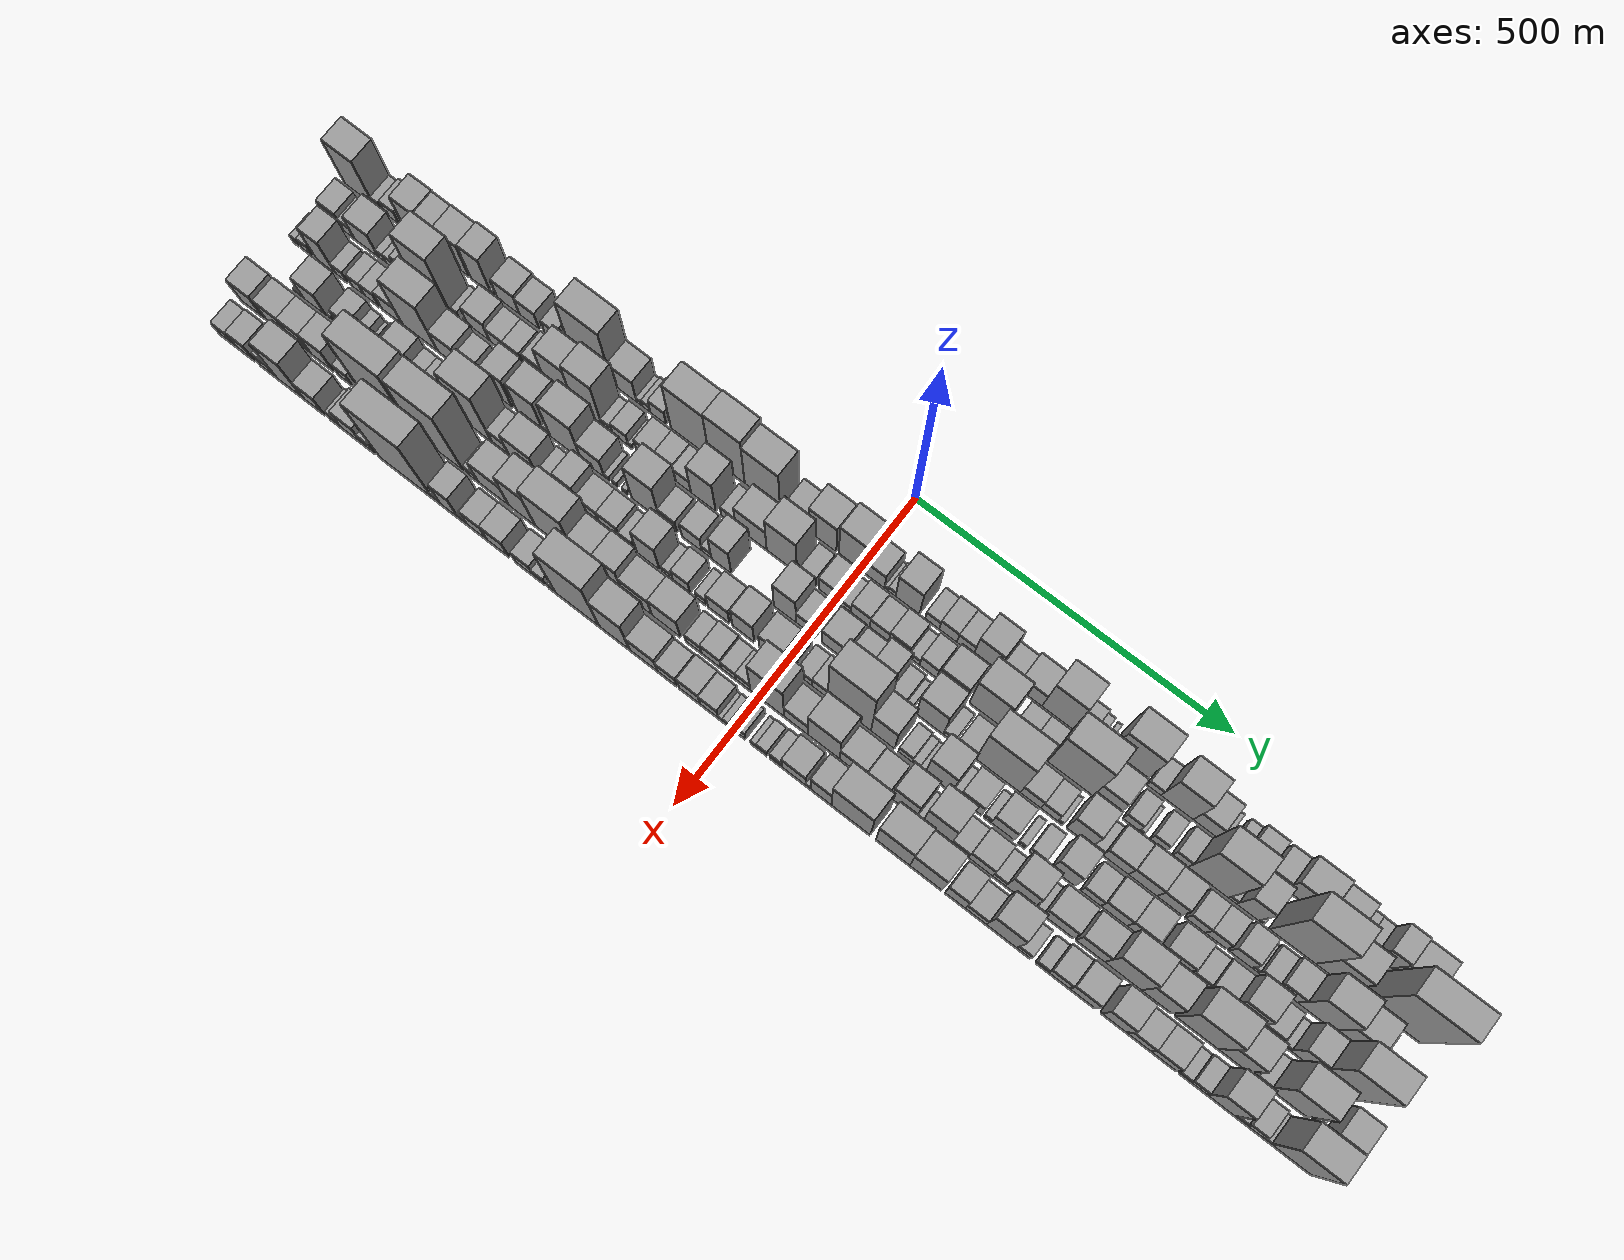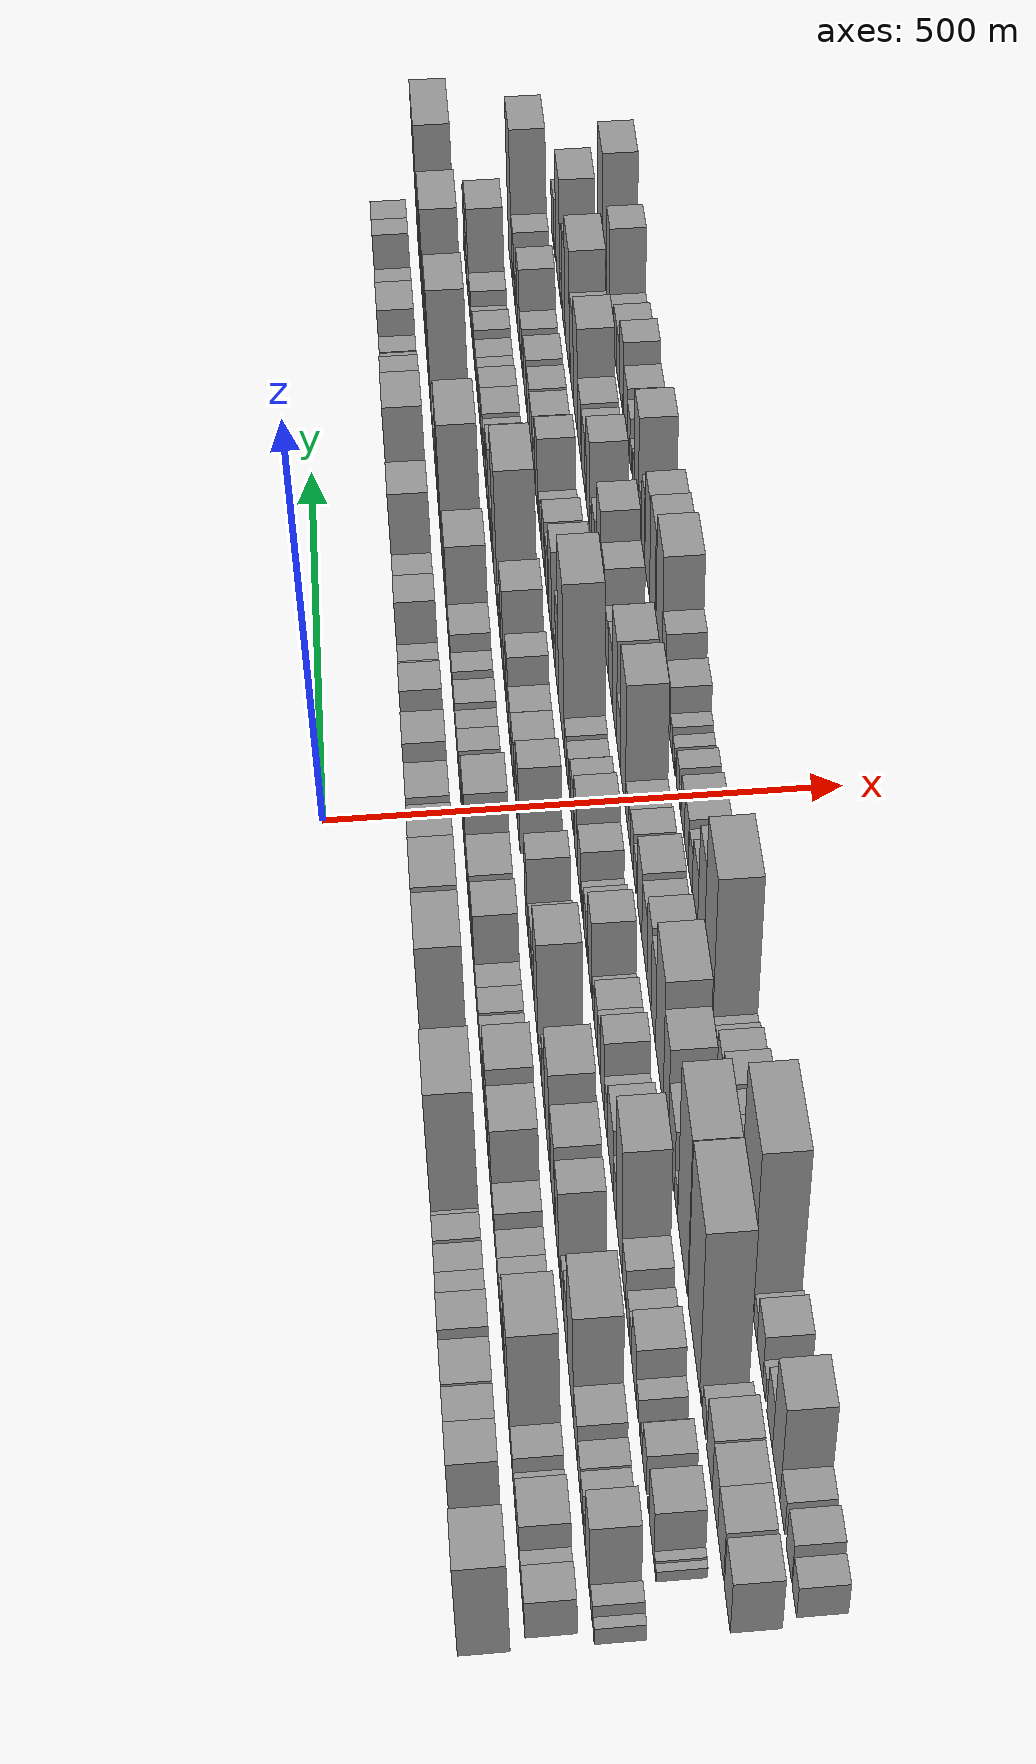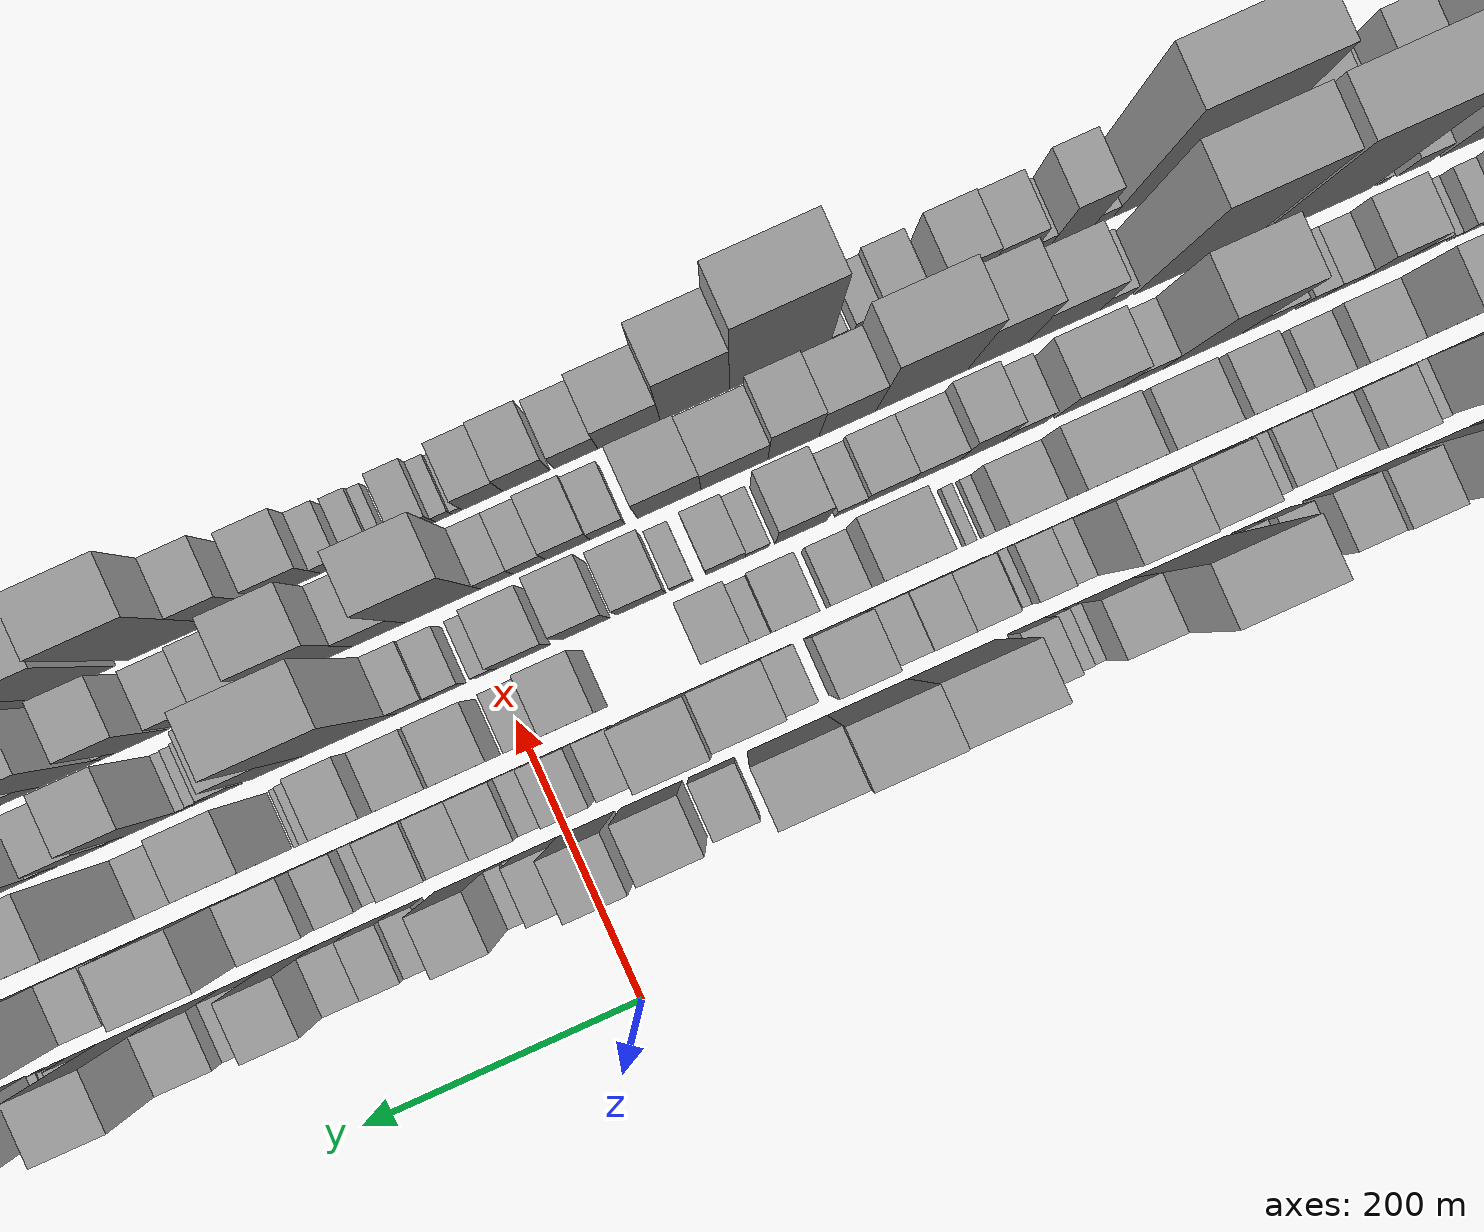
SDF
<sdf version="1.6">
 <world name="default">
  <scene>
   <sky><clouds><speed>12</speed></clouds></sky>
   <ambient>0.4 0.4 0.4 1</ambient>
   <background>0.7 0.7 0.7 1</background>
   <shadows>1</shadows>
  </scene>
  <gravity>0 0 -9.8066</gravity>
  <magnetic_field>6e-06 2.3e-05 -4.2e-05</magnetic_field>
  <physics default="0" name="default_physics" type="ode">
   <ode>
    <solver>
     <type>quick</type>
     <iters>10</iters>
     <sor>1.0</sor>
     <use_dynamic_moi_rescaling>0</use_dynamic_moi_rescaling>
    </solver>
    <constraints>
     <cfm>0</cfm>
     <erp>0.2</erp>
     <contact_max_correcting_vel>100</contact_max_correcting_vel>
     <contact_surface_layer>0.001</contact_surface_layer>
    </constraints>
   </ode>
   <max_step_size>0.004</max_step_size>
   <real_time_factor>1</real_time_factor>
   <real_time_update_rate>250</real_time_update_rate>
  </physics>
  <light name="sun" type="directional">
   <pose>0 0 10 0 0 0</pose>
   <diffuse>0.8 0.8 0.8 1</diffuse>
   <specular>0.2 0.2 0.2 1</specular>
   <attenuation>
    <range>1000</range>
    <constant>0.9</constant>
    <linear>0.01</linear>
    <quadratic>0.001</quadratic>
   </attenuation>
   <direction>-0.5 0.1 -0.9</direction>
  </light>
  <model name="building_1">
   <static>1</static>
   <pose>100.0000 -834.8855 0 0.000000 0.000000 0.000000</pose>
   <link name="link">
    <pose>0 0 66.00 0 0 0</pose>
    <collision name="collision"><geometry><box><size>40.0000 50.2289 132.0000</size></box></geometry></collision>
    <visual name="visual">
     <cast_shadows>0</cast_shadows>
     <geometry><box><size>40.0000 50.2289 132.0000</size></box></geometry>
     <material>
      <script>
       <uri>model://grey_wall/materials/scripts</uri>
       <uri>model://grey_wall/materials/textures</uri>
       <name>vrc/grey_wall</name>
      </script>
     </material>
    </visual>
   </link>
  </model>
  <model name="building_2">
   <static>1</static>
   <pose>100.0000 -803.1771 0 0.000000 0.000000 0.000000</pose>
   <link name="link">
    <pose>0 0 13.50 0 0 0</pose>
    <collision name="collision"><geometry><box><size>40.0000 13.1880 27.0000</size></box></geometry></collision>
    <visual name="visual">
     <cast_shadows>0</cast_shadows>
     <geometry><box><size>40.0000 13.1880 27.0000</size></box></geometry>
     <material>
      <script>
       <uri>model://grey_wall/materials/scripts</uri>
       <uri>model://grey_wall/materials/textures</uri>
       <name>vrc/grey_wall</name>
      </script>
     </material>
    </visual>
   </link>
  </model>
  <model name="building_3">
   <static>1</static>
   <pose>100.0000 -778.1001 0 0.000000 0.000000 0.000000</pose>
   <link name="link">
    <pose>0 0 21.00 0 0 0</pose>
    <collision name="collision"><geometry><box><size>40.0000 24.9659 42.0000</size></box></geometry></collision>
    <visual name="visual">
     <cast_shadows>0</cast_shadows>
     <geometry><box><size>40.0000 24.9659 42.0000</size></box></geometry>
     <material>
      <script>
       <uri>model://grey_wall/materials/scripts</uri>
       <uri>model://grey_wall/materials/textures</uri>
       <name>vrc/grey_wall</name>
      </script>
     </material>
    </visual>
   </link>
  </model>
  <model name="building_4">
   <static>1</static>
   <pose>100.0000 -737.8932 0 0.000000 0.000000 0.000000</pose>
   <link name="link">
    <pose>0 0 51.00 0 0 0</pose>
    <collision name="collision"><geometry><box><size>40.0000 37.4479 102.0000</size></box></geometry></collision>
    <visual name="visual">
     <cast_shadows>0</cast_shadows>
     <geometry><box><size>40.0000 37.4479 102.0000</size></box></geometry>
     <material>
      <script>
       <uri>model://grey_wall/materials/scripts</uri>
       <uri>model://grey_wall/materials/textures</uri>
       <name>vrc/grey_wall</name>
      </script>
     </material>
    </visual>
   </link>
  </model>
  <model name="building_5">
   <static>1</static>
   <pose>100.0000 -702.8747 0 0.000000 0.000000 0.000000</pose>
   <link name="link">
    <pose>0 0 49.50 0 0 0</pose>
    <collision name="collision"><geometry><box><size>40.0000 32.5892 99.0000</size></box></geometry></collision>
    <visual name="visual">
     <cast_shadows>0</cast_shadows>
     <geometry><box><size>40.0000 32.5892 99.0000</size></box></geometry>
     <material>
      <script>
       <uri>model://grey_wall/materials/scripts</uri>
       <uri>model://grey_wall/materials/textures</uri>
       <name>vrc/grey_wall</name>
      </script>
     </material>
    </visual>
   </link>
  </model>
  <model name="building_6">
   <static>1</static>
   <pose>100.0000 -666.4119 0 0.000000 0.000000 0.000000</pose>
   <link name="link">
    <pose>0 0 51.00 0 0 0</pose>
    <collision name="collision"><geometry><box><size>40.0000 40.3364 102.0000</size></box></geometry></collision>
    <visual name="visual">
     <cast_shadows>0</cast_shadows>
     <geometry><box><size>40.0000 40.3364 102.0000</size></box></geometry>
     <material>
      <script>
       <uri>model://grey_wall/materials/scripts</uri>
       <uri>model://grey_wall/materials/textures</uri>
       <name>vrc/grey_wall</name>
      </script>
     </material>
    </visual>
   </link>
  </model>
  <model name="building_7">
   <static>1</static>
   <pose>100.0000 -625.9581 0 0.000000 0.000000 0.000000</pose>
   <link name="link">
    <pose>0 0 55.50 0 0 0</pose>
    <collision name="collision"><geometry><box><size>40.0000 34.5713 111.0000</size></box></geometry></collision>
    <visual name="visual">
     <cast_shadows>0</cast_shadows>
     <geometry><box><size>40.0000 34.5713 111.0000</size></box></geometry>
     <material>
      <script>
       <uri>model://grey_wall/materials/scripts</uri>
       <uri>model://grey_wall/materials/textures</uri>
       <name>vrc/grey_wall</name>
      </script>
     </material>
    </visual>
   </link>
  </model>
  <model name="building_8">
   <static>1</static>
   <pose>100.0000 -605.1786 0 0.000000 0.000000 0.000000</pose>
   <link name="link">
    <pose>0 0 7.50 0 0 0</pose>
    <collision name="collision"><geometry><box><size>40.0000 6.9877 15.0000</size></box></geometry></collision>
    <visual name="visual">
     <cast_shadows>0</cast_shadows>
     <geometry><box><size>40.0000 6.9877 15.0000</size></box></geometry>
     <material>
      <script>
       <uri>model://grey_wall/materials/scripts</uri>
       <uri>model://grey_wall/materials/textures</uri>
       <name>vrc/grey_wall</name>
      </script>
     </material>
    </visual>
   </link>
  </model>
  <model name="building_9">
   <static>1</static>
   <pose>100.0000 -578.8045 0 0.000000 0.000000 0.000000</pose>
   <link name="link">
    <pose>0 0 33.00 0 0 0</pose>
    <collision name="collision"><geometry><box><size>40.0000 37.7605 66.0000</size></box></geometry></collision>
    <visual name="visual">
     <cast_shadows>0</cast_shadows>
     <geometry><box><size>40.0000 37.7605 66.0000</size></box></geometry>
     <material>
      <script>
       <uri>model://grey_wall/materials/scripts</uri>
       <uri>model://grey_wall/materials/textures</uri>
       <name>vrc/grey_wall</name>
      </script>
     </material>
    </visual>
   </link>
  </model>
  <model name="building_10">
   <static>1</static>
   <pose>100.0000 -543.2496 0 0.000000 0.000000 0.000000</pose>
   <link name="link">
    <pose>0 0 28.50 0 0 0</pose>
    <collision name="collision"><geometry><box><size>40.0000 33.3492 57.0000</size></box></geometry></collision>
    <visual name="visual">
     <cast_shadows>0</cast_shadows>
     <geometry><box><size>40.0000 33.3492 57.0000</size></box></geometry>
     <material>
      <script>
       <uri>model://grey_wall/materials/scripts</uri>
       <uri>model://grey_wall/materials/textures</uri>
       <name>vrc/grey_wall</name>
      </script>
     </material>
    </visual>
   </link>
  </model>
  <model name="building_11">
   <static>1</static>
   <pose>100.0000 -504.7542 0 0.000000 0.000000 0.000000</pose>
   <link name="link">
    <pose>0 0 24.00 0 0 0</pose>
    <collision name="collision"><geometry><box><size>40.0000 25.6417 48.0000</size></box></geometry></collision>
    <visual name="visual">
     <cast_shadows>0</cast_shadows>
     <geometry><box><size>40.0000 25.6417 48.0000</size></box></geometry>
     <material>
      <script>
       <uri>model://grey_wall/materials/scripts</uri>
       <uri>model://grey_wall/materials/textures</uri>
       <name>vrc/grey_wall</name>
      </script>
     </material>
    </visual>
   </link>
  </model>
  <model name="building_12">
   <static>1</static>
   <pose>100.0000 -483.8024 0 0.000000 0.000000 0.000000</pose>
   <link name="link">
    <pose>0 0 15.00 0 0 0</pose>
    <collision name="collision"><geometry><box><size>40.0000 16.2619 30.0000</size></box></geometry></collision>
    <visual name="visual">
     <cast_shadows>0</cast_shadows>
     <geometry><box><size>40.0000 16.2619 30.0000</size></box></geometry>
     <material>
      <script>
       <uri>model://grey_wall/materials/scripts</uri>
       <uri>model://grey_wall/materials/textures</uri>
       <name>vrc/grey_wall</name>
      </script>
     </material>
    </visual>
   </link>
  </model>
  <model name="building_13">
   <static>1</static>
   <pose>100.0000 -437.9912 0 0.000000 0.000000 0.000000</pose>
   <link name="link">
    <pose>0 0 93.00 0 0 0</pose>
    <collision name="collision"><geometry><box><size>40.0000 67.3604 186.0000</size></box></geometry></collision>
    <visual name="visual">
     <cast_shadows>0</cast_shadows>
     <geometry><box><size>40.0000 67.3604 186.0000</size></box></geometry>
     <material>
      <script>
       <uri>model://grey_wall/materials/scripts</uri>
       <uri>model://grey_wall/materials/textures</uri>
       <name>vrc/grey_wall</name>
      </script>
     </material>
    </visual>
   </link>
  </model>
  <model name="building_14">
   <static>1</static>
   <pose>100.0000 -383.9383 0 0.000000 0.000000 0.000000</pose>
   <link name="link">
    <pose>0 0 40.50 0 0 0</pose>
    <collision name="collision"><geometry><box><size>40.0000 40.7455 81.0000</size></box></geometry></collision>
    <visual name="visual">
     <cast_shadows>0</cast_shadows>
     <geometry><box><size>40.0000 40.7455 81.0000</size></box></geometry>
     <material>
      <script>
       <uri>model://grey_wall/materials/scripts</uri>
       <uri>model://grey_wall/materials/textures</uri>
       <name>vrc/grey_wall</name>
      </script>
     </material>
    </visual>
   </link>
  </model>
  <model name="building_15">
   <static>1</static>
   <pose>100.0000 -359.0882 0 0.000000 0.000000 0.000000</pose>
   <link name="link">
    <pose>0 0 10.50 0 0 0</pose>
    <collision name="collision"><geometry><box><size>40.0000 8.9547 21.0000</size></box></geometry></collision>
    <visual name="visual">
     <cast_shadows>0</cast_shadows>
     <geometry><box><size>40.0000 8.9547 21.0000</size></box></geometry>
     <material>
      <script>
       <uri>model://grey_wall/materials/scripts</uri>
       <uri>model://grey_wall/materials/textures</uri>
       <name>vrc/grey_wall</name>
      </script>
     </material>
    </visual>
   </link>
  </model>
  <model name="building_16">
   <static>1</static>
   <pose>100.0000 -347.9963 0 0.000000 0.000000 0.000000</pose>
   <link name="link">
    <pose>0 0 13.50 0 0 0</pose>
    <collision name="collision"><geometry><box><size>40.0000 13.2291 27.0000</size></box></geometry></collision>
    <visual name="visual">
     <cast_shadows>0</cast_shadows>
     <geometry><box><size>40.0000 13.2291 27.0000</size></box></geometry>
     <material>
      <script>
       <uri>model://grey_wall/materials/scripts</uri>
       <uri>model://grey_wall/materials/textures</uri>
       <name>vrc/grey_wall</name>
      </script>
     </material>
    </visual>
   </link>
  </model>
  <model name="building_17">
   <static>1</static>
   <pose>100.0000 -328.2800 0 0.000000 0.000000 0.000000</pose>
   <link name="link">
    <pose>0 0 25.50 0 0 0</pose>
    <collision name="collision"><geometry><box><size>40.0000 26.2035 51.0000</size></box></geometry></collision>
    <visual name="visual">
     <cast_shadows>0</cast_shadows>
     <geometry><box><size>40.0000 26.2035 51.0000</size></box></geometry>
     <material>
      <script>
       <uri>model://grey_wall/materials/scripts</uri>
       <uri>model://grey_wall/materials/textures</uri>
       <name>vrc/grey_wall</name>
      </script>
     </material>
    </visual>
   </link>
  </model>
  <model name="building_18">
   <static>1</static>
   <pose>100.0000 -275.7349 0 0.000000 0.000000 0.000000</pose>
   <link name="link">
    <pose>0 0 85.50 0 0 0</pose>
    <collision name="collision"><geometry><box><size>40.0000 62.8868 171.0000</size></box></geometry></collision>
    <visual name="visual">
     <cast_shadows>0</cast_shadows>
     <geometry><box><size>40.0000 62.8868 171.0000</size></box></geometry>
     <material>
      <script>
       <uri>model://grey_wall/materials/scripts</uri>
       <uri>model://grey_wall/materials/textures</uri>
       <name>vrc/grey_wall</name>
      </script>
     </material>
    </visual>
   </link>
  </model>
  <model name="building_19">
   <static>1</static>
   <pose>100.0000 -215.3194 0 0.000000 0.000000 0.000000</pose>
   <link name="link">
    <pose>0 0 88.50 0 0 0</pose>
    <collision name="collision"><geometry><box><size>40.0000 57.9442 177.0000</size></box></geometry></collision>
    <visual name="visual">
     <cast_shadows>0</cast_shadows>
     <geometry><box><size>40.0000 57.9442 177.0000</size></box></geometry>
     <material>
      <script>
       <uri>model://grey_wall/materials/scripts</uri>
       <uri>model://grey_wall/materials/textures</uri>
       <name>vrc/grey_wall</name>
      </script>
     </material>
    </visual>
   </link>
  </model>
  <model name="building_20">
   <static>1</static>
   <pose>100.0000 -157.6240 0 0.000000 0.000000 0.000000</pose>
   <link name="link">
    <pose>0 0 78.00 0 0 0</pose>
    <collision name="collision"><geometry><box><size>40.0000 57.4465 156.0000</size></box></geometry></collision>
    <visual name="visual">
     <cast_shadows>0</cast_shadows>
     <geometry><box><size>40.0000 57.4465 156.0000</size></box></geometry>
     <material>
      <script>
       <uri>model://grey_wall/materials/scripts</uri>
       <uri>model://grey_wall/materials/textures</uri>
       <name>vrc/grey_wall</name>
      </script>
     </material>
    </visual>
   </link>
  </model>
  <model name="building_21">
   <static>1</static>
   <pose>100.0000 -103.6680 0 0.000000 0.000000 0.000000</pose>
   <link name="link">
    <pose>0 0 28.50 0 0 0</pose>
    <collision name="collision"><geometry><box><size>40.0000 32.4657 57.0000</size></box></geometry></collision>
    <visual name="visual">
     <cast_shadows>0</cast_shadows>
     <geometry><box><size>40.0000 32.4657 57.0000</size></box></geometry>
     <material>
      <script>
       <uri>model://grey_wall/materials/scripts</uri>
       <uri>model://grey_wall/materials/textures</uri>
       <name>vrc/grey_wall</name>
      </script>
     </material>
    </visual>
   </link>
  </model>
  <model name="building_22">
   <static>1</static>
   <pose>100.0000 -60.3665 0 0.000000 0.000000 0.000000</pose>
   <link name="link">
    <pose>0 0 57.00 0 0 0</pose>
    <collision name="collision"><geometry><box><size>40.0000 44.1373 114.0000</size></box></geometry></collision>
    <visual name="visual">
     <cast_shadows>0</cast_shadows>
     <geometry><box><size>40.0000 44.1373 114.0000</size></box></geometry>
     <material>
      <script>
       <uri>model://grey_wall/materials/scripts</uri>
       <uri>model://grey_wall/materials/textures</uri>
       <name>vrc/grey_wall</name>
      </script>
     </material>
    </visual>
   </link>
  </model>
  <model name="building_23">
   <static>1</static>
   <pose>100.0000 -13.8232 0 0.000000 0.000000 0.000000</pose>
   <link name="link">
    <pose>0 0 67.50 0 0 0</pose>
    <collision name="collision"><geometry><box><size>40.0000 40.9494 135.0000</size></box></geometry></collision>
    <visual name="visual">
     <cast_shadows>0</cast_shadows>
     <geometry><box><size>40.0000 40.9494 135.0000</size></box></geometry>
     <material>
      <script>
       <uri>model://grey_wall/materials/scripts</uri>
       <uri>model://grey_wall/materials/textures</uri>
       <name>vrc/grey_wall</name>
      </script>
     </material>
    </visual>
   </link>
  </model>
  <model name="building_24">
   <static>1</static>
   <pose>100.0000 22.8650 0 0.000000 0.000000 0.000000</pose>
   <link name="link">
    <pose>0 0 31.50 0 0 0</pose>
    <collision name="collision"><geometry><box><size>40.0000 32.4269 63.0000</size></box></geometry></collision>
    <visual name="visual">
     <cast_shadows>0</cast_shadows>
     <geometry><box><size>40.0000 32.4269 63.0000</size></box></geometry>
     <material>
      <script>
       <uri>model://grey_wall/materials/scripts</uri>
       <uri>model://grey_wall/materials/textures</uri>
       <name>vrc/grey_wall</name>
      </script>
     </material>
    </visual>
   </link>
  </model>
  <model name="building_25">
   <static>1</static>
   <pose>100.0000 42.1342 0 0.000000 0.000000 0.000000</pose>
   <link name="link">
    <pose>0 0 7.50 0 0 0</pose>
    <collision name="collision"><geometry><box><size>40.0000 6.1115 15.0000</size></box></geometry></collision>
    <visual name="visual">
     <cast_shadows>0</cast_shadows>
     <geometry><box><size>40.0000 6.1115 15.0000</size></box></geometry>
     <material>
      <script>
       <uri>model://grey_wall/materials/scripts</uri>
       <uri>model://grey_wall/materials/textures</uri>
       <name>vrc/grey_wall</name>
      </script>
     </material>
    </visual>
   </link>
  </model>
  <model name="building_26">
   <static>1</static>
   <pose>100.0000 51.0352 0 0.000000 0.000000 0.000000</pose>
   <link name="link">
    <pose>0 0 12.00 0 0 0</pose>
    <collision name="collision"><geometry><box><size>40.0000 11.6906 24.0000</size></box></geometry></collision>
    <visual name="visual">
     <cast_shadows>0</cast_shadows>
     <geometry><box><size>40.0000 11.6906 24.0000</size></box></geometry>
     <material>
      <script>
       <uri>model://grey_wall/materials/scripts</uri>
       <uri>model://grey_wall/materials/textures</uri>
       <name>vrc/grey_wall</name>
      </script>
     </material>
    </visual>
   </link>
  </model>
  <model name="building_27">
   <static>1</static>
   <pose>100.0000 75.7441 0 0.000000 0.000000 0.000000</pose>
   <link name="link">
    <pose>0 0 55.50 0 0 0</pose>
    <collision name="collision"><geometry><box><size>40.0000 37.7272 111.0000</size></box></geometry></collision>
    <visual name="visual">
     <cast_shadows>0</cast_shadows>
     <geometry><box><size>40.0000 37.7272 111.0000</size></box></geometry>
     <material>
      <script>
       <uri>model://grey_wall/materials/scripts</uri>
       <uri>model://grey_wall/materials/textures</uri>
       <name>vrc/grey_wall</name>
      </script>
     </material>
    </visual>
   </link>
  </model>
  <model name="building_28">
   <static>1</static>
   <pose>100.0000 114.8784 0 0.000000 0.000000 0.000000</pose>
   <link name="link">
    <pose>0 0 21.00 0 0 0</pose>
    <collision name="collision"><geometry><box><size>40.0000 22.5414 42.0000</size></box></geometry></collision>
    <visual name="visual">
     <cast_shadows>0</cast_shadows>
     <geometry><box><size>40.0000 22.5414 42.0000</size></box></geometry>
     <material>
      <script>
       <uri>model://grey_wall/materials/scripts</uri>
       <uri>model://grey_wall/materials/textures</uri>
       <name>vrc/grey_wall</name>
      </script>
     </material>
    </visual>
   </link>
  </model>
  <model name="building_29">
   <static>1</static>
   <pose>100.0000 139.9998 0 0.000000 0.000000 0.000000</pose>
   <link name="link">
    <pose>0 0 27.00 0 0 0</pose>
    <collision name="collision"><geometry><box><size>40.0000 27.7014 54.0000</size></box></geometry></collision>
    <visual name="visual">
     <cast_shadows>0</cast_shadows>
     <geometry><box><size>40.0000 27.7014 54.0000</size></box></geometry>
     <material>
      <script>
       <uri>model://grey_wall/materials/scripts</uri>
       <uri>model://grey_wall/materials/textures</uri>
       <name>vrc/grey_wall</name>
      </script>
     </material>
    </visual>
   </link>
  </model>
  <model name="building_30">
   <static>1</static>
   <pose>100.0000 166.9720 0 0.000000 0.000000 0.000000</pose>
   <link name="link">
    <pose>0 0 25.50 0 0 0</pose>
    <collision name="collision"><geometry><box><size>40.0000 26.2428 51.0000</size></box></geometry></collision>
    <visual name="visual">
     <cast_shadows>0</cast_shadows>
     <geometry><box><size>40.0000 26.2428 51.0000</size></box></geometry>
     <material>
      <script>
       <uri>model://grey_wall/materials/scripts</uri>
       <uri>model://grey_wall/materials/textures</uri>
       <name>vrc/grey_wall</name>
      </script>
     </material>
    </visual>
   </link>
  </model>
  <model name="building_31">
   <static>1</static>
   <pose>100.0000 199.5539 0 0.000000 0.000000 0.000000</pose>
   <link name="link">
    <pose>0 0 54.00 0 0 0</pose>
    <collision name="collision"><geometry><box><size>40.0000 38.9211 108.0000</size></box></geometry></collision>
    <visual name="visual">
     <cast_shadows>0</cast_shadows>
     <geometry><box><size>40.0000 38.9211 108.0000</size></box></geometry>
     <material>
      <script>
       <uri>model://grey_wall/materials/scripts</uri>
       <uri>model://grey_wall/materials/textures</uri>
       <name>vrc/grey_wall</name>
      </script>
     </material>
    </visual>
   </link>
  </model>
  <model name="building_32">
   <static>1</static>
   <pose>100.0000 233.7034 0 0.000000 0.000000 0.000000</pose>
   <link name="link">
    <pose>0 0 25.50 0 0 0</pose>
    <collision name="collision"><geometry><box><size>40.0000 29.3780 51.0000</size></box></geometry></collision>
    <visual name="visual">
     <cast_shadows>0</cast_shadows>
     <geometry><box><size>40.0000 29.3780 51.0000</size></box></geometry>
     <material>
      <script>
       <uri>model://grey_wall/materials/scripts</uri>
       <uri>model://grey_wall/materials/textures</uri>
       <name>vrc/grey_wall</name>
      </script>
     </material>
    </visual>
   </link>
  </model>
  <model name="building_33">
   <static>1</static>
   <pose>100.0000 267.7896 0 0.000000 0.000000 0.000000</pose>
   <link name="link">
    <pose>0 0 36.00 0 0 0</pose>
    <collision name="collision"><geometry><box><size>40.0000 38.7943 72.0000</size></box></geometry></collision>
    <visual name="visual">
     <cast_shadows>0</cast_shadows>
     <geometry><box><size>40.0000 38.7943 72.0000</size></box></geometry>
     <material>
      <script>
       <uri>model://grey_wall/materials/scripts</uri>
       <uri>model://grey_wall/materials/textures</uri>
       <name>vrc/grey_wall</name>
      </script>
     </material>
    </visual>
   </link>
  </model>
  <model name="building_34">
   <static>1</static>
   <pose>100.0000 311.4002 0 0.000000 0.000000 0.000000</pose>
   <link name="link">
    <pose>0 0 76.50 0 0 0</pose>
    <collision name="collision"><geometry><box><size>40.0000 48.4269 153.0000</size></box></geometry></collision>
    <visual name="visual">
     <cast_shadows>0</cast_shadows>
     <geometry><box><size>40.0000 48.4269 153.0000</size></box></geometry>
     <material>
      <script>
       <uri>model://grey_wall/materials/scripts</uri>
       <uri>model://grey_wall/materials/textures</uri>
       <name>vrc/grey_wall</name>
      </script>
     </material>
    </visual>
   </link>
  </model>
  <model name="building_35">
   <static>1</static>
   <pose>100.0000 346.5541 0 0.000000 0.000000 0.000000</pose>
   <link name="link">
    <pose>0 0 21.00 0 0 0</pose>
    <collision name="collision"><geometry><box><size>40.0000 21.8810 42.0000</size></box></geometry></collision>
    <visual name="visual">
     <cast_shadows>0</cast_shadows>
     <geometry><box><size>40.0000 21.8810 42.0000</size></box></geometry>
     <material>
      <script>
       <uri>model://grey_wall/materials/scripts</uri>
       <uri>model://grey_wall/materials/textures</uri>
       <name>vrc/grey_wall</name>
      </script>
     </material>
    </visual>
   </link>
  </model>
  <model name="building_36">
   <static>1</static>
   <pose>100.0000 363.3798 0 0.000000 0.000000 0.000000</pose>
   <link name="link">
    <pose>0 0 12.00 0 0 0</pose>
    <collision name="collision"><geometry><box><size>40.0000 11.7702 24.0000</size></box></geometry></collision>
    <visual name="visual">
     <cast_shadows>0</cast_shadows>
     <geometry><box><size>40.0000 11.7702 24.0000</size></box></geometry>
     <material>
      <script>
       <uri>model://grey_wall/materials/scripts</uri>
       <uri>model://grey_wall/materials/textures</uri>
       <name>vrc/grey_wall</name>
      </script>
     </material>
    </visual>
   </link>
  </model>
  <model name="building_37">
   <static>1</static>
   <pose>100.0000 377.5554 0 0.000000 0.000000 0.000000</pose>
   <link name="link">
    <pose>0 0 7.50 0 0 0</pose>
    <collision name="collision"><geometry><box><size>40.0000 6.5810 15.0000</size></box></geometry></collision>
    <visual name="visual">
     <cast_shadows>0</cast_shadows>
     <geometry><box><size>40.0000 6.5810 15.0000</size></box></geometry>
     <material>
      <script>
       <uri>model://grey_wall/materials/scripts</uri>
       <uri>model://grey_wall/materials/textures</uri>
       <name>vrc/grey_wall</name>
      </script>
     </material>
    </visual>
   </link>
  </model>
  <model name="building_38">
   <static>1</static>
   <pose>100.0000 414.7971 0 0.000000 0.000000 0.000000</pose>
   <link name="link">
    <pose>0 0 90.00 0 0 0</pose>
    <collision name="collision"><geometry><box><size>40.0000 55.9024 180.0000</size></box></geometry></collision>
    <visual name="visual">
     <cast_shadows>0</cast_shadows>
     <geometry><box><size>40.0000 55.9024 180.0000</size></box></geometry>
     <material>
      <script>
       <uri>model://grey_wall/materials/scripts</uri>
       <uri>model://grey_wall/materials/textures</uri>
       <name>vrc/grey_wall</name>
      </script>
     </material>
    </visual>
   </link>
  </model>
  <model name="building_39">
   <static>1</static>
   <pose>100.0000 459.5470 0 0.000000 0.000000 0.000000</pose>
   <link name="link">
    <pose>0 0 18.00 0 0 0</pose>
    <collision name="collision"><geometry><box><size>40.0000 21.5973 36.0000</size></box></geometry></collision>
    <visual name="visual">
     <cast_shadows>0</cast_shadows>
     <geometry><box><size>40.0000 21.5973 36.0000</size></box></geometry>
     <material>
      <script>
       <uri>model://grey_wall/materials/scripts</uri>
       <uri>model://grey_wall/materials/textures</uri>
       <name>vrc/grey_wall</name>
      </script>
     </material>
    </visual>
   </link>
  </model>
  <model name="building_40">
   <static>1</static>
   <pose>100.0000 494.8521 0 0.000000 0.000000 0.000000</pose>
   <link name="link">
    <pose>0 0 69.00 0 0 0</pose>
    <collision name="collision"><geometry><box><size>40.0000 49.0130 138.0000</size></box></geometry></collision>
    <visual name="visual">
     <cast_shadows>0</cast_shadows>
     <geometry><box><size>40.0000 49.0130 138.0000</size></box></geometry>
     <material>
      <script>
       <uri>model://grey_wall/materials/scripts</uri>
       <uri>model://grey_wall/materials/textures</uri>
       <name>vrc/grey_wall</name>
      </script>
     </material>
    </visual>
   </link>
  </model>
  <model name="building_41">
   <static>1</static>
   <pose>100.0000 536.8398 0 0.000000 0.000000 0.000000</pose>
   <link name="link">
    <pose>0 0 34.50 0 0 0</pose>
    <collision name="collision"><geometry><box><size>40.0000 34.9624 69.0000</size></box></geometry></collision>
    <visual name="visual">
     <cast_shadows>0</cast_shadows>
     <geometry><box><size>40.0000 34.9624 69.0000</size></box></geometry>
     <material>
      <script>
       <uri>model://grey_wall/materials/scripts</uri>
       <uri>model://grey_wall/materials/textures</uri>
       <name>vrc/grey_wall</name>
      </script>
     </material>
    </visual>
   </link>
  </model>
  <model name="building_42">
   <static>1</static>
   <pose>100.0000 559.6195 0 0.000000 0.000000 0.000000</pose>
   <link name="link">
    <pose>0 0 12.00 0 0 0</pose>
    <collision name="collision"><geometry><box><size>40.0000 10.5969 24.0000</size></box></geometry></collision>
    <visual name="visual">
     <cast_shadows>0</cast_shadows>
     <geometry><box><size>40.0000 10.5969 24.0000</size></box></geometry>
     <material>
      <script>
       <uri>model://grey_wall/materials/scripts</uri>
       <uri>model://grey_wall/materials/textures</uri>
       <name>vrc/grey_wall</name>
      </script>
     </material>
    </visual>
   </link>
  </model>
  <model name="building_43">
   <static>1</static>
   <pose>100.0000 582.6176 0 0.000000 0.000000 0.000000</pose>
   <link name="link">
    <pose>0 0 15.00 0 0 0</pose>
    <collision name="collision"><geometry><box><size>40.0000 17.3994 30.0000</size></box></geometry></collision>
    <visual name="visual">
     <cast_shadows>0</cast_shadows>
     <geometry><box><size>40.0000 17.3994 30.0000</size></box></geometry>
     <material>
      <script>
       <uri>model://grey_wall/materials/scripts</uri>
       <uri>model://grey_wall/materials/textures</uri>
       <name>vrc/grey_wall</name>
      </script>
     </material>
    </visual>
   </link>
  </model>
  <model name="building_44">
   <static>1</static>
   <pose>100.0000 607.7727 0 0.000000 0.000000 0.000000</pose>
   <link name="link">
    <pose>0 0 28.50 0 0 0</pose>
    <collision name="collision"><geometry><box><size>40.0000 32.9106 57.0000</size></box></geometry></collision>
    <visual name="visual">
     <cast_shadows>0</cast_shadows>
     <geometry><box><size>40.0000 32.9106 57.0000</size></box></geometry>
     <material>
      <script>
       <uri>model://grey_wall/materials/scripts</uri>
       <uri>model://grey_wall/materials/textures</uri>
       <name>vrc/grey_wall</name>
      </script>
     </material>
    </visual>
   </link>
  </model>
  <model name="building_45">
   <static>1</static>
   <pose>100.0000 642.7919 0 0.000000 0.000000 0.000000</pose>
   <link name="link">
    <pose>0 0 27.00 0 0 0</pose>
    <collision name="collision"><geometry><box><size>40.0000 27.1279 54.0000</size></box></geometry></collision>
    <visual name="visual">
     <cast_shadows>0</cast_shadows>
     <geometry><box><size>40.0000 27.1279 54.0000</size></box></geometry>
     <material>
      <script>
       <uri>model://grey_wall/materials/scripts</uri>
       <uri>model://grey_wall/materials/textures</uri>
       <name>vrc/grey_wall</name>
      </script>
     </material>
    </visual>
   </link>
  </model>
  <model name="building_46">
   <static>1</static>
   <pose>100.0000 681.2926 0 0.000000 0.000000 0.000000</pose>
   <link name="link">
    <pose>0 0 45.00 0 0 0</pose>
    <collision name="collision"><geometry><box><size>40.0000 49.8735 90.0000</size></box></geometry></collision>
    <visual name="visual">
     <cast_shadows>0</cast_shadows>
     <geometry><box><size>40.0000 49.8735 90.0000</size></box></geometry>
     <material>
      <script>
       <uri>model://grey_wall/materials/scripts</uri>
       <uri>model://grey_wall/materials/textures</uri>
       <name>vrc/grey_wall</name>
      </script>
     </material>
    </visual>
   </link>
  </model>
  <model name="building_47">
   <static>1</static>
   <pose>100.0000 728.8882 0 0.000000 0.000000 0.000000</pose>
   <link name="link">
    <pose>0 0 37.50 0 0 0</pose>
    <collision name="collision"><geometry><box><size>40.0000 39.3178 75.0000</size></box></geometry></collision>
    <visual name="visual">
     <cast_shadows>0</cast_shadows>
     <geometry><box><size>40.0000 39.3178 75.0000</size></box></geometry>
     <material>
      <script>
       <uri>model://grey_wall/materials/scripts</uri>
       <uri>model://grey_wall/materials/textures</uri>
       <name>vrc/grey_wall</name>
      </script>
     </material>
    </visual>
   </link>
  </model>
  <model name="building_48">
   <static>1</static>
   <pose>100.0000 758.3306 0 0.000000 0.000000 0.000000</pose>
   <link name="link">
    <pose>0 0 18.00 0 0 0</pose>
    <collision name="collision"><geometry><box><size>40.0000 19.5669 36.0000</size></box></geometry></collision>
    <visual name="visual">
     <cast_shadows>0</cast_shadows>
     <geometry><box><size>40.0000 19.5669 36.0000</size></box></geometry>
     <material>
      <script>
       <uri>model://grey_wall/materials/scripts</uri>
       <uri>model://grey_wall/materials/textures</uri>
       <name>vrc/grey_wall</name>
      </script>
     </material>
    </visual>
   </link>
  </model>
  <model name="building_49">
   <static>1</static>
   <pose>100.0000 777.3705 0 0.000000 0.000000 0.000000</pose>
   <link name="link">
    <pose>0 0 16.50 0 0 0</pose>
    <collision name="collision"><geometry><box><size>40.0000 18.5128 33.0000</size></box></geometry></collision>
    <visual name="visual">
     <cast_shadows>0</cast_shadows>
     <geometry><box><size>40.0000 18.5128 33.0000</size></box></geometry>
     <material>
      <script>
       <uri>model://grey_wall/materials/scripts</uri>
       <uri>model://grey_wall/materials/textures</uri>
       <name>vrc/grey_wall</name>
      </script>
     </material>
    </visual>
   </link>
  </model>
  <model name="building_50">
   <static>1</static>
   <pose>100.0000 801.1415 0 0.000000 0.000000 0.000000</pose>
   <link name="link">
    <pose>0 0 46.50 0 0 0</pose>
    <collision name="collision"><geometry><box><size>40.0000 29.0293 93.0000</size></box></geometry></collision>
    <visual name="visual">
     <cast_shadows>0</cast_shadows>
     <geometry><box><size>40.0000 29.0293 93.0000</size></box></geometry>
     <material>
      <script>
       <uri>model://grey_wall/materials/scripts</uri>
       <uri>model://grey_wall/materials/textures</uri>
       <name>vrc/grey_wall</name>
      </script>
     </material>
    </visual>
   </link>
  </model>
  <model name="building_51">
   <static>1</static>
   <pose>100.0000 838.6315 0 0.000000 0.000000 0.000000</pose>
   <link name="link">
    <pose>0 0 42.00 0 0 0</pose>
    <collision name="collision"><geometry><box><size>40.0000 45.9507 84.0000</size></box></geometry></collision>
    <visual name="visual">
     <cast_shadows>0</cast_shadows>
     <geometry><box><size>40.0000 45.9507 84.0000</size></box></geometry>
     <material>
      <script>
       <uri>model://grey_wall/materials/scripts</uri>
       <uri>model://grey_wall/materials/textures</uri>
       <name>vrc/grey_wall</name>
      </script>
     </material>
    </visual>
   </link>
  </model>
  <model name="building_52">
   <static>1</static>
   <pose>152.0000 -834.2373 0 0.000000 0.000000 0.000000</pose>
   <link name="link">
    <pose>0 0 27.00 0 0 0</pose>
    <collision name="collision"><geometry><box><size>40.0000 31.5254 54.0000</size></box></geometry></collision>
    <visual name="visual">
     <cast_shadows>0</cast_shadows>
     <geometry><box><size>40.0000 31.5254 54.0000</size></box></geometry>
     <material>
      <script>
       <uri>model://grey_wall/materials/scripts</uri>
       <uri>model://grey_wall/materials/textures</uri>
       <name>vrc/grey_wall</name>
      </script>
     </material>
    </visual>
   </link>
  </model>
  <model name="building_53">
   <static>1</static>
   <pose>152.0000 -808.3880 0 0.000000 0.000000 0.000000</pose>
   <link name="link">
    <pose>0 0 19.50 0 0 0</pose>
    <collision name="collision"><geometry><box><size>40.0000 20.1733 39.0000</size></box></geometry></collision>
    <visual name="visual">
     <cast_shadows>0</cast_shadows>
     <geometry><box><size>40.0000 20.1733 39.0000</size></box></geometry>
     <material>
      <script>
       <uri>model://grey_wall/materials/scripts</uri>
       <uri>model://grey_wall/materials/textures</uri>
       <name>vrc/grey_wall</name>
      </script>
     </material>
    </visual>
   </link>
  </model>
  <model name="building_54">
   <static>1</static>
   <pose>152.0000 -777.6099 0 0.000000 0.000000 0.000000</pose>
   <link name="link">
    <pose>0 0 37.50 0 0 0</pose>
    <collision name="collision"><geometry><box><size>40.0000 41.3828 75.0000</size></box></geometry></collision>
    <visual name="visual">
     <cast_shadows>0</cast_shadows>
     <geometry><box><size>40.0000 41.3828 75.0000</size></box></geometry>
     <material>
      <script>
       <uri>model://grey_wall/materials/scripts</uri>
       <uri>model://grey_wall/materials/textures</uri>
       <name>vrc/grey_wall</name>
      </script>
     </material>
    </visual>
   </link>
  </model>
  <model name="building_55">
   <static>1</static>
   <pose>152.0000 -750.5487 0 0.000000 0.000000 0.000000</pose>
   <link name="link">
    <pose>0 0 13.50 0 0 0</pose>
    <collision name="collision"><geometry><box><size>40.0000 12.7398 27.0000</size></box></geometry></collision>
    <visual name="visual">
     <cast_shadows>0</cast_shadows>
     <geometry><box><size>40.0000 12.7398 27.0000</size></box></geometry>
     <material>
      <script>
       <uri>model://grey_wall/materials/scripts</uri>
       <uri>model://grey_wall/materials/textures</uri>
       <name>vrc/grey_wall</name>
      </script>
     </material>
    </visual>
   </link>
  </model>
  <model name="building_56">
   <static>1</static>
   <pose>152.0000 -735.2971 0 0.000000 0.000000 0.000000</pose>
   <link name="link">
    <pose>0 0 15.00 0 0 0</pose>
    <collision name="collision"><geometry><box><size>40.0000 17.7633 30.0000</size></box></geometry></collision>
    <visual name="visual">
     <cast_shadows>0</cast_shadows>
     <geometry><box><size>40.0000 17.7633 30.0000</size></box></geometry>
     <material>
      <script>
       <uri>model://grey_wall/materials/scripts</uri>
       <uri>model://grey_wall/materials/textures</uri>
       <name>vrc/grey_wall</name>
      </script>
     </material>
    </visual>
   </link>
  </model>
  <model name="building_57">
   <static>1</static>
   <pose>152.0000 -711.9528 0 0.000000 0.000000 0.000000</pose>
   <link name="link">
    <pose>0 0 25.50 0 0 0</pose>
    <collision name="collision"><geometry><box><size>40.0000 28.9254 51.0000</size></box></geometry></collision>
    <visual name="visual">
     <cast_shadows>0</cast_shadows>
     <geometry><box><size>40.0000 28.9254 51.0000</size></box></geometry>
     <material>
      <script>
       <uri>model://grey_wall/materials/scripts</uri>
       <uri>model://grey_wall/materials/textures</uri>
       <name>vrc/grey_wall</name>
      </script>
     </material>
    </visual>
   </link>
  </model>
  <model name="building_58">
   <static>1</static>
   <pose>152.0000 -664.3940 0 0.000000 0.000000 0.000000</pose>
   <link name="link">
    <pose>0 0 85.50 0 0 0</pose>
    <collision name="collision"><geometry><box><size>40.0000 56.1921 171.0000</size></box></geometry></collision>
    <visual name="visual">
     <cast_shadows>0</cast_shadows>
     <geometry><box><size>40.0000 56.1921 171.0000</size></box></geometry>
     <material>
      <script>
       <uri>model://grey_wall/materials/scripts</uri>
       <uri>model://grey_wall/materials/textures</uri>
       <name>vrc/grey_wall</name>
      </script>
     </material>
    </visual>
   </link>
  </model>
  <model name="building_59">
   <static>1</static>
   <pose>152.0000 -625.0983 0 0.000000 0.000000 0.000000</pose>
   <link name="link">
    <pose>0 0 10.50 0 0 0</pose>
    <collision name="collision"><geometry><box><size>40.0000 10.3992 21.0000</size></box></geometry></collision>
    <visual name="visual">
     <cast_shadows>0</cast_shadows>
     <geometry><box><size>40.0000 10.3992 21.0000</size></box></geometry>
     <material>
      <script>
       <uri>model://grey_wall/materials/scripts</uri>
       <uri>model://grey_wall/materials/textures</uri>
       <name>vrc/grey_wall</name>
      </script>
     </material>
    </visual>
   </link>
  </model>
  <model name="building_60">
   <static>1</static>
   <pose>152.0000 -607.7849 0 0.000000 0.000000 0.000000</pose>
   <link name="link">
    <pose>0 0 7.50 0 0 0</pose>
    <collision name="collision"><geometry><box><size>40.0000 6.2277 15.0000</size></box></geometry></collision>
    <visual name="visual">
     <cast_shadows>0</cast_shadows>
     <geometry><box><size>40.0000 6.2277 15.0000</size></box></geometry>
     <material>
      <script>
       <uri>model://grey_wall/materials/scripts</uri>
       <uri>model://grey_wall/materials/textures</uri>
       <name>vrc/grey_wall</name>
      </script>
     </material>
    </visual>
   </link>
  </model>
  <model name="building_61">
   <static>1</static>
   <pose>152.0000 -586.1043 0 0.000000 0.000000 0.000000</pose>
   <link name="link">
    <pose>0 0 31.50 0 0 0</pose>
    <collision name="collision"><geometry><box><size>40.0000 37.1334 63.0000</size></box></geometry></collision>
    <visual name="visual">
     <cast_shadows>0</cast_shadows>
     <geometry><box><size>40.0000 37.1334 63.0000</size></box></geometry>
     <material>
      <script>
       <uri>model://grey_wall/materials/scripts</uri>
       <uri>model://grey_wall/materials/textures</uri>
       <name>vrc/grey_wall</name>
      </script>
     </material>
    </visual>
   </link>
  </model>
  <model name="building_62">
   <static>1</static>
   <pose>152.0000 -553.2038 0 0.000000 0.000000 0.000000</pose>
   <link name="link">
    <pose>0 0 24.00 0 0 0</pose>
    <collision name="collision"><geometry><box><size>40.0000 28.6676 48.0000</size></box></geometry></collision>
    <visual name="visual">
     <cast_shadows>0</cast_shadows>
     <geometry><box><size>40.0000 28.6676 48.0000</size></box></geometry>
     <material>
      <script>
       <uri>model://grey_wall/materials/scripts</uri>
       <uri>model://grey_wall/materials/textures</uri>
       <name>vrc/grey_wall</name>
      </script>
     </material>
    </visual>
   </link>
  </model>
  <model name="building_63">
   <static>1</static>
   <pose>152.0000 -525.1221 0 0.000000 0.000000 0.000000</pose>
   <link name="link">
    <pose>0 0 24.00 0 0 0</pose>
    <collision name="collision"><geometry><box><size>40.0000 27.4958 48.0000</size></box></geometry></collision>
    <visual name="visual">
     <cast_shadows>0</cast_shadows>
     <geometry><box><size>40.0000 27.4958 48.0000</size></box></geometry>
     <material>
      <script>
       <uri>model://grey_wall/materials/scripts</uri>
       <uri>model://grey_wall/materials/textures</uri>
       <name>vrc/grey_wall</name>
      </script>
     </material>
    </visual>
   </link>
  </model>
  <model name="building_64">
   <static>1</static>
   <pose>152.0000 -488.7090 0 0.000000 0.000000 0.000000</pose>
   <link name="link">
    <pose>0 0 30.00 0 0 0</pose>
    <collision name="collision"><geometry><box><size>40.0000 31.3304 60.0000</size></box></geometry></collision>
    <visual name="visual">
     <cast_shadows>0</cast_shadows>
     <geometry><box><size>40.0000 31.3304 60.0000</size></box></geometry>
     <material>
      <script>
       <uri>model://grey_wall/materials/scripts</uri>
       <uri>model://grey_wall/materials/textures</uri>
       <name>vrc/grey_wall</name>
      </script>
     </material>
    </visual>
   </link>
  </model>
  <model name="building_65">
   <static>1</static>
   <pose>152.0000 -449.5857 0 0.000000 0.000000 0.000000</pose>
   <link name="link">
    <pose>0 0 66.00 0 0 0</pose>
    <collision name="collision"><geometry><box><size>40.0000 46.9162 132.0000</size></box></geometry></collision>
    <visual name="visual">
     <cast_shadows>0</cast_shadows>
     <geometry><box><size>40.0000 46.9162 132.0000</size></box></geometry>
     <material>
      <script>
       <uri>model://grey_wall/materials/scripts</uri>
       <uri>model://grey_wall/materials/textures</uri>
       <name>vrc/grey_wall</name>
      </script>
     </material>
    </visual>
   </link>
  </model>
  <model name="building_66">
   <static>1</static>
   <pose>152.0000 -402.5703 0 0.000000 0.000000 0.000000</pose>
   <link name="link">
    <pose>0 0 76.50 0 0 0</pose>
    <collision name="collision"><geometry><box><size>40.0000 47.1145 153.0000</size></box></geometry></collision>
    <visual name="visual">
     <cast_shadows>0</cast_shadows>
     <geometry><box><size>40.0000 47.1145 153.0000</size></box></geometry>
     <material>
      <script>
       <uri>model://grey_wall/materials/scripts</uri>
       <uri>model://grey_wall/materials/textures</uri>
       <name>vrc/grey_wall</name>
      </script>
     </material>
    </visual>
   </link>
  </model>
  <model name="building_67">
   <static>1</static>
   <pose>152.0000 -370.2792 0 0.000000 0.000000 0.000000</pose>
   <link name="link">
    <pose>0 0 15.00 0 0 0</pose>
    <collision name="collision"><geometry><box><size>40.0000 17.4677 30.0000</size></box></geometry></collision>
    <visual name="visual">
     <cast_shadows>0</cast_shadows>
     <geometry><box><size>40.0000 17.4677 30.0000</size></box></geometry>
     <material>
      <script>
       <uri>model://grey_wall/materials/scripts</uri>
       <uri>model://grey_wall/materials/textures</uri>
       <name>vrc/grey_wall</name>
      </script>
     </material>
    </visual>
   </link>
  </model>
  <model name="building_68">
   <static>1</static>
   <pose>152.0000 -348.6446 0 0.000000 0.000000 0.000000</pose>
   <link name="link">
    <pose>0 0 22.50 0 0 0</pose>
    <collision name="collision"><geometry><box><size>40.0000 25.8016 45.0000</size></box></geometry></collision>
    <visual name="visual">
     <cast_shadows>0</cast_shadows>
     <geometry><box><size>40.0000 25.8016 45.0000</size></box></geometry>
     <material>
      <script>
       <uri>model://grey_wall/materials/scripts</uri>
       <uri>model://grey_wall/materials/textures</uri>
       <name>vrc/grey_wall</name>
      </script>
     </material>
    </visual>
   </link>
  </model>
  <model name="building_69">
   <static>1</static>
   <pose>152.0000 -332.3544 0 0.000000 0.000000 0.000000</pose>
   <link name="link">
    <pose>0 0 7.50 0 0 0</pose>
    <collision name="collision"><geometry><box><size>40.0000 6.7788 15.0000</size></box></geometry></collision>
    <visual name="visual">
     <cast_shadows>0</cast_shadows>
     <geometry><box><size>40.0000 6.7788 15.0000</size></box></geometry>
     <material>
      <script>
       <uri>model://grey_wall/materials/scripts</uri>
       <uri>model://grey_wall/materials/textures</uri>
       <name>vrc/grey_wall</name>
      </script>
     </material>
    </visual>
   </link>
  </model>
  <model name="building_70">
   <static>1</static>
   <pose>152.0000 -306.4470 0 0.000000 0.000000 0.000000</pose>
   <link name="link">
    <pose>0 0 27.00 0 0 0</pose>
    <collision name="collision"><geometry><box><size>40.0000 31.0360 54.0000</size></box></geometry></collision>
    <visual name="visual">
     <cast_shadows>0</cast_shadows>
     <geometry><box><size>40.0000 31.0360 54.0000</size></box></geometry>
     <material>
      <script>
       <uri>model://grey_wall/materials/scripts</uri>
       <uri>model://grey_wall/materials/textures</uri>
       <name>vrc/grey_wall</name>
      </script>
     </material>
    </visual>
   </link>
  </model>
  <model name="building_71">
   <static>1</static>
   <pose>152.0000 -276.3353 0 0.000000 0.000000 0.000000</pose>
   <link name="link">
    <pose>0 0 28.50 0 0 0</pose>
    <collision name="collision"><geometry><box><size>40.0000 29.1874 57.0000</size></box></geometry></collision>
    <visual name="visual">
     <cast_shadows>0</cast_shadows>
     <geometry><box><size>40.0000 29.1874 57.0000</size></box></geometry>
     <material>
      <script>
       <uri>model://grey_wall/materials/scripts</uri>
       <uri>model://grey_wall/materials/textures</uri>
       <name>vrc/grey_wall</name>
      </script>
     </material>
    </visual>
   </link>
  </model>
  <model name="building_72">
   <static>1</static>
   <pose>152.0000 -247.3340 0 0.000000 0.000000 0.000000</pose>
   <link name="link">
    <pose>0 0 27.00 0 0 0</pose>
    <collision name="collision"><geometry><box><size>40.0000 28.8152 54.0000</size></box></geometry></collision>
    <visual name="visual">
     <cast_shadows>0</cast_shadows>
     <geometry><box><size>40.0000 28.8152 54.0000</size></box></geometry>
     <material>
      <script>
       <uri>model://grey_wall/materials/scripts</uri>
       <uri>model://grey_wall/materials/textures</uri>
       <name>vrc/grey_wall</name>
      </script>
     </material>
    </visual>
   </link>
  </model>
  <model name="building_73">
   <static>1</static>
   <pose>152.0000 -212.7350 0 0.000000 0.000000 0.000000</pose>
   <link name="link">
    <pose>0 0 60.00 0 0 0</pose>
    <collision name="collision"><geometry><box><size>40.0000 40.3830 120.0000</size></box></geometry></collision>
    <visual name="visual">
     <cast_shadows>0</cast_shadows>
     <geometry><box><size>40.0000 40.3830 120.0000</size></box></geometry>
     <material>
      <script>
       <uri>model://grey_wall/materials/scripts</uri>
       <uri>model://grey_wall/materials/textures</uri>
       <name>vrc/grey_wall</name>
      </script>
     </material>
    </visual>
   </link>
  </model>
  <model name="building_74">
   <static>1</static>
   <pose>152.0000 -171.8564 0 0.000000 0.000000 0.000000</pose>
   <link name="link">
    <pose>0 0 21.00 0 0 0</pose>
    <collision name="collision"><geometry><box><size>40.0000 23.3743 42.0000</size></box></geometry></collision>
    <visual name="visual">
     <cast_shadows>0</cast_shadows>
     <geometry><box><size>40.0000 23.3743 42.0000</size></box></geometry>
     <material>
      <script>
       <uri>model://grey_wall/materials/scripts</uri>
       <uri>model://grey_wall/materials/textures</uri>
       <name>vrc/grey_wall</name>
      </script>
     </material>
    </visual>
   </link>
  </model>
  <model name="building_75">
   <static>1</static>
   <pose>152.0000 -135.1604 0 0.000000 0.000000 0.000000</pose>
   <link name="link">
    <pose>0 0 45.00 0 0 0</pose>
    <collision name="collision"><geometry><box><size>40.0000 50.0176 90.0000</size></box></geometry></collision>
    <visual name="visual">
     <cast_shadows>0</cast_shadows>
     <geometry><box><size>40.0000 50.0176 90.0000</size></box></geometry>
     <material>
      <script>
       <uri>model://grey_wall/materials/scripts</uri>
       <uri>model://grey_wall/materials/textures</uri>
       <name>vrc/grey_wall</name>
      </script>
     </material>
    </visual>
   </link>
  </model>
  <model name="building_76">
   <static>1</static>
   <pose>152.0000 -85.8209 0 0.000000 0.000000 0.000000</pose>
   <link name="link">
    <pose>0 0 72.00 0 0 0</pose>
    <collision name="collision"><geometry><box><size>40.0000 48.6614 144.0000</size></box></geometry></collision>
    <visual name="visual">
     <cast_shadows>0</cast_shadows>
     <geometry><box><size>40.0000 48.6614 144.0000</size></box></geometry>
     <material>
      <script>
       <uri>model://grey_wall/materials/scripts</uri>
       <uri>model://grey_wall/materials/textures</uri>
       <name>vrc/grey_wall</name>
      </script>
     </material>
    </visual>
   </link>
  </model>
  <model name="building_77">
   <static>1</static>
   <pose>152.0000 -42.9681 0 0.000000 0.000000 0.000000</pose>
   <link name="link">
    <pose>0 0 24.00 0 0 0</pose>
    <collision name="collision"><geometry><box><size>40.0000 25.0443 48.0000</size></box></geometry></collision>
    <visual name="visual">
     <cast_shadows>0</cast_shadows>
     <geometry><box><size>40.0000 25.0443 48.0000</size></box></geometry>
     <material>
      <script>
       <uri>model://grey_wall/materials/scripts</uri>
       <uri>model://grey_wall/materials/textures</uri>
       <name>vrc/grey_wall</name>
      </script>
     </material>
    </visual>
   </link>
  </model>
  <model name="building_78">
   <static>1</static>
   <pose>152.0000 -10.2295 0 0.000000 0.000000 0.000000</pose>
   <link name="link">
    <pose>0 0 31.50 0 0 0</pose>
    <collision name="collision"><geometry><box><size>40.0000 32.4330 63.0000</size></box></geometry></collision>
    <visual name="visual">
     <cast_shadows>0</cast_shadows>
     <geometry><box><size>40.0000 32.4330 63.0000</size></box></geometry>
     <material>
      <script>
       <uri>model://grey_wall/materials/scripts</uri>
       <uri>model://grey_wall/materials/textures</uri>
       <name>vrc/grey_wall</name>
      </script>
     </material>
    </visual>
   </link>
  </model>
  <model name="building_79">
   <static>1</static>
   <pose>152.0000 15.5596 0 0.000000 0.000000 0.000000</pose>
   <link name="link">
    <pose>0 0 16.50 0 0 0</pose>
    <collision name="collision"><geometry><box><size>40.0000 19.1452 33.0000</size></box></geometry></collision>
    <visual name="visual">
     <cast_shadows>0</cast_shadows>
     <geometry><box><size>40.0000 19.1452 33.0000</size></box></geometry>
     <material>
      <script>
       <uri>model://grey_wall/materials/scripts</uri>
       <uri>model://grey_wall/materials/textures</uri>
       <name>vrc/grey_wall</name>
      </script>
     </material>
    </visual>
   </link>
  </model>
  <model name="building_80">
   <static>1</static>
   <pose>152.0000 40.1579 0 0.000000 0.000000 0.000000</pose>
   <link name="link">
    <pose>0 0 28.50 0 0 0</pose>
    <collision name="collision"><geometry><box><size>40.0000 30.0513 57.0000</size></box></geometry></collision>
    <visual name="visual">
     <cast_shadows>0</cast_shadows>
     <geometry><box><size>40.0000 30.0513 57.0000</size></box></geometry>
     <material>
      <script>
       <uri>model://grey_wall/materials/scripts</uri>
       <uri>model://grey_wall/materials/textures</uri>
       <name>vrc/grey_wall</name>
      </script>
     </material>
    </visual>
   </link>
  </model>
  <model name="building_81">
   <static>1</static>
   <pose>152.0000 70.3495 0 0.000000 0.000000 0.000000</pose>
   <link name="link">
    <pose>0 0 25.50 0 0 0</pose>
    <collision name="collision"><geometry><box><size>40.0000 30.3320 51.0000</size></box></geometry></collision>
    <visual name="visual">
     <cast_shadows>0</cast_shadows>
     <geometry><box><size>40.0000 30.3320 51.0000</size></box></geometry>
     <material>
      <script>
       <uri>model://grey_wall/materials/scripts</uri>
       <uri>model://grey_wall/materials/textures</uri>
       <name>vrc/grey_wall</name>
      </script>
     </material>
    </visual>
   </link>
  </model>
  <model name="building_82">
   <static>1</static>
   <pose>152.0000 101.6549 0 0.000000 0.000000 0.000000</pose>
   <link name="link">
    <pose>0 0 30.00 0 0 0</pose>
    <collision name="collision"><geometry><box><size>40.0000 32.2787 60.0000</size></box></geometry></collision>
    <visual name="visual">
     <cast_shadows>0</cast_shadows>
     <geometry><box><size>40.0000 32.2787 60.0000</size></box></geometry>
     <material>
      <script>
       <uri>model://grey_wall/materials/scripts</uri>
       <uri>model://grey_wall/materials/textures</uri>
       <name>vrc/grey_wall</name>
      </script>
     </material>
    </visual>
   </link>
  </model>
  <model name="building_83">
   <static>1</static>
   <pose>152.0000 126.0476 0 0.000000 0.000000 0.000000</pose>
   <link name="link">
    <pose>0 0 15.00 0 0 0</pose>
    <collision name="collision"><geometry><box><size>40.0000 16.5067 30.0000</size></box></geometry></collision>
    <visual name="visual">
     <cast_shadows>0</cast_shadows>
     <geometry><box><size>40.0000 16.5067 30.0000</size></box></geometry>
     <material>
      <script>
       <uri>model://grey_wall/materials/scripts</uri>
       <uri>model://grey_wall/materials/textures</uri>
       <name>vrc/grey_wall</name>
      </script>
     </material>
    </visual>
   </link>
  </model>
  <model name="building_84">
   <static>1</static>
   <pose>152.0000 147.8596 0 0.000000 0.000000 0.000000</pose>
   <link name="link">
    <pose>0 0 27.00 0 0 0</pose>
    <collision name="collision"><geometry><box><size>40.0000 27.1173 54.0000</size></box></geometry></collision>
    <visual name="visual">
     <cast_shadows>0</cast_shadows>
     <geometry><box><size>40.0000 27.1173 54.0000</size></box></geometry>
     <material>
      <script>
       <uri>model://grey_wall/materials/scripts</uri>
       <uri>model://grey_wall/materials/textures</uri>
       <name>vrc/grey_wall</name>
      </script>
     </material>
    </visual>
   </link>
  </model>
  <model name="building_85">
   <static>1</static>
   <pose>152.0000 186.0106 0 0.000000 0.000000 0.000000</pose>
   <link name="link">
    <pose>0 0 37.50 0 0 0</pose>
    <collision name="collision"><geometry><box><size>40.0000 43.1847 75.0000</size></box></geometry></collision>
    <visual name="visual">
     <cast_shadows>0</cast_shadows>
     <geometry><box><size>40.0000 43.1847 75.0000</size></box></geometry>
     <material>
      <script>
       <uri>model://grey_wall/materials/scripts</uri>
       <uri>model://grey_wall/materials/textures</uri>
       <name>vrc/grey_wall</name>
      </script>
     </material>
    </visual>
   </link>
  </model>
  <model name="building_86">
   <static>1</static>
   <pose>152.0000 239.1470 0 0.000000 0.000000 0.000000</pose>
   <link name="link">
    <pose>0 0 73.50 0 0 0</pose>
    <collision name="collision"><geometry><box><size>40.0000 53.0880 147.0000</size></box></geometry></collision>
    <visual name="visual">
     <cast_shadows>0</cast_shadows>
     <geometry><box><size>40.0000 53.0880 147.0000</size></box></geometry>
     <material>
      <script>
       <uri>model://grey_wall/materials/scripts</uri>
       <uri>model://grey_wall/materials/textures</uri>
       <name>vrc/grey_wall</name>
      </script>
     </material>
    </visual>
   </link>
  </model>
  <model name="building_87">
   <static>1</static>
   <pose>152.0000 289.6526 0 0.000000 0.000000 0.000000</pose>
   <link name="link">
    <pose>0 0 28.50 0 0 0</pose>
    <collision name="collision"><geometry><box><size>40.0000 29.9232 57.0000</size></box></geometry></collision>
    <visual name="visual">
     <cast_shadows>0</cast_shadows>
     <geometry><box><size>40.0000 29.9232 57.0000</size></box></geometry>
     <material>
      <script>
       <uri>model://grey_wall/materials/scripts</uri>
       <uri>model://grey_wall/materials/textures</uri>
       <name>vrc/grey_wall</name>
      </script>
     </material>
    </visual>
   </link>
  </model>
  <model name="building_88">
   <static>1</static>
   <pose>152.0000 319.4097 0 0.000000 0.000000 0.000000</pose>
   <link name="link">
    <pose>0 0 28.50 0 0 0</pose>
    <collision name="collision"><geometry><box><size>40.0000 29.5909 57.0000</size></box></geometry></collision>
    <visual name="visual">
     <cast_shadows>0</cast_shadows>
     <geometry><box><size>40.0000 29.5909 57.0000</size></box></geometry>
     <material>
      <script>
       <uri>model://grey_wall/materials/scripts</uri>
       <uri>model://grey_wall/materials/textures</uri>
       <name>vrc/grey_wall</name>
      </script>
     </material>
    </visual>
   </link>
  </model>
  <model name="building_89">
   <static>1</static>
   <pose>152.0000 368.9852 0 0.000000 0.000000 0.000000</pose>
   <link name="link">
    <pose>0 0 99.00 0 0 0</pose>
    <collision name="collision"><geometry><box><size>40.0000 69.5601 198.0000</size></box></geometry></collision>
    <visual name="visual">
     <cast_shadows>0</cast_shadows>
     <geometry><box><size>40.0000 69.5601 198.0000</size></box></geometry>
     <material>
      <script>
       <uri>model://grey_wall/materials/scripts</uri>
       <uri>model://grey_wall/materials/textures</uri>
       <name>vrc/grey_wall</name>
      </script>
     </material>
    </visual>
   </link>
  </model>
  <model name="building_90">
   <static>1</static>
   <pose>152.0000 422.6692 0 0.000000 0.000000 0.000000</pose>
   <link name="link">
    <pose>0 0 49.50 0 0 0</pose>
    <collision name="collision"><geometry><box><size>40.0000 37.8078 99.0000</size></box></geometry></collision>
    <visual name="visual">
     <cast_shadows>0</cast_shadows>
     <geometry><box><size>40.0000 37.8078 99.0000</size></box></geometry>
     <material>
      <script>
       <uri>model://grey_wall/materials/scripts</uri>
       <uri>model://grey_wall/materials/textures</uri>
       <name>vrc/grey_wall</name>
      </script>
     </material>
    </visual>
   </link>
  </model>
  <model name="building_91">
   <static>1</static>
   <pose>152.0000 462.1585 0 0.000000 0.000000 0.000000</pose>
   <link name="link">
    <pose>0 0 24.00 0 0 0</pose>
    <collision name="collision"><geometry><box><size>40.0000 25.1708 48.0000</size></box></geometry></collision>
    <visual name="visual">
     <cast_shadows>0</cast_shadows>
     <geometry><box><size>40.0000 25.1708 48.0000</size></box></geometry>
     <material>
      <script>
       <uri>model://grey_wall/materials/scripts</uri>
       <uri>model://grey_wall/materials/textures</uri>
       <name>vrc/grey_wall</name>
      </script>
     </material>
    </visual>
   </link>
  </model>
  <model name="building_92">
   <static>1</static>
   <pose>152.0000 478.4570 0 0.000000 0.000000 0.000000</pose>
   <link name="link">
    <pose>0 0 7.50 0 0 0</pose>
    <collision name="collision"><geometry><box><size>40.0000 7.4263 15.0000</size></box></geometry></collision>
    <visual name="visual">
     <cast_shadows>0</cast_shadows>
     <geometry><box><size>40.0000 7.4263 15.0000</size></box></geometry>
     <material>
      <script>
       <uri>model://grey_wall/materials/scripts</uri>
       <uri>model://grey_wall/materials/textures</uri>
       <name>vrc/grey_wall</name>
      </script>
     </material>
    </visual>
   </link>
  </model>
  <model name="building_93">
   <static>1</static>
   <pose>152.0000 502.9970 0 0.000000 0.000000 0.000000</pose>
   <link name="link">
    <pose>0 0 22.50 0 0 0</pose>
    <collision name="collision"><geometry><box><size>40.0000 23.6538 45.0000</size></box></geometry></collision>
    <visual name="visual">
     <cast_shadows>0</cast_shadows>
     <geometry><box><size>40.0000 23.6538 45.0000</size></box></geometry>
     <material>
      <script>
       <uri>model://grey_wall/materials/scripts</uri>
       <uri>model://grey_wall/materials/textures</uri>
       <name>vrc/grey_wall</name>
      </script>
     </material>
    </visual>
   </link>
  </model>
  <model name="building_94">
   <static>1</static>
   <pose>152.0000 535.8931 0 0.000000 0.000000 0.000000</pose>
   <link name="link">
    <pose>0 0 24.00 0 0 0</pose>
    <collision name="collision"><geometry><box><size>40.0000 24.1383 48.0000</size></box></geometry></collision>
    <visual name="visual">
     <cast_shadows>0</cast_shadows>
     <geometry><box><size>40.0000 24.1383 48.0000</size></box></geometry>
     <material>
      <script>
       <uri>model://grey_wall/materials/scripts</uri>
       <uri>model://grey_wall/materials/textures</uri>
       <name>vrc/grey_wall</name>
      </script>
     </material>
    </visual>
   </link>
  </model>
  <model name="building_95">
   <static>1</static>
   <pose>152.0000 578.5690 0 0.000000 0.000000 0.000000</pose>
   <link name="link">
    <pose>0 0 99.00 0 0 0</pose>
    <collision name="collision"><geometry><box><size>40.0000 61.2135 198.0000</size></box></geometry></collision>
    <visual name="visual">
     <cast_shadows>0</cast_shadows>
     <geometry><box><size>40.0000 61.2135 198.0000</size></box></geometry>
     <material>
      <script>
       <uri>model://grey_wall/materials/scripts</uri>
       <uri>model://grey_wall/materials/textures</uri>
       <name>vrc/grey_wall</name>
      </script>
     </material>
    </visual>
   </link>
  </model>
  <model name="building_96">
   <static>1</static>
   <pose>152.0000 615.1101 0 0.000000 0.000000 0.000000</pose>
   <link name="link">
    <pose>0 0 12.00 0 0 0</pose>
    <collision name="collision"><geometry><box><size>40.0000 11.8686 24.0000</size></box></geometry></collision>
    <visual name="visual">
     <cast_shadows>0</cast_shadows>
     <geometry><box><size>40.0000 11.8686 24.0000</size></box></geometry>
     <material>
      <script>
       <uri>model://grey_wall/materials/scripts</uri>
       <uri>model://grey_wall/materials/textures</uri>
       <name>vrc/grey_wall</name>
      </script>
     </material>
    </visual>
   </link>
  </model>
  <model name="building_97">
   <static>1</static>
   <pose>152.0000 637.7986 0 0.000000 0.000000 0.000000</pose>
   <link name="link">
    <pose>0 0 52.50 0 0 0</pose>
    <collision name="collision"><geometry><box><size>40.0000 33.5085 105.0000</size></box></geometry></collision>
    <visual name="visual">
     <cast_shadows>0</cast_shadows>
     <geometry><box><size>40.0000 33.5085 105.0000</size></box></geometry>
     <material>
      <script>
       <uri>model://grey_wall/materials/scripts</uri>
       <uri>model://grey_wall/materials/textures</uri>
       <name>vrc/grey_wall</name>
      </script>
     </material>
    </visual>
   </link>
  </model>
  <model name="building_98">
   <static>1</static>
   <pose>152.0000 658.2584 0 0.000000 0.000000 0.000000</pose>
   <link name="link">
    <pose>0 0 7.50 0 0 0</pose>
    <collision name="collision"><geometry><box><size>40.0000 7.4111 15.0000</size></box></geometry></collision>
    <visual name="visual">
     <cast_shadows>0</cast_shadows>
     <geometry><box><size>40.0000 7.4111 15.0000</size></box></geometry>
     <material>
      <script>
       <uri>model://grey_wall/materials/scripts</uri>
       <uri>model://grey_wall/materials/textures</uri>
       <name>vrc/grey_wall</name>
      </script>
     </material>
    </visual>
   </link>
  </model>
  <model name="building_99">
   <static>1</static>
   <pose>152.0000 705.1736 0 0.000000 0.000000 0.000000</pose>
   <link name="link">
    <pose>0 0 105.00 0 0 0</pose>
    <collision name="collision"><geometry><box><size>40.0000 68.4195 210.0000</size></box></geometry></collision>
    <visual name="visual">
     <cast_shadows>0</cast_shadows>
     <geometry><box><size>40.0000 68.4195 210.0000</size></box></geometry>
     <material>
      <script>
       <uri>model://grey_wall/materials/scripts</uri>
       <uri>model://grey_wall/materials/textures</uri>
       <name>vrc/grey_wall</name>
      </script>
     </material>
    </visual>
   </link>
  </model>
  <model name="building_100">
   <static>1</static>
   <pose>152.0000 763.2344 0 0.000000 0.000000 0.000000</pose>
   <link name="link">
    <pose>0 0 64.50 0 0 0</pose>
    <collision name="collision"><geometry><box><size>40.0000 47.7020 129.0000</size></box></geometry></collision>
    <visual name="visual">
     <cast_shadows>0</cast_shadows>
     <geometry><box><size>40.0000 47.7020 129.0000</size></box></geometry>
     <material>
      <script>
       <uri>model://grey_wall/materials/scripts</uri>
       <uri>model://grey_wall/materials/textures</uri>
       <name>vrc/grey_wall</name>
      </script>
     </material>
    </visual>
   </link>
  </model>
  <model name="building_101">
   <static>1</static>
   <pose>152.0000 794.4815 0 0.000000 0.000000 0.000000</pose>
   <link name="link">
    <pose>0 0 7.50 0 0 0</pose>
    <collision name="collision"><geometry><box><size>40.0000 6.7923 15.0000</size></box></geometry></collision>
    <visual name="visual">
     <cast_shadows>0</cast_shadows>
     <geometry><box><size>40.0000 6.7923 15.0000</size></box></geometry>
     <material>
      <script>
       <uri>model://grey_wall/materials/scripts</uri>
       <uri>model://grey_wall/materials/textures</uri>
       <name>vrc/grey_wall</name>
      </script>
     </material>
    </visual>
   </link>
  </model>
  <model name="building_102">
   <static>1</static>
   <pose>152.0000 850.2485 0 0.000000 0.000000 0.000000</pose>
   <link name="link">
    <pose>0 0 111.00 0 0 0</pose>
    <collision name="collision"><geometry><box><size>40.0000 86.7416 222.0000</size></box></geometry></collision>
    <visual name="visual">
     <cast_shadows>0</cast_shadows>
     <geometry><box><size>40.0000 86.7416 222.0000</size></box></geometry>
     <material>
      <script>
       <uri>model://grey_wall/materials/scripts</uri>
       <uri>model://grey_wall/materials/textures</uri>
       <name>vrc/grey_wall</name>
      </script>
     </material>
    </visual>
   </link>
  </model>
  <model name="building_103">
   <static>1</static>
   <pose>204.0000 -855.0192 0 0.000000 0.000000 0.000000</pose>
   <link name="link">
    <pose>0 0 12.00 0 0 0</pose>
    <collision name="collision"><geometry><box><size>40.0000 9.9615 24.0000</size></box></geometry></collision>
    <visual name="visual">
     <cast_shadows>0</cast_shadows>
     <geometry><box><size>40.0000 9.9615 24.0000</size></box></geometry>
     <material>
      <script>
       <uri>model://grey_wall/materials/scripts</uri>
       <uri>model://grey_wall/materials/textures</uri>
       <name>vrc/grey_wall</name>
      </script>
     </material>
    </visual>
   </link>
  </model>
  <model name="building_104">
   <static>1</static>
   <pose>204.0000 -837.0740 0 0.000000 0.000000 0.000000</pose>
   <link name="link">
    <pose>0 0 16.50 0 0 0</pose>
    <collision name="collision"><geometry><box><size>40.0000 17.9289 33.0000</size></box></geometry></collision>
    <visual name="visual">
     <cast_shadows>0</cast_shadows>
     <geometry><box><size>40.0000 17.9289 33.0000</size></box></geometry>
     <material>
      <script>
       <uri>model://grey_wall/materials/scripts</uri>
       <uri>model://grey_wall/materials/textures</uri>
       <name>vrc/grey_wall</name>
      </script>
     </material>
    </visual>
   </link>
  </model>
  <model name="building_105">
   <static>1</static>
   <pose>204.0000 -803.5136 0 0.000000 0.000000 0.000000</pose>
   <link name="link">
    <pose>0 0 51.00 0 0 0</pose>
    <collision name="collision"><geometry><box><size>40.0000 33.1919 102.0000</size></box></geometry></collision>
    <visual name="visual">
     <cast_shadows>0</cast_shadows>
     <geometry><box><size>40.0000 33.1919 102.0000</size></box></geometry>
     <material>
      <script>
       <uri>model://grey_wall/materials/scripts</uri>
       <uri>model://grey_wall/materials/textures</uri>
       <name>vrc/grey_wall</name>
      </script>
     </material>
    </visual>
   </link>
  </model>
  <model name="building_106">
   <static>1</static>
   <pose>204.0000 -776.7691 0 0.000000 0.000000 0.000000</pose>
   <link name="link">
    <pose>0 0 18.00 0 0 0</pose>
    <collision name="collision"><geometry><box><size>40.0000 20.2972 36.0000</size></box></geometry></collision>
    <visual name="visual">
     <cast_shadows>0</cast_shadows>
     <geometry><box><size>40.0000 20.2972 36.0000</size></box></geometry>
     <material>
      <script>
       <uri>model://grey_wall/materials/scripts</uri>
       <uri>model://grey_wall/materials/textures</uri>
       <name>vrc/grey_wall</name>
      </script>
     </material>
    </visual>
   </link>
  </model>
  <model name="building_107">
   <static>1</static>
   <pose>204.0000 -747.5770 0 0.000000 0.000000 0.000000</pose>
   <link name="link">
    <pose>0 0 21.00 0 0 0</pose>
    <collision name="collision"><geometry><box><size>40.0000 22.0869 42.0000</size></box></geometry></collision>
    <visual name="visual">
     <cast_shadows>0</cast_shadows>
     <geometry><box><size>40.0000 22.0869 42.0000</size></box></geometry>
     <material>
      <script>
       <uri>model://grey_wall/materials/scripts</uri>
       <uri>model://grey_wall/materials/textures</uri>
       <name>vrc/grey_wall</name>
      </script>
     </material>
    </visual>
   </link>
  </model>
  <model name="building_108">
   <static>1</static>
   <pose>204.0000 -724.1428 0 0.000000 0.000000 0.000000</pose>
   <link name="link">
    <pose>0 0 22.50 0 0 0</pose>
    <collision name="collision"><geometry><box><size>40.0000 24.7816 45.0000</size></box></geometry></collision>
    <visual name="visual">
     <cast_shadows>0</cast_shadows>
     <geometry><box><size>40.0000 24.7816 45.0000</size></box></geometry>
     <material>
      <script>
       <uri>model://grey_wall/materials/scripts</uri>
       <uri>model://grey_wall/materials/textures</uri>
       <name>vrc/grey_wall</name>
      </script>
     </material>
    </visual>
   </link>
  </model>
  <model name="building_109">
   <static>1</static>
   <pose>204.0000 -689.8657 0 0.000000 0.000000 0.000000</pose>
   <link name="link">
    <pose>0 0 30.00 0 0 0</pose>
    <collision name="collision"><geometry><box><size>40.0000 35.7724 60.0000</size></box></geometry></collision>
    <visual name="visual">
     <cast_shadows>0</cast_shadows>
     <geometry><box><size>40.0000 35.7724 60.0000</size></box></geometry>
     <material>
      <script>
       <uri>model://grey_wall/materials/scripts</uri>
       <uri>model://grey_wall/materials/textures</uri>
       <name>vrc/grey_wall</name>
      </script>
     </material>
    </visual>
   </link>
  </model>
  <model name="building_110">
   <static>1</static>
   <pose>204.0000 -642.0221 0 0.000000 0.000000 0.000000</pose>
   <link name="link">
    <pose>0 0 78.00 0 0 0</pose>
    <collision name="collision"><geometry><box><size>40.0000 59.9149 156.0000</size></box></geometry></collision>
    <visual name="visual">
     <cast_shadows>0</cast_shadows>
     <geometry><box><size>40.0000 59.9149 156.0000</size></box></geometry>
     <material>
      <script>
       <uri>model://grey_wall/materials/scripts</uri>
       <uri>model://grey_wall/materials/textures</uri>
       <name>vrc/grey_wall</name>
      </script>
     </material>
    </visual>
   </link>
  </model>
  <model name="building_111">
   <static>1</static>
   <pose>204.0000 -592.9257 0 0.000000 0.000000 0.000000</pose>
   <link name="link">
    <pose>0 0 37.50 0 0 0</pose>
    <collision name="collision"><geometry><box><size>40.0000 38.2778 75.0000</size></box></geometry></collision>
    <visual name="visual">
     <cast_shadows>0</cast_shadows>
     <geometry><box><size>40.0000 38.2778 75.0000</size></box></geometry>
     <material>
      <script>
       <uri>model://grey_wall/materials/scripts</uri>
       <uri>model://grey_wall/materials/textures</uri>
       <name>vrc/grey_wall</name>
      </script>
     </material>
    </visual>
   </link>
  </model>
  <model name="building_112">
   <static>1</static>
   <pose>204.0000 -559.3211 0 0.000000 0.000000 0.000000</pose>
   <link name="link">
    <pose>0 0 27.00 0 0 0</pose>
    <collision name="collision"><geometry><box><size>40.0000 28.9314 54.0000</size></box></geometry></collision>
    <visual name="visual">
     <cast_shadows>0</cast_shadows>
     <geometry><box><size>40.0000 28.9314 54.0000</size></box></geometry>
     <material>
      <script>
       <uri>model://grey_wall/materials/scripts</uri>
       <uri>model://grey_wall/materials/textures</uri>
       <name>vrc/grey_wall</name>
      </script>
     </material>
    </visual>
   </link>
  </model>
  <model name="building_113">
   <static>1</static>
   <pose>204.0000 -534.1508 0 0.000000 0.000000 0.000000</pose>
   <link name="link">
    <pose>0 0 13.50 0 0 0</pose>
    <collision name="collision"><geometry><box><size>40.0000 13.4092 27.0000</size></box></geometry></collision>
    <visual name="visual">
     <cast_shadows>0</cast_shadows>
     <geometry><box><size>40.0000 13.4092 27.0000</size></box></geometry>
     <material>
      <script>
       <uri>model://grey_wall/materials/scripts</uri>
       <uri>model://grey_wall/materials/textures</uri>
       <name>vrc/grey_wall</name>
      </script>
     </material>
    </visual>
   </link>
  </model>
  <model name="building_114">
   <static>1</static>
   <pose>204.0000 -503.4940 0 0.000000 0.000000 0.000000</pose>
   <link name="link">
    <pose>0 0 52.50 0 0 0</pose>
    <collision name="collision"><geometry><box><size>40.0000 33.9044 105.0000</size></box></geometry></collision>
    <visual name="visual">
     <cast_shadows>0</cast_shadows>
     <geometry><box><size>40.0000 33.9044 105.0000</size></box></geometry>
     <material>
      <script>
       <uri>model://grey_wall/materials/scripts</uri>
       <uri>model://grey_wall/materials/textures</uri>
       <name>vrc/grey_wall</name>
      </script>
     </material>
    </visual>
   </link>
  </model>
  <model name="building_115">
   <static>1</static>
   <pose>204.0000 -456.6687 0 0.000000 0.000000 0.000000</pose>
   <link name="link">
    <pose>0 0 55.50 0 0 0</pose>
    <collision name="collision"><geometry><box><size>40.0000 43.7461 111.0000</size></box></geometry></collision>
    <visual name="visual">
     <cast_shadows>0</cast_shadows>
     <geometry><box><size>40.0000 43.7461 111.0000</size></box></geometry>
     <material>
      <script>
       <uri>model://grey_wall/materials/scripts</uri>
       <uri>model://grey_wall/materials/textures</uri>
       <name>vrc/grey_wall</name>
      </script>
     </material>
    </visual>
   </link>
  </model>
  <model name="building_116">
   <static>1</static>
   <pose>204.0000 -428.9099 0 0.000000 0.000000 0.000000</pose>
   <link name="link">
    <pose>0 0 12.00 0 0 0</pose>
    <collision name="collision"><geometry><box><size>40.0000 11.7714 24.0000</size></box></geometry></collision>
    <visual name="visual">
     <cast_shadows>0</cast_shadows>
     <geometry><box><size>40.0000 11.7714 24.0000</size></box></geometry>
     <material>
      <script>
       <uri>model://grey_wall/materials/scripts</uri>
       <uri>model://grey_wall/materials/textures</uri>
       <name>vrc/grey_wall</name>
      </script>
     </material>
    </visual>
   </link>
  </model>
  <model name="building_117">
   <static>1</static>
   <pose>204.0000 -397.3431 0 0.000000 0.000000 0.000000</pose>
   <link name="link">
    <pose>0 0 67.50 0 0 0</pose>
    <collision name="collision"><geometry><box><size>40.0000 51.3622 135.0000</size></box></geometry></collision>
    <visual name="visual">
     <cast_shadows>0</cast_shadows>
     <geometry><box><size>40.0000 51.3622 135.0000</size></box></geometry>
     <material>
      <script>
       <uri>model://grey_wall/materials/scripts</uri>
       <uri>model://grey_wall/materials/textures</uri>
       <name>vrc/grey_wall</name>
      </script>
     </material>
    </visual>
   </link>
  </model>
  <model name="building_118">
   <static>1</static>
   <pose>204.0000 -352.3898 0 0.000000 0.000000 0.000000</pose>
   <link name="link">
    <pose>0 0 37.50 0 0 0</pose>
    <collision name="collision"><geometry><box><size>40.0000 38.5446 75.0000</size></box></geometry></collision>
    <visual name="visual">
     <cast_shadows>0</cast_shadows>
     <geometry><box><size>40.0000 38.5446 75.0000</size></box></geometry>
     <material>
      <script>
       <uri>model://grey_wall/materials/scripts</uri>
       <uri>model://grey_wall/materials/textures</uri>
       <name>vrc/grey_wall</name>
      </script>
     </material>
    </visual>
   </link>
  </model>
  <model name="building_119">
   <static>1</static>
   <pose>204.0000 -329.0386 0 0.000000 0.000000 0.000000</pose>
   <link name="link">
    <pose>0 0 9.00 0 0 0</pose>
    <collision name="collision"><geometry><box><size>40.0000 8.1577 18.0000</size></box></geometry></collision>
    <visual name="visual">
     <cast_shadows>0</cast_shadows>
     <geometry><box><size>40.0000 8.1577 18.0000</size></box></geometry>
     <material>
      <script>
       <uri>model://grey_wall/materials/scripts</uri>
       <uri>model://grey_wall/materials/textures</uri>
       <name>vrc/grey_wall</name>
      </script>
     </material>
    </visual>
   </link>
  </model>
  <model name="building_120">
   <static>1</static>
   <pose>204.0000 -315.9089 0 0.000000 0.000000 0.000000</pose>
   <link name="link">
    <pose>0 0 9.00 0 0 0</pose>
    <collision name="collision"><geometry><box><size>40.0000 8.1019 18.0000</size></box></geometry></collision>
    <visual name="visual">
     <cast_shadows>0</cast_shadows>
     <geometry><box><size>40.0000 8.1019 18.0000</size></box></geometry>
     <material>
      <script>
       <uri>model://grey_wall/materials/scripts</uri>
       <uri>model://grey_wall/materials/textures</uri>
       <name>vrc/grey_wall</name>
      </script>
     </material>
    </visual>
   </link>
  </model>
  <model name="building_121">
   <static>1</static>
   <pose>204.0000 -299.4311 0 0.000000 0.000000 0.000000</pose>
   <link name="link">
    <pose>0 0 9.00 0 0 0</pose>
    <collision name="collision"><geometry><box><size>40.0000 8.8535 18.0000</size></box></geometry></collision>
    <visual name="visual">
     <cast_shadows>0</cast_shadows>
     <geometry><box><size>40.0000 8.8535 18.0000</size></box></geometry>
     <material>
      <script>
       <uri>model://grey_wall/materials/scripts</uri>
       <uri>model://grey_wall/materials/textures</uri>
       <name>vrc/grey_wall</name>
      </script>
     </material>
    </visual>
   </link>
  </model>
  <model name="building_122">
   <static>1</static>
   <pose>204.0000 -265.4091 0 0.000000 0.000000 0.000000</pose>
   <link name="link">
    <pose>0 0 70.50 0 0 0</pose>
    <collision name="collision"><geometry><box><size>40.0000 45.1905 141.0000</size></box></geometry></collision>
    <visual name="visual">
     <cast_shadows>0</cast_shadows>
     <geometry><box><size>40.0000 45.1905 141.0000</size></box></geometry>
     <material>
      <script>
       <uri>model://grey_wall/materials/scripts</uri>
       <uri>model://grey_wall/materials/textures</uri>
       <name>vrc/grey_wall</name>
      </script>
     </material>
    </visual>
   </link>
  </model>
  <model name="building_123">
   <static>1</static>
   <pose>204.0000 -228.6598 0 0.000000 0.000000 0.000000</pose>
   <link name="link">
    <pose>0 0 25.50 0 0 0</pose>
    <collision name="collision"><geometry><box><size>40.0000 28.3082 51.0000</size></box></geometry></collision>
    <visual name="visual">
     <cast_shadows>0</cast_shadows>
     <geometry><box><size>40.0000 28.3082 51.0000</size></box></geometry>
     <material>
      <script>
       <uri>model://grey_wall/materials/scripts</uri>
       <uri>model://grey_wall/materials/textures</uri>
       <name>vrc/grey_wall</name>
      </script>
     </material>
    </visual>
   </link>
  </model>
  <model name="building_124">
   <static>1</static>
   <pose>204.0000 -190.2039 0 0.000000 0.000000 0.000000</pose>
   <link name="link">
    <pose>0 0 31.50 0 0 0</pose>
    <collision name="collision"><geometry><box><size>40.0000 32.6035 63.0000</size></box></geometry></collision>
    <visual name="visual">
     <cast_shadows>0</cast_shadows>
     <geometry><box><size>40.0000 32.6035 63.0000</size></box></geometry>
     <material>
      <script>
       <uri>model://grey_wall/materials/scripts</uri>
       <uri>model://grey_wall/materials/textures</uri>
       <name>vrc/grey_wall</name>
      </script>
     </material>
    </visual>
   </link>
  </model>
  <model name="building_125">
   <static>1</static>
   <pose>204.0000 -166.1738 0 0.000000 0.000000 0.000000</pose>
   <link name="link">
    <pose>0 0 15.00 0 0 0</pose>
    <collision name="collision"><geometry><box><size>40.0000 15.4566 30.0000</size></box></geometry></collision>
    <visual name="visual">
     <cast_shadows>0</cast_shadows>
     <geometry><box><size>40.0000 15.4566 30.0000</size></box></geometry>
     <material>
      <script>
       <uri>model://grey_wall/materials/scripts</uri>
       <uri>model://grey_wall/materials/textures</uri>
       <name>vrc/grey_wall</name>
      </script>
     </material>
    </visual>
   </link>
  </model>
  <model name="building_126">
   <static>1</static>
   <pose>204.0000 -142.4936 0 0.000000 0.000000 0.000000</pose>
   <link name="link">
    <pose>0 0 52.50 0 0 0</pose>
    <collision name="collision"><geometry><box><size>40.0000 31.9039 105.0000</size></box></geometry></collision>
    <visual name="visual">
     <cast_shadows>0</cast_shadows>
     <geometry><box><size>40.0000 31.9039 105.0000</size></box></geometry>
     <material>
      <script>
       <uri>model://grey_wall/materials/scripts</uri>
       <uri>model://grey_wall/materials/textures</uri>
       <name>vrc/grey_wall</name>
      </script>
     </material>
    </visual>
   </link>
  </model>
  <model name="building_127">
   <static>1</static>
   <pose>204.0000 -40.2406 0 0.000000 0.000000 0.000000</pose>
   <link name="link">
    <pose>0 0 58.50 0 0 0</pose>
    <collision name="collision"><geometry><box><size>40.0000 35.5340 117.0000</size></box></geometry></collision>
    <visual name="visual">
     <cast_shadows>0</cast_shadows>
     <geometry><box><size>40.0000 35.5340 117.0000</size></box></geometry>
     <material>
      <script>
       <uri>model://grey_wall/materials/scripts</uri>
       <uri>model://grey_wall/materials/textures</uri>
       <name>vrc/grey_wall</name>
      </script>
     </material>
    </visual>
   </link>
  </model>
  <model name="building_128">
   <static>1</static>
   <pose>204.0000 -6.9004 0 0.000000 0.000000 0.000000</pose>
   <link name="link">
    <pose>0 0 28.50 0 0 0</pose>
    <collision name="collision"><geometry><box><size>40.0000 31.1466 57.0000</size></box></geometry></collision>
    <visual name="visual">
     <cast_shadows>0</cast_shadows>
     <geometry><box><size>40.0000 31.1466 57.0000</size></box></geometry>
     <material>
      <script>
       <uri>model://grey_wall/materials/scripts</uri>
       <uri>model://grey_wall/materials/textures</uri>
       <name>vrc/grey_wall</name>
      </script>
     </material>
    </visual>
   </link>
  </model>
  <model name="building_129">
   <static>1</static>
   <pose>204.0000 37.9134 0 0.000000 0.000000 0.000000</pose>
   <link name="link">
    <pose>0 0 36.00 0 0 0</pose>
    <collision name="collision"><geometry><box><size>40.0000 38.4809 72.0000</size></box></geometry></collision>
    <visual name="visual">
     <cast_shadows>0</cast_shadows>
     <geometry><box><size>40.0000 38.4809 72.0000</size></box></geometry>
     <material>
      <script>
       <uri>model://grey_wall/materials/scripts</uri>
       <uri>model://grey_wall/materials/textures</uri>
       <name>vrc/grey_wall</name>
      </script>
     </material>
    </visual>
   </link>
  </model>
  <model name="building_130">
   <static>1</static>
   <pose>204.0000 77.5930 0 0.000000 0.000000 0.000000</pose>
   <link name="link">
    <pose>0 0 34.50 0 0 0</pose>
    <collision name="collision"><geometry><box><size>40.0000 34.8783 69.0000</size></box></geometry></collision>
    <visual name="visual">
     <cast_shadows>0</cast_shadows>
     <geometry><box><size>40.0000 34.8783 69.0000</size></box></geometry>
     <material>
      <script>
       <uri>model://grey_wall/materials/scripts</uri>
       <uri>model://grey_wall/materials/textures</uri>
       <name>vrc/grey_wall</name>
      </script>
     </material>
    </visual>
   </link>
  </model>
  <model name="building_131">
   <static>1</static>
   <pose>204.0000 111.3332 0 0.000000 0.000000 0.000000</pose>
   <link name="link">
    <pose>0 0 54.00 0 0 0</pose>
    <collision name="collision"><geometry><box><size>40.0000 32.6023 108.0000</size></box></geometry></collision>
    <visual name="visual">
     <cast_shadows>0</cast_shadows>
     <geometry><box><size>40.0000 32.6023 108.0000</size></box></geometry>
     <material>
      <script>
       <uri>model://grey_wall/materials/scripts</uri>
       <uri>model://grey_wall/materials/textures</uri>
       <name>vrc/grey_wall</name>
      </script>
     </material>
    </visual>
   </link>
  </model>
  <model name="building_132">
   <static>1</static>
   <pose>204.0000 139.5931 0 0.000000 0.000000 0.000000</pose>
   <link name="link">
    <pose>0 0 21.00 0 0 0</pose>
    <collision name="collision"><geometry><box><size>40.0000 23.9176 42.0000</size></box></geometry></collision>
    <visual name="visual">
     <cast_shadows>0</cast_shadows>
     <geometry><box><size>40.0000 23.9176 42.0000</size></box></geometry>
     <material>
      <script>
       <uri>model://grey_wall/materials/scripts</uri>
       <uri>model://grey_wall/materials/textures</uri>
       <name>vrc/grey_wall</name>
      </script>
     </material>
    </visual>
   </link>
  </model>
  <model name="building_133">
   <static>1</static>
   <pose>204.0000 156.2663 0 0.000000 0.000000 0.000000</pose>
   <link name="link">
    <pose>0 0 10.50 0 0 0</pose>
    <collision name="collision"><geometry><box><size>40.0000 9.4288 21.0000</size></box></geometry></collision>
    <visual name="visual">
     <cast_shadows>0</cast_shadows>
     <geometry><box><size>40.0000 9.4288 21.0000</size></box></geometry>
     <material>
      <script>
       <uri>model://grey_wall/materials/scripts</uri>
       <uri>model://grey_wall/materials/textures</uri>
       <name>vrc/grey_wall</name>
      </script>
     </material>
    </visual>
   </link>
  </model>
  <model name="building_134">
   <static>1</static>
   <pose>204.0000 189.3628 0 0.000000 0.000000 0.000000</pose>
   <link name="link">
    <pose>0 0 63.00 0 0 0</pose>
    <collision name="collision"><geometry><box><size>40.0000 42.7642 126.0000</size></box></geometry></collision>
    <visual name="visual">
     <cast_shadows>0</cast_shadows>
     <geometry><box><size>40.0000 42.7642 126.0000</size></box></geometry>
     <material>
      <script>
       <uri>model://grey_wall/materials/scripts</uri>
       <uri>model://grey_wall/materials/textures</uri>
       <name>vrc/grey_wall</name>
      </script>
     </material>
    </visual>
   </link>
  </model>
  <model name="building_135">
   <static>1</static>
   <pose>204.0000 219.5878 0 0.000000 0.000000 0.000000</pose>
   <link name="link">
    <pose>0 0 15.00 0 0 0</pose>
    <collision name="collision"><geometry><box><size>40.0000 17.6857 30.0000</size></box></geometry></collision>
    <visual name="visual">
     <cast_shadows>0</cast_shadows>
     <geometry><box><size>40.0000 17.6857 30.0000</size></box></geometry>
     <material>
      <script>
       <uri>model://grey_wall/materials/scripts</uri>
       <uri>model://grey_wall/materials/textures</uri>
       <name>vrc/grey_wall</name>
      </script>
     </material>
    </visual>
   </link>
  </model>
  <model name="building_136">
   <static>1</static>
   <pose>204.0000 246.8222 0 0.000000 0.000000 0.000000</pose>
   <link name="link">
    <pose>0 0 25.50 0 0 0</pose>
    <collision name="collision"><geometry><box><size>40.0000 28.7830 51.0000</size></box></geometry></collision>
    <visual name="visual">
     <cast_shadows>0</cast_shadows>
     <geometry><box><size>40.0000 28.7830 51.0000</size></box></geometry>
     <material>
      <script>
       <uri>model://grey_wall/materials/scripts</uri>
       <uri>model://grey_wall/materials/textures</uri>
       <name>vrc/grey_wall</name>
      </script>
     </material>
    </visual>
   </link>
  </model>
  <model name="building_137">
   <static>1</static>
   <pose>204.0000 295.7391 0 0.000000 0.000000 0.000000</pose>
   <link name="link">
    <pose>0 0 99.00 0 0 0</pose>
    <collision name="collision"><geometry><box><size>40.0000 69.0508 198.0000</size></box></geometry></collision>
    <visual name="visual">
     <cast_shadows>0</cast_shadows>
     <geometry><box><size>40.0000 69.0508 198.0000</size></box></geometry>
     <material>
      <script>
       <uri>model://grey_wall/materials/scripts</uri>
       <uri>model://grey_wall/materials/textures</uri>
       <name>vrc/grey_wall</name>
      </script>
     </material>
    </visual>
   </link>
  </model>
  <model name="building_138">
   <static>1</static>
   <pose>204.0000 346.0034 0 0.000000 0.000000 0.000000</pose>
   <link name="link">
    <pose>0 0 28.50 0 0 0</pose>
    <collision name="collision"><geometry><box><size>40.0000 31.4779 57.0000</size></box></geometry></collision>
    <visual name="visual">
     <cast_shadows>0</cast_shadows>
     <geometry><box><size>40.0000 31.4779 57.0000</size></box></geometry>
     <material>
      <script>
       <uri>model://grey_wall/materials/scripts</uri>
       <uri>model://grey_wall/materials/textures</uri>
       <name>vrc/grey_wall</name>
      </script>
     </material>
    </visual>
   </link>
  </model>
  <model name="building_139">
   <static>1</static>
   <pose>204.0000 374.8886 0 0.000000 0.000000 0.000000</pose>
   <link name="link">
    <pose>0 0 25.50 0 0 0</pose>
    <collision name="collision"><geometry><box><size>40.0000 26.2924 51.0000</size></box></geometry></collision>
    <visual name="visual">
     <cast_shadows>0</cast_shadows>
     <geometry><box><size>40.0000 26.2924 51.0000</size></box></geometry>
     <material>
      <script>
       <uri>model://grey_wall/materials/scripts</uri>
       <uri>model://grey_wall/materials/textures</uri>
       <name>vrc/grey_wall</name>
      </script>
     </material>
    </visual>
   </link>
  </model>
  <model name="building_140">
   <static>1</static>
   <pose>204.0000 392.0726 0 0.000000 0.000000 0.000000</pose>
   <link name="link">
    <pose>0 0 9.00 0 0 0</pose>
    <collision name="collision"><geometry><box><size>40.0000 8.0756 18.0000</size></box></geometry></collision>
    <visual name="visual">
     <cast_shadows>0</cast_shadows>
     <geometry><box><size>40.0000 8.0756 18.0000</size></box></geometry>
     <material>
      <script>
       <uri>model://grey_wall/materials/scripts</uri>
       <uri>model://grey_wall/materials/textures</uri>
       <name>vrc/grey_wall</name>
      </script>
     </material>
    </visual>
   </link>
  </model>
  <model name="building_141">
   <static>1</static>
   <pose>204.0000 420.4594 0 0.000000 0.000000 0.000000</pose>
   <link name="link">
    <pose>0 0 52.50 0 0 0</pose>
    <collision name="collision"><geometry><box><size>40.0000 38.6981 105.0000</size></box></geometry></collision>
    <visual name="visual">
     <cast_shadows>0</cast_shadows>
     <geometry><box><size>40.0000 38.6981 105.0000</size></box></geometry>
     <material>
      <script>
       <uri>model://grey_wall/materials/scripts</uri>
       <uri>model://grey_wall/materials/textures</uri>
       <name>vrc/grey_wall</name>
      </script>
     </material>
    </visual>
   </link>
  </model>
  <model name="building_142">
   <static>1</static>
   <pose>204.0000 448.0765 0 0.000000 0.000000 0.000000</pose>
   <link name="link">
    <pose>0 0 16.50 0 0 0</pose>
    <collision name="collision"><geometry><box><size>40.0000 16.5360 33.0000</size></box></geometry></collision>
    <visual name="visual">
     <cast_shadows>0</cast_shadows>
     <geometry><box><size>40.0000 16.5360 33.0000</size></box></geometry>
     <material>
      <script>
       <uri>model://grey_wall/materials/scripts</uri>
       <uri>model://grey_wall/materials/textures</uri>
       <name>vrc/grey_wall</name>
      </script>
     </material>
    </visual>
   </link>
  </model>
  <model name="building_143">
   <static>1</static>
   <pose>204.0000 475.9613 0 0.000000 0.000000 0.000000</pose>
   <link name="link">
    <pose>0 0 33.00 0 0 0</pose>
    <collision name="collision"><geometry><box><size>40.0000 39.2336 66.0000</size></box></geometry></collision>
    <visual name="visual">
     <cast_shadows>0</cast_shadows>
     <geometry><box><size>40.0000 39.2336 66.0000</size></box></geometry>
     <material>
      <script>
       <uri>model://grey_wall/materials/scripts</uri>
       <uri>model://grey_wall/materials/textures</uri>
       <name>vrc/grey_wall</name>
      </script>
     </material>
    </visual>
   </link>
  </model>
  <model name="building_144">
   <static>1</static>
   <pose>204.0000 517.1696 0 0.000000 0.000000 0.000000</pose>
   <link name="link">
    <pose>0 0 36.00 0 0 0</pose>
    <collision name="collision"><geometry><box><size>40.0000 43.1829 72.0000</size></box></geometry></collision>
    <visual name="visual">
     <cast_shadows>0</cast_shadows>
     <geometry><box><size>40.0000 43.1829 72.0000</size></box></geometry>
     <material>
      <script>
       <uri>model://grey_wall/materials/scripts</uri>
       <uri>model://grey_wall/materials/textures</uri>
       <name>vrc/grey_wall</name>
      </script>
     </material>
    </visual>
   </link>
  </model>
  <model name="building_145">
   <static>1</static>
   <pose>204.0000 557.6462 0 0.000000 0.000000 0.000000</pose>
   <link name="link">
    <pose>0 0 34.50 0 0 0</pose>
    <collision name="collision"><geometry><box><size>40.0000 37.7703 69.0000</size></box></geometry></collision>
    <visual name="visual">
     <cast_shadows>0</cast_shadows>
     <geometry><box><size>40.0000 37.7703 69.0000</size></box></geometry>
     <material>
      <script>
       <uri>model://grey_wall/materials/scripts</uri>
       <uri>model://grey_wall/materials/textures</uri>
       <name>vrc/grey_wall</name>
      </script>
     </material>
    </visual>
   </link>
  </model>
  <model name="building_146">
   <static>1</static>
   <pose>204.0000 596.4897 0 0.000000 0.000000 0.000000</pose>
   <link name="link">
    <pose>0 0 27.00 0 0 0</pose>
    <collision name="collision"><geometry><box><size>40.0000 29.9165 54.0000</size></box></geometry></collision>
    <visual name="visual">
     <cast_shadows>0</cast_shadows>
     <geometry><box><size>40.0000 29.9165 54.0000</size></box></geometry>
     <material>
      <script>
       <uri>model://grey_wall/materials/scripts</uri>
       <uri>model://grey_wall/materials/textures</uri>
       <name>vrc/grey_wall</name>
      </script>
     </material>
    </visual>
   </link>
  </model>
  <model name="building_147">
   <static>1</static>
   <pose>204.0000 626.8725 0 0.000000 0.000000 0.000000</pose>
   <link name="link">
    <pose>0 0 27.00 0 0 0</pose>
    <collision name="collision"><geometry><box><size>40.0000 30.8491 54.0000</size></box></geometry></collision>
    <visual name="visual">
     <cast_shadows>0</cast_shadows>
     <geometry><box><size>40.0000 30.8491 54.0000</size></box></geometry>
     <material>
      <script>
       <uri>model://grey_wall/materials/scripts</uri>
       <uri>model://grey_wall/materials/textures</uri>
       <name>vrc/grey_wall</name>
      </script>
     </material>
    </visual>
   </link>
  </model>
  <model name="building_148">
   <static>1</static>
   <pose>204.0000 663.1877 0 0.000000 0.000000 0.000000</pose>
   <link name="link">
    <pose>0 0 31.50 0 0 0</pose>
    <collision name="collision"><geometry><box><size>40.0000 33.7814 63.0000</size></box></geometry></collision>
    <visual name="visual">
     <cast_shadows>0</cast_shadows>
     <geometry><box><size>40.0000 33.7814 63.0000</size></box></geometry>
     <material>
      <script>
       <uri>model://grey_wall/materials/scripts</uri>
       <uri>model://grey_wall/materials/textures</uri>
       <name>vrc/grey_wall</name>
      </script>
     </material>
    </visual>
   </link>
  </model>
  <model name="building_149">
   <static>1</static>
   <pose>204.0000 684.9340 0 0.000000 0.000000 0.000000</pose>
   <link name="link">
    <pose>0 0 12.00 0 0 0</pose>
    <collision name="collision"><geometry><box><size>40.0000 9.7112 24.0000</size></box></geometry></collision>
    <visual name="visual">
     <cast_shadows>0</cast_shadows>
     <geometry><box><size>40.0000 9.7112 24.0000</size></box></geometry>
     <material>
      <script>
       <uri>model://grey_wall/materials/scripts</uri>
       <uri>model://grey_wall/materials/textures</uri>
       <name>vrc/grey_wall</name>
      </script>
     </material>
    </visual>
   </link>
  </model>
  <model name="building_150">
   <static>1</static>
   <pose>204.0000 702.1311 0 0.000000 0.000000 0.000000</pose>
   <link name="link">
    <pose>0 0 21.00 0 0 0</pose>
    <collision name="collision"><geometry><box><size>40.0000 24.6830 42.0000</size></box></geometry></collision>
    <visual name="visual">
     <cast_shadows>0</cast_shadows>
     <geometry><box><size>40.0000 24.6830 42.0000</size></box></geometry>
     <material>
      <script>
       <uri>model://grey_wall/materials/scripts</uri>
       <uri>model://grey_wall/materials/textures</uri>
       <name>vrc/grey_wall</name>
      </script>
     </material>
    </visual>
   </link>
  </model>
  <model name="building_151">
   <static>1</static>
   <pose>204.0000 731.3126 0 0.000000 0.000000 0.000000</pose>
   <link name="link">
    <pose>0 0 31.50 0 0 0</pose>
    <collision name="collision"><geometry><box><size>40.0000 33.6798 63.0000</size></box></geometry></collision>
    <visual name="visual">
     <cast_shadows>0</cast_shadows>
     <geometry><box><size>40.0000 33.6798 63.0000</size></box></geometry>
     <material>
      <script>
       <uri>model://grey_wall/materials/scripts</uri>
       <uri>model://grey_wall/materials/textures</uri>
       <name>vrc/grey_wall</name>
      </script>
     </material>
    </visual>
   </link>
  </model>
  <model name="building_152">
   <static>1</static>
   <pose>204.0000 774.5409 0 0.000000 0.000000 0.000000</pose>
   <link name="link">
    <pose>0 0 75.00 0 0 0</pose>
    <collision name="collision"><geometry><box><size>40.0000 52.7768 150.0000</size></box></geometry></collision>
    <visual name="visual">
     <cast_shadows>0</cast_shadows>
     <geometry><box><size>40.0000 52.7768 150.0000</size></box></geometry>
     <material>
      <script>
       <uri>model://grey_wall/materials/scripts</uri>
       <uri>model://grey_wall/materials/textures</uri>
       <name>vrc/grey_wall</name>
      </script>
     </material>
    </visual>
   </link>
  </model>
  <model name="building_153">
   <static>1</static>
   <pose>204.0000 822.1323 0 0.000000 0.000000 0.000000</pose>
   <link name="link">
    <pose>0 0 57.00 0 0 0</pose>
    <collision name="collision"><geometry><box><size>40.0000 42.4060 114.0000</size></box></geometry></collision>
    <visual name="visual">
     <cast_shadows>0</cast_shadows>
     <geometry><box><size>40.0000 42.4060 114.0000</size></box></geometry>
     <material>
      <script>
       <uri>model://grey_wall/materials/scripts</uri>
       <uri>model://grey_wall/materials/textures</uri>
       <name>vrc/grey_wall</name>
      </script>
     </material>
    </visual>
   </link>
  </model>
  <model name="building_154">
   <static>1</static>
   <pose>204.0000 859.1493 0 0.000000 0.000000 0.000000</pose>
   <link name="link">
    <pose>0 0 13.50 0 0 0</pose>
    <collision name="collision"><geometry><box><size>40.0000 11.6279 27.0000</size></box></geometry></collision>
    <visual name="visual">
     <cast_shadows>0</cast_shadows>
     <geometry><box><size>40.0000 11.6279 27.0000</size></box></geometry>
     <material>
      <script>
       <uri>model://grey_wall/materials/scripts</uri>
       <uri>model://grey_wall/materials/textures</uri>
       <name>vrc/grey_wall</name>
      </script>
     </material>
    </visual>
   </link>
  </model>
  <model name="building_155">
   <static>1</static>
   <pose>256.0000 -809.1933 0 0.000000 0.000000 0.000000</pose>
   <link name="link">
    <pose>0 0 7.50 0 0 0</pose>
    <collision name="collision"><geometry><box><size>40.0000 7.2045 15.0000</size></box></geometry></collision>
    <visual name="visual">
     <cast_shadows>0</cast_shadows>
     <geometry><box><size>40.0000 7.2045 15.0000</size></box></geometry>
     <material>
      <script>
       <uri>model://grey_wall/materials/scripts</uri>
       <uri>model://grey_wall/materials/textures</uri>
       <name>vrc/grey_wall</name>
      </script>
     </material>
    </visual>
   </link>
  </model>
  <model name="building_156">
   <static>1</static>
   <pose>256.0000 -801.1791 0 0.000000 0.000000 0.000000</pose>
   <link name="link">
    <pose>0 0 9.00 0 0 0</pose>
    <collision name="collision"><geometry><box><size>40.0000 8.8240 18.0000</size></box></geometry></collision>
    <visual name="visual">
     <cast_shadows>0</cast_shadows>
     <geometry><box><size>40.0000 8.8240 18.0000</size></box></geometry>
     <material>
      <script>
       <uri>model://grey_wall/materials/scripts</uri>
       <uri>model://grey_wall/materials/textures</uri>
       <name>vrc/grey_wall</name>
      </script>
     </material>
    </visual>
   </link>
  </model>
  <model name="building_157">
   <static>1</static>
   <pose>256.0000 -777.5216 0 0.000000 0.000000 0.000000</pose>
   <link name="link">
    <pose>0 0 37.50 0 0 0</pose>
    <collision name="collision"><geometry><box><size>40.0000 38.4909 75.0000</size></box></geometry></collision>
    <visual name="visual">
     <cast_shadows>0</cast_shadows>
     <geometry><box><size>40.0000 38.4909 75.0000</size></box></geometry>
     <material>
      <script>
       <uri>model://grey_wall/materials/scripts</uri>
       <uri>model://grey_wall/materials/textures</uri>
       <name>vrc/grey_wall</name>
      </script>
     </material>
    </visual>
   </link>
  </model>
  <model name="building_158">
   <static>1</static>
   <pose>256.0000 -750.8480 0 0.000000 0.000000 0.000000</pose>
   <link name="link">
    <pose>0 0 7.50 0 0 0</pose>
    <collision name="collision"><geometry><box><size>40.0000 6.8562 15.0000</size></box></geometry></collision>
    <visual name="visual">
     <cast_shadows>0</cast_shadows>
     <geometry><box><size>40.0000 6.8562 15.0000</size></box></geometry>
     <material>
      <script>
       <uri>model://grey_wall/materials/scripts</uri>
       <uri>model://grey_wall/materials/textures</uri>
       <name>vrc/grey_wall</name>
      </script>
     </material>
    </visual>
   </link>
  </model>
  <model name="building_159">
   <static>1</static>
   <pose>256.0000 -722.2697 0 0.000000 0.000000 0.000000</pose>
   <link name="link">
    <pose>0 0 28.50 0 0 0</pose>
    <collision name="collision"><geometry><box><size>40.0000 30.3005 57.0000</size></box></geometry></collision>
    <visual name="visual">
     <cast_shadows>0</cast_shadows>
     <geometry><box><size>40.0000 30.3005 57.0000</size></box></geometry>
     <material>
      <script>
       <uri>model://grey_wall/materials/scripts</uri>
       <uri>model://grey_wall/materials/textures</uri>
       <name>vrc/grey_wall</name>
      </script>
     </material>
    </visual>
   </link>
  </model>
  <model name="building_160">
   <static>1</static>
   <pose>256.0000 -699.0476 0 0.000000 0.000000 0.000000</pose>
   <link name="link">
    <pose>0 0 15.00 0 0 0</pose>
    <collision name="collision"><geometry><box><size>40.0000 16.1436 30.0000</size></box></geometry></collision>
    <visual name="visual">
     <cast_shadows>0</cast_shadows>
     <geometry><box><size>40.0000 16.1436 30.0000</size></box></geometry>
     <material>
      <script>
       <uri>model://grey_wall/materials/scripts</uri>
       <uri>model://grey_wall/materials/textures</uri>
       <name>vrc/grey_wall</name>
      </script>
     </material>
    </visual>
   </link>
  </model>
  <model name="building_161">
   <static>1</static>
   <pose>256.0000 -684.9616 0 0.000000 0.000000 0.000000</pose>
   <link name="link">
    <pose>0 0 7.50 0 0 0</pose>
    <collision name="collision"><geometry><box><size>40.0000 6.0284 15.0000</size></box></geometry></collision>
    <visual name="visual">
     <cast_shadows>0</cast_shadows>
     <geometry><box><size>40.0000 6.0284 15.0000</size></box></geometry>
     <material>
      <script>
       <uri>model://grey_wall/materials/scripts</uri>
       <uri>model://grey_wall/materials/textures</uri>
       <name>vrc/grey_wall</name>
      </script>
     </material>
    </visual>
   </link>
  </model>
  <model name="building_162">
   <static>1</static>
   <pose>256.0000 -663.3289 0 0.000000 0.000000 0.000000</pose>
   <link name="link">
    <pose>0 0 16.50 0 0 0</pose>
    <collision name="collision"><geometry><box><size>40.0000 19.2370 33.0000</size></box></geometry></collision>
    <visual name="visual">
     <cast_shadows>0</cast_shadows>
     <geometry><box><size>40.0000 19.2370 33.0000</size></box></geometry>
     <material>
      <script>
       <uri>model://grey_wall/materials/scripts</uri>
       <uri>model://grey_wall/materials/textures</uri>
       <name>vrc/grey_wall</name>
      </script>
     </material>
    </visual>
   </link>
  </model>
  <model name="building_163">
   <static>1</static>
   <pose>256.0000 -634.7234 0 0.000000 0.000000 0.000000</pose>
   <link name="link">
    <pose>0 0 37.50 0 0 0</pose>
    <collision name="collision"><geometry><box><size>40.0000 37.9740 75.0000</size></box></geometry></collision>
    <visual name="visual">
     <cast_shadows>0</cast_shadows>
     <geometry><box><size>40.0000 37.9740 75.0000</size></box></geometry>
     <material>
      <script>
       <uri>model://grey_wall/materials/scripts</uri>
       <uri>model://grey_wall/materials/textures</uri>
       <name>vrc/grey_wall</name>
      </script>
     </material>
    </visual>
   </link>
  </model>
  <model name="building_164">
   <static>1</static>
   <pose>256.0000 -604.7398 0 0.000000 0.000000 0.000000</pose>
   <link name="link">
    <pose>0 0 19.50 0 0 0</pose>
    <collision name="collision"><geometry><box><size>40.0000 21.9931 39.0000</size></box></geometry></collision>
    <visual name="visual">
     <cast_shadows>0</cast_shadows>
     <geometry><box><size>40.0000 21.9931 39.0000</size></box></geometry>
     <material>
      <script>
       <uri>model://grey_wall/materials/scripts</uri>
       <uri>model://grey_wall/materials/textures</uri>
       <name>vrc/grey_wall</name>
      </script>
     </material>
    </visual>
   </link>
  </model>
  <model name="building_165">
   <static>1</static>
   <pose>256.0000 -583.9676 0 0.000000 0.000000 0.000000</pose>
   <link name="link">
    <pose>0 0 19.50 0 0 0</pose>
    <collision name="collision"><geometry><box><size>40.0000 19.5514 39.0000</size></box></geometry></collision>
    <visual name="visual">
     <cast_shadows>0</cast_shadows>
     <geometry><box><size>40.0000 19.5514 39.0000</size></box></geometry>
     <material>
      <script>
       <uri>model://grey_wall/materials/scripts</uri>
       <uri>model://grey_wall/materials/textures</uri>
       <name>vrc/grey_wall</name>
      </script>
     </material>
    </visual>
   </link>
  </model>
  <model name="building_166">
   <static>1</static>
   <pose>256.0000 -549.3400 0 0.000000 0.000000 0.000000</pose>
   <link name="link">
    <pose>0 0 27.00 0 0 0</pose>
    <collision name="collision"><geometry><box><size>40.0000 31.7039 54.0000</size></box></geometry></collision>
    <visual name="visual">
     <cast_shadows>0</cast_shadows>
     <geometry><box><size>40.0000 31.7039 54.0000</size></box></geometry>
     <material>
      <script>
       <uri>model://grey_wall/materials/scripts</uri>
       <uri>model://grey_wall/materials/textures</uri>
       <name>vrc/grey_wall</name>
      </script>
     </material>
    </visual>
   </link>
  </model>
  <model name="building_167">
   <static>1</static>
   <pose>256.0000 -505.4603 0 0.000000 0.000000 0.000000</pose>
   <link name="link">
    <pose>0 0 87.00 0 0 0</pose>
    <collision name="collision"><geometry><box><size>40.0000 56.0555 174.0000</size></box></geometry></collision>
    <visual name="visual">
     <cast_shadows>0</cast_shadows>
     <geometry><box><size>40.0000 56.0555 174.0000</size></box></geometry>
     <material>
      <script>
       <uri>model://grey_wall/materials/scripts</uri>
       <uri>model://grey_wall/materials/textures</uri>
       <name>vrc/grey_wall</name>
      </script>
     </material>
    </visual>
   </link>
  </model>
  <model name="building_168">
   <static>1</static>
   <pose>256.0000 -463.3802 0 0.000000 0.000000 0.000000</pose>
   <link name="link">
    <pose>0 0 27.00 0 0 0</pose>
    <collision name="collision"><geometry><box><size>40.0000 28.1047 54.0000</size></box></geometry></collision>
    <visual name="visual">
     <cast_shadows>0</cast_shadows>
     <geometry><box><size>40.0000 28.1047 54.0000</size></box></geometry>
     <material>
      <script>
       <uri>model://grey_wall/materials/scripts</uri>
       <uri>model://grey_wall/materials/textures</uri>
       <name>vrc/grey_wall</name>
      </script>
     </material>
    </visual>
   </link>
  </model>
  <model name="building_169">
   <static>1</static>
   <pose>256.0000 -425.2638 0 0.000000 0.000000 0.000000</pose>
   <link name="link">
    <pose>0 0 43.50 0 0 0</pose>
    <collision name="collision"><geometry><box><size>40.0000 48.1281 87.0000</size></box></geometry></collision>
    <visual name="visual">
     <cast_shadows>0</cast_shadows>
     <geometry><box><size>40.0000 48.1281 87.0000</size></box></geometry>
     <material>
      <script>
       <uri>model://grey_wall/materials/scripts</uri>
       <uri>model://grey_wall/materials/textures</uri>
       <name>vrc/grey_wall</name>
      </script>
     </material>
    </visual>
   </link>
  </model>
  <model name="building_170">
   <static>1</static>
   <pose>256.0000 -379.2155 0 0.000000 0.000000 0.000000</pose>
   <link name="link">
    <pose>0 0 25.50 0 0 0</pose>
    <collision name="collision"><geometry><box><size>40.0000 29.9685 51.0000</size></box></geometry></collision>
    <visual name="visual">
     <cast_shadows>0</cast_shadows>
     <geometry><box><size>40.0000 29.9685 51.0000</size></box></geometry>
     <material>
      <script>
       <uri>model://grey_wall/materials/scripts</uri>
       <uri>model://grey_wall/materials/textures</uri>
       <name>vrc/grey_wall</name>
      </script>
     </material>
    </visual>
   </link>
  </model>
  <model name="building_171">
   <static>1</static>
   <pose>256.0000 -348.5457 0 0.000000 0.000000 0.000000</pose>
   <link name="link">
    <pose>0 0 48.00 0 0 0</pose>
    <collision name="collision"><geometry><box><size>40.0000 31.3711 96.0000</size></box></geometry></collision>
    <visual name="visual">
     <cast_shadows>0</cast_shadows>
     <geometry><box><size>40.0000 31.3711 96.0000</size></box></geometry>
     <material>
      <script>
       <uri>model://grey_wall/materials/scripts</uri>
       <uri>model://grey_wall/materials/textures</uri>
       <name>vrc/grey_wall</name>
      </script>
     </material>
    </visual>
   </link>
  </model>
  <model name="building_172">
   <static>1</static>
   <pose>256.0000 -315.7931 0 0.000000 0.000000 0.000000</pose>
   <link name="link">
    <pose>0 0 30.00 0 0 0</pose>
    <collision name="collision"><geometry><box><size>40.0000 34.1340 60.0000</size></box></geometry></collision>
    <visual name="visual">
     <cast_shadows>0</cast_shadows>
     <geometry><box><size>40.0000 34.1340 60.0000</size></box></geometry>
     <material>
      <script>
       <uri>model://grey_wall/materials/scripts</uri>
       <uri>model://grey_wall/materials/textures</uri>
       <name>vrc/grey_wall</name>
      </script>
     </material>
    </visual>
   </link>
  </model>
  <model name="building_173">
   <static>1</static>
   <pose>256.0000 -281.9143 0 0.000000 0.000000 0.000000</pose>
   <link name="link">
    <pose>0 0 30.00 0 0 0</pose>
    <collision name="collision"><geometry><box><size>40.0000 33.6235 60.0000</size></box></geometry></collision>
    <visual name="visual">
     <cast_shadows>0</cast_shadows>
     <geometry><box><size>40.0000 33.6235 60.0000</size></box></geometry>
     <material>
      <script>
       <uri>model://grey_wall/materials/scripts</uri>
       <uri>model://grey_wall/materials/textures</uri>
       <name>vrc/grey_wall</name>
      </script>
     </material>
    </visual>
   </link>
  </model>
  <model name="building_174">
   <static>1</static>
   <pose>256.0000 -254.5542 0 0.000000 0.000000 0.000000</pose>
   <link name="link">
    <pose>0 0 19.50 0 0 0</pose>
    <collision name="collision"><geometry><box><size>40.0000 21.0967 39.0000</size></box></geometry></collision>
    <visual name="visual">
     <cast_shadows>0</cast_shadows>
     <geometry><box><size>40.0000 21.0967 39.0000</size></box></geometry>
     <material>
      <script>
       <uri>model://grey_wall/materials/scripts</uri>
       <uri>model://grey_wall/materials/textures</uri>
       <name>vrc/grey_wall</name>
      </script>
     </material>
    </visual>
   </link>
  </model>
  <model name="building_175">
   <static>1</static>
   <pose>256.0000 -219.5533 0 0.000000 0.000000 0.000000</pose>
   <link name="link">
    <pose>0 0 52.50 0 0 0</pose>
    <collision name="collision"><geometry><box><size>40.0000 36.9052 105.0000</size></box></geometry></collision>
    <visual name="visual">
     <cast_shadows>0</cast_shadows>
     <geometry><box><size>40.0000 36.9052 105.0000</size></box></geometry>
     <material>
      <script>
       <uri>model://grey_wall/materials/scripts</uri>
       <uri>model://grey_wall/materials/textures</uri>
       <name>vrc/grey_wall</name>
      </script>
     </material>
    </visual>
   </link>
  </model>
  <model name="building_176">
   <static>1</static>
   <pose>256.0000 -188.4569 0 0.000000 0.000000 0.000000</pose>
   <link name="link">
    <pose>0 0 15.00 0 0 0</pose>
    <collision name="collision"><geometry><box><size>40.0000 17.2875 30.0000</size></box></geometry></collision>
    <visual name="visual">
     <cast_shadows>0</cast_shadows>
     <geometry><box><size>40.0000 17.2875 30.0000</size></box></geometry>
     <material>
      <script>
       <uri>model://grey_wall/materials/scripts</uri>
       <uri>model://grey_wall/materials/textures</uri>
       <name>vrc/grey_wall</name>
      </script>
     </material>
    </visual>
   </link>
  </model>
  <model name="building_177">
   <static>1</static>
   <pose>256.0000 -165.7973 0 0.000000 0.000000 0.000000</pose>
   <link name="link">
    <pose>0 0 27.00 0 0 0</pose>
    <collision name="collision"><geometry><box><size>40.0000 28.0317 54.0000</size></box></geometry></collision>
    <visual name="visual">
     <cast_shadows>0</cast_shadows>
     <geometry><box><size>40.0000 28.0317 54.0000</size></box></geometry>
     <material>
      <script>
       <uri>model://grey_wall/materials/scripts</uri>
       <uri>model://grey_wall/materials/textures</uri>
       <name>vrc/grey_wall</name>
      </script>
     </material>
    </visual>
   </link>
  </model>
  <model name="building_178">
   <static>1</static>
   <pose>256.0000 -134.5184 0 0.000000 0.000000 0.000000</pose>
   <link name="link">
    <pose>0 0 16.50 0 0 0</pose>
    <collision name="collision"><geometry><box><size>40.0000 16.5261 33.0000</size></box></geometry></collision>
    <visual name="visual">
     <cast_shadows>0</cast_shadows>
     <geometry><box><size>40.0000 16.5261 33.0000</size></box></geometry>
     <material>
      <script>
       <uri>model://grey_wall/materials/scripts</uri>
       <uri>model://grey_wall/materials/textures</uri>
       <name>vrc/grey_wall</name>
      </script>
     </material>
    </visual>
   </link>
  </model>
  <model name="building_179">
   <static>1</static>
   <pose>256.0000 -105.8083 0 0.000000 0.000000 0.000000</pose>
   <link name="link">
    <pose>0 0 34.50 0 0 0</pose>
    <collision name="collision"><geometry><box><size>40.0000 34.8940 69.0000</size></box></geometry></collision>
    <visual name="visual">
     <cast_shadows>0</cast_shadows>
     <geometry><box><size>40.0000 34.8940 69.0000</size></box></geometry>
     <material>
      <script>
       <uri>model://grey_wall/materials/scripts</uri>
       <uri>model://grey_wall/materials/textures</uri>
       <name>vrc/grey_wall</name>
      </script>
     </material>
    </visual>
   </link>
  </model>
  <model name="building_180">
   <static>1</static>
   <pose>256.0000 -65.9725 0 0.000000 0.000000 0.000000</pose>
   <link name="link">
    <pose>0 0 46.50 0 0 0</pose>
    <collision name="collision"><geometry><box><size>40.0000 34.7776 93.0000</size></box></geometry></collision>
    <visual name="visual">
     <cast_shadows>0</cast_shadows>
     <geometry><box><size>40.0000 34.7776 93.0000</size></box></geometry>
     <material>
      <script>
       <uri>model://grey_wall/materials/scripts</uri>
       <uri>model://grey_wall/materials/textures</uri>
       <name>vrc/grey_wall</name>
      </script>
     </material>
    </visual>
   </link>
  </model>
  <model name="building_181">
   <static>1</static>
   <pose>256.0000 -21.6365 0 0.000000 0.000000 0.000000</pose>
   <link name="link">
    <pose>0 0 33.00 0 0 0</pose>
    <collision name="collision"><geometry><box><size>40.0000 37.8945 66.0000</size></box></geometry></collision>
    <visual name="visual">
     <cast_shadows>0</cast_shadows>
     <geometry><box><size>40.0000 37.8945 66.0000</size></box></geometry>
     <material>
      <script>
       <uri>model://grey_wall/materials/scripts</uri>
       <uri>model://grey_wall/materials/textures</uri>
       <name>vrc/grey_wall</name>
      </script>
     </material>
    </visual>
   </link>
  </model>
  <model name="building_182">
   <static>1</static>
   <pose>256.0000 5.0600 0 0.000000 0.000000 0.000000</pose>
   <link name="link">
    <pose>0 0 15.00 0 0 0</pose>
    <collision name="collision"><geometry><box><size>40.0000 15.4984 30.0000</size></box></geometry></collision>
    <visual name="visual">
     <cast_shadows>0</cast_shadows>
     <geometry><box><size>40.0000 15.4984 30.0000</size></box></geometry>
     <material>
      <script>
       <uri>model://grey_wall/materials/scripts</uri>
       <uri>model://grey_wall/materials/textures</uri>
       <name>vrc/grey_wall</name>
      </script>
     </material>
    </visual>
   </link>
  </model>
  <model name="building_183">
   <static>1</static>
   <pose>256.0000 31.6929 0 0.000000 0.000000 0.000000</pose>
   <link name="link">
    <pose>0 0 21.00 0 0 0</pose>
    <collision name="collision"><geometry><box><size>40.0000 23.7675 42.0000</size></box></geometry></collision>
    <visual name="visual">
     <cast_shadows>0</cast_shadows>
     <geometry><box><size>40.0000 23.7675 42.0000</size></box></geometry>
     <material>
      <script>
       <uri>model://grey_wall/materials/scripts</uri>
       <uri>model://grey_wall/materials/textures</uri>
       <name>vrc/grey_wall</name>
      </script>
     </material>
    </visual>
   </link>
  </model>
  <model name="building_184">
   <static>1</static>
   <pose>256.0000 55.8964 0 0.000000 0.000000 0.000000</pose>
   <link name="link">
    <pose>0 0 24.00 0 0 0</pose>
    <collision name="collision"><geometry><box><size>40.0000 24.6395 48.0000</size></box></geometry></collision>
    <visual name="visual">
     <cast_shadows>0</cast_shadows>
     <geometry><box><size>40.0000 24.6395 48.0000</size></box></geometry>
     <material>
      <script>
       <uri>model://grey_wall/materials/scripts</uri>
       <uri>model://grey_wall/materials/textures</uri>
       <name>vrc/grey_wall</name>
      </script>
     </material>
    </visual>
   </link>
  </model>
  <model name="building_185">
   <static>1</static>
   <pose>256.0000 102.4235 0 0.000000 0.000000 0.000000</pose>
   <link name="link">
    <pose>0 0 112.50 0 0 0</pose>
    <collision name="collision"><geometry><box><size>40.0000 68.4146 225.0000</size></box></geometry></collision>
    <visual name="visual">
     <cast_shadows>0</cast_shadows>
     <geometry><box><size>40.0000 68.4146 225.0000</size></box></geometry>
     <material>
      <script>
       <uri>model://grey_wall/materials/scripts</uri>
       <uri>model://grey_wall/materials/textures</uri>
       <name>vrc/grey_wall</name>
      </script>
     </material>
    </visual>
   </link>
  </model>
  <model name="building_186">
   <static>1</static>
   <pose>256.0000 155.1652 0 0.000000 0.000000 0.000000</pose>
   <link name="link">
    <pose>0 0 58.50 0 0 0</pose>
    <collision name="collision"><geometry><box><size>40.0000 37.0689 117.0000</size></box></geometry></collision>
    <visual name="visual">
     <cast_shadows>0</cast_shadows>
     <geometry><box><size>40.0000 37.0689 117.0000</size></box></geometry>
     <material>
      <script>
       <uri>model://grey_wall/materials/scripts</uri>
       <uri>model://grey_wall/materials/textures</uri>
       <name>vrc/grey_wall</name>
      </script>
     </material>
    </visual>
   </link>
  </model>
  <model name="building_187">
   <static>1</static>
   <pose>256.0000 190.5748 0 0.000000 0.000000 0.000000</pose>
   <link name="link">
    <pose>0 0 19.50 0 0 0</pose>
    <collision name="collision"><geometry><box><size>40.0000 21.7503 39.0000</size></box></geometry></collision>
    <visual name="visual">
     <cast_shadows>0</cast_shadows>
     <geometry><box><size>40.0000 21.7503 39.0000</size></box></geometry>
     <material>
      <script>
       <uri>model://grey_wall/materials/scripts</uri>
       <uri>model://grey_wall/materials/textures</uri>
       <name>vrc/grey_wall</name>
      </script>
     </material>
    </visual>
   </link>
  </model>
  <model name="building_188">
   <static>1</static>
   <pose>256.0000 207.4193 0 0.000000 0.000000 0.000000</pose>
   <link name="link">
    <pose>0 0 12.00 0 0 0</pose>
    <collision name="collision"><geometry><box><size>40.0000 11.9387 24.0000</size></box></geometry></collision>
    <visual name="visual">
     <cast_shadows>0</cast_shadows>
     <geometry><box><size>40.0000 11.9387 24.0000</size></box></geometry>
     <material>
      <script>
       <uri>model://grey_wall/materials/scripts</uri>
       <uri>model://grey_wall/materials/textures</uri>
       <name>vrc/grey_wall</name>
      </script>
     </material>
    </visual>
   </link>
  </model>
  <model name="building_189">
   <static>1</static>
   <pose>256.0000 217.8357 0 0.000000 0.000000 0.000000</pose>
   <link name="link">
    <pose>0 0 9.00 0 0 0</pose>
    <collision name="collision"><geometry><box><size>40.0000 8.8940 18.0000</size></box></geometry></collision>
    <visual name="visual">
     <cast_shadows>0</cast_shadows>
     <geometry><box><size>40.0000 8.8940 18.0000</size></box></geometry>
     <material>
      <script>
       <uri>model://grey_wall/materials/scripts</uri>
       <uri>model://grey_wall/materials/textures</uri>
       <name>vrc/grey_wall</name>
      </script>
     </material>
    </visual>
   </link>
  </model>
  <model name="building_190">
   <static>1</static>
   <pose>256.0000 242.8140 0 0.000000 0.000000 0.000000</pose>
   <link name="link">
    <pose>0 0 61.50 0 0 0</pose>
    <collision name="collision"><geometry><box><size>40.0000 41.0627 123.0000</size></box></geometry></collision>
    <visual name="visual">
     <cast_shadows>0</cast_shadows>
     <geometry><box><size>40.0000 41.0627 123.0000</size></box></geometry>
     <material>
      <script>
       <uri>model://grey_wall/materials/scripts</uri>
       <uri>model://grey_wall/materials/textures</uri>
       <name>vrc/grey_wall</name>
      </script>
     </material>
    </visual>
   </link>
  </model>
  <model name="building_191">
   <static>1</static>
   <pose>256.0000 268.8231 0 0.000000 0.000000 0.000000</pose>
   <link name="link">
    <pose>0 0 12.00 0 0 0</pose>
    <collision name="collision"><geometry><box><size>40.0000 10.9556 24.0000</size></box></geometry></collision>
    <visual name="visual">
     <cast_shadows>0</cast_shadows>
     <geometry><box><size>40.0000 10.9556 24.0000</size></box></geometry>
     <material>
      <script>
       <uri>model://grey_wall/materials/scripts</uri>
       <uri>model://grey_wall/materials/textures</uri>
       <name>vrc/grey_wall</name>
      </script>
     </material>
    </visual>
   </link>
  </model>
  <model name="building_192">
   <static>1</static>
   <pose>256.0000 291.7153 0 0.000000 0.000000 0.000000</pose>
   <link name="link">
    <pose>0 0 34.50 0 0 0</pose>
    <collision name="collision"><geometry><box><size>40.0000 34.8289 69.0000</size></box></geometry></collision>
    <visual name="visual">
     <cast_shadows>0</cast_shadows>
     <geometry><box><size>40.0000 34.8289 69.0000</size></box></geometry>
     <material>
      <script>
       <uri>model://grey_wall/materials/scripts</uri>
       <uri>model://grey_wall/materials/textures</uri>
       <name>vrc/grey_wall</name>
      </script>
     </material>
    </visual>
   </link>
  </model>
  <model name="building_193">
   <static>1</static>
   <pose>256.0000 318.2530 0 0.000000 0.000000 0.000000</pose>
   <link name="link">
    <pose>0 0 13.50 0 0 0</pose>
    <collision name="collision"><geometry><box><size>40.0000 12.2465 27.0000</size></box></geometry></collision>
    <visual name="visual">
     <cast_shadows>0</cast_shadows>
     <geometry><box><size>40.0000 12.2465 27.0000</size></box></geometry>
     <material>
      <script>
       <uri>model://grey_wall/materials/scripts</uri>
       <uri>model://grey_wall/materials/textures</uri>
       <name>vrc/grey_wall</name>
      </script>
     </material>
    </visual>
   </link>
  </model>
  <model name="building_194">
   <static>1</static>
   <pose>256.0000 341.8625 0 0.000000 0.000000 0.000000</pose>
   <link name="link">
    <pose>0 0 34.50 0 0 0</pose>
    <collision name="collision"><geometry><box><size>40.0000 34.9725 69.0000</size></box></geometry></collision>
    <visual name="visual">
     <cast_shadows>0</cast_shadows>
     <geometry><box><size>40.0000 34.9725 69.0000</size></box></geometry>
     <material>
      <script>
       <uri>model://grey_wall/materials/scripts</uri>
       <uri>model://grey_wall/materials/textures</uri>
       <name>vrc/grey_wall</name>
      </script>
     </material>
    </visual>
   </link>
  </model>
  <model name="building_195">
   <static>1</static>
   <pose>256.0000 370.8589 0 0.000000 0.000000 0.000000</pose>
   <link name="link">
    <pose>0 0 13.50 0 0 0</pose>
    <collision name="collision"><geometry><box><size>40.0000 11.0202 27.0000</size></box></geometry></collision>
    <visual name="visual">
     <cast_shadows>0</cast_shadows>
     <geometry><box><size>40.0000 11.0202 27.0000</size></box></geometry>
     <material>
      <script>
       <uri>model://grey_wall/materials/scripts</uri>
       <uri>model://grey_wall/materials/textures</uri>
       <name>vrc/grey_wall</name>
      </script>
     </material>
    </visual>
   </link>
  </model>
  <model name="building_196">
   <static>1</static>
   <pose>256.0000 393.9492 0 0.000000 0.000000 0.000000</pose>
   <link name="link">
    <pose>0 0 19.50 0 0 0</pose>
    <collision name="collision"><geometry><box><size>40.0000 23.1604 39.0000</size></box></geometry></collision>
    <visual name="visual">
     <cast_shadows>0</cast_shadows>
     <geometry><box><size>40.0000 23.1604 39.0000</size></box></geometry>
     <material>
      <script>
       <uri>model://grey_wall/materials/scripts</uri>
       <uri>model://grey_wall/materials/textures</uri>
       <name>vrc/grey_wall</name>
      </script>
     </material>
    </visual>
   </link>
  </model>
  <model name="building_197">
   <static>1</static>
   <pose>256.0000 433.3725 0 0.000000 0.000000 0.000000</pose>
   <link name="link">
    <pose>0 0 51.00 0 0 0</pose>
    <collision name="collision"><geometry><box><size>40.0000 35.6863 102.0000</size></box></geometry></collision>
    <visual name="visual">
     <cast_shadows>0</cast_shadows>
     <geometry><box><size>40.0000 35.6863 102.0000</size></box></geometry>
     <material>
      <script>
       <uri>model://grey_wall/materials/scripts</uri>
       <uri>model://grey_wall/materials/textures</uri>
       <name>vrc/grey_wall</name>
      </script>
     </material>
    </visual>
   </link>
  </model>
  <model name="building_198">
   <static>1</static>
   <pose>256.0000 475.5776 0 0.000000 0.000000 0.000000</pose>
   <link name="link">
    <pose>0 0 27.00 0 0 0</pose>
    <collision name="collision"><geometry><box><size>40.0000 30.7239 54.0000</size></box></geometry></collision>
    <visual name="visual">
     <cast_shadows>0</cast_shadows>
     <geometry><box><size>40.0000 30.7239 54.0000</size></box></geometry>
     <material>
      <script>
       <uri>model://grey_wall/materials/scripts</uri>
       <uri>model://grey_wall/materials/textures</uri>
       <name>vrc/grey_wall</name>
      </script>
     </material>
    </visual>
   </link>
  </model>
  <model name="building_199">
   <static>1</static>
   <pose>256.0000 510.9069 0 0.000000 0.000000 0.000000</pose>
   <link name="link">
    <pose>0 0 34.50 0 0 0</pose>
    <collision name="collision"><geometry><box><size>40.0000 39.9347 69.0000</size></box></geometry></collision>
    <visual name="visual">
     <cast_shadows>0</cast_shadows>
     <geometry><box><size>40.0000 39.9347 69.0000</size></box></geometry>
     <material>
      <script>
       <uri>model://grey_wall/materials/scripts</uri>
       <uri>model://grey_wall/materials/textures</uri>
       <name>vrc/grey_wall</name>
      </script>
     </material>
    </visual>
   </link>
  </model>
  <model name="building_200">
   <static>1</static>
   <pose>256.0000 549.9861 0 0.000000 0.000000 0.000000</pose>
   <link name="link">
    <pose>0 0 36.00 0 0 0</pose>
    <collision name="collision"><geometry><box><size>40.0000 38.2237 72.0000</size></box></geometry></collision>
    <visual name="visual">
     <cast_shadows>0</cast_shadows>
     <geometry><box><size>40.0000 38.2237 72.0000</size></box></geometry>
     <material>
      <script>
       <uri>model://grey_wall/materials/scripts</uri>
       <uri>model://grey_wall/materials/textures</uri>
       <name>vrc/grey_wall</name>
      </script>
     </material>
    </visual>
   </link>
  </model>
  <model name="building_201">
   <static>1</static>
   <pose>256.0000 600.5715 0 0.000000 0.000000 0.000000</pose>
   <link name="link">
    <pose>0 0 36.00 0 0 0</pose>
    <collision name="collision"><geometry><box><size>40.0000 42.9471 72.0000</size></box></geometry></collision>
    <visual name="visual">
     <cast_shadows>0</cast_shadows>
     <geometry><box><size>40.0000 42.9471 72.0000</size></box></geometry>
     <material>
      <script>
       <uri>model://grey_wall/materials/scripts</uri>
       <uri>model://grey_wall/materials/textures</uri>
       <name>vrc/grey_wall</name>
      </script>
     </material>
    </visual>
   </link>
  </model>
  <model name="building_202">
   <static>1</static>
   <pose>256.0000 638.2822 0 0.000000 0.000000 0.000000</pose>
   <link name="link">
    <pose>0 0 22.50 0 0 0</pose>
    <collision name="collision"><geometry><box><size>40.0000 24.4742 45.0000</size></box></geometry></collision>
    <visual name="visual">
     <cast_shadows>0</cast_shadows>
     <geometry><box><size>40.0000 24.4742 45.0000</size></box></geometry>
     <material>
      <script>
       <uri>model://grey_wall/materials/scripts</uri>
       <uri>model://grey_wall/materials/textures</uri>
       <name>vrc/grey_wall</name>
      </script>
     </material>
    </visual>
   </link>
  </model>
  <model name="building_203">
   <static>1</static>
   <pose>256.0000 666.5381 0 0.000000 0.000000 0.000000</pose>
   <link name="link">
    <pose>0 0 28.50 0 0 0</pose>
    <collision name="collision"><geometry><box><size>40.0000 32.0377 57.0000</size></box></geometry></collision>
    <visual name="visual">
     <cast_shadows>0</cast_shadows>
     <geometry><box><size>40.0000 32.0377 57.0000</size></box></geometry>
     <material>
      <script>
       <uri>model://grey_wall/materials/scripts</uri>
       <uri>model://grey_wall/materials/textures</uri>
       <name>vrc/grey_wall</name>
      </script>
     </material>
    </visual>
   </link>
  </model>
  <model name="building_204">
   <static>1</static>
   <pose>256.0000 702.6567 0 0.000000 0.000000 0.000000</pose>
   <link name="link">
    <pose>0 0 57.00 0 0 0</pose>
    <collision name="collision"><geometry><box><size>40.0000 40.1993 114.0000</size></box></geometry></collision>
    <visual name="visual">
     <cast_shadows>0</cast_shadows>
     <geometry><box><size>40.0000 40.1993 114.0000</size></box></geometry>
     <material>
      <script>
       <uri>model://grey_wall/materials/scripts</uri>
       <uri>model://grey_wall/materials/textures</uri>
       <name>vrc/grey_wall</name>
      </script>
     </material>
    </visual>
   </link>
  </model>
  <model name="building_205">
   <static>1</static>
   <pose>256.0000 738.7144 0 0.000000 0.000000 0.000000</pose>
   <link name="link">
    <pose>0 0 28.50 0 0 0</pose>
    <collision name="collision"><geometry><box><size>40.0000 31.9161 57.0000</size></box></geometry></collision>
    <visual name="visual">
     <cast_shadows>0</cast_shadows>
     <geometry><box><size>40.0000 31.9161 57.0000</size></box></geometry>
     <material>
      <script>
       <uri>model://grey_wall/materials/scripts</uri>
       <uri>model://grey_wall/materials/textures</uri>
       <name>vrc/grey_wall</name>
      </script>
     </material>
    </visual>
   </link>
  </model>
  <model name="building_206">
   <static>1</static>
   <pose>256.0000 767.2187 0 0.000000 0.000000 0.000000</pose>
   <link name="link">
    <pose>0 0 12.00 0 0 0</pose>
    <collision name="collision"><geometry><box><size>40.0000 11.0925 24.0000</size></box></geometry></collision>
    <visual name="visual">
     <cast_shadows>0</cast_shadows>
     <geometry><box><size>40.0000 11.0925 24.0000</size></box></geometry>
     <material>
      <script>
       <uri>model://grey_wall/materials/scripts</uri>
       <uri>model://grey_wall/materials/textures</uri>
       <name>vrc/grey_wall</name>
      </script>
     </material>
    </visual>
   </link>
  </model>
  <model name="building_207">
   <static>1</static>
   <pose>256.0000 789.4234 0 0.000000 0.000000 0.000000</pose>
   <link name="link">
    <pose>0 0 48.00 0 0 0</pose>
    <collision name="collision"><geometry><box><size>40.0000 33.3168 96.0000</size></box></geometry></collision>
    <visual name="visual">
     <cast_shadows>0</cast_shadows>
     <geometry><box><size>40.0000 33.3168 96.0000</size></box></geometry>
     <material>
      <script>
       <uri>model://grey_wall/materials/scripts</uri>
       <uri>model://grey_wall/materials/textures</uri>
       <name>vrc/grey_wall</name>
      </script>
     </material>
    </visual>
   </link>
  </model>
  <model name="building_208">
   <static>1</static>
   <pose>256.0000 837.7916 0 0.000000 0.000000 0.000000</pose>
   <link name="link">
    <pose>0 0 105.00 0 0 0</pose>
    <collision name="collision"><geometry><box><size>40.0000 63.4196 210.0000</size></box></geometry></collision>
    <visual name="visual">
     <cast_shadows>0</cast_shadows>
     <geometry><box><size>40.0000 63.4196 210.0000</size></box></geometry>
     <material>
      <script>
       <uri>model://grey_wall/materials/scripts</uri>
       <uri>model://grey_wall/materials/textures</uri>
       <name>vrc/grey_wall</name>
      </script>
     </material>
    </visual>
   </link>
  </model>
  <model name="building_209">
   <static>1</static>
   <pose>308.0000 -840.6608 0 0.000000 0.000000 0.000000</pose>
   <link name="link">
    <pose>0 0 37.50 0 0 0</pose>
    <collision name="collision"><geometry><box><size>40.0000 38.6785 75.0000</size></box></geometry></collision>
    <visual name="visual">
     <cast_shadows>0</cast_shadows>
     <geometry><box><size>40.0000 38.6785 75.0000</size></box></geometry>
     <material>
      <script>
       <uri>model://grey_wall/materials/scripts</uri>
       <uri>model://grey_wall/materials/textures</uri>
       <name>vrc/grey_wall</name>
      </script>
     </material>
    </visual>
   </link>
  </model>
  <model name="building_210">
   <static>1</static>
   <pose>308.0000 -796.3526 0 0.000000 0.000000 0.000000</pose>
   <link name="link">
    <pose>0 0 36.00 0 0 0</pose>
    <collision name="collision"><geometry><box><size>40.0000 39.9379 72.0000</size></box></geometry></collision>
    <visual name="visual">
     <cast_shadows>0</cast_shadows>
     <geometry><box><size>40.0000 39.9379 72.0000</size></box></geometry>
     <material>
      <script>
       <uri>model://grey_wall/materials/scripts</uri>
       <uri>model://grey_wall/materials/textures</uri>
       <name>vrc/grey_wall</name>
      </script>
     </material>
    </visual>
   </link>
  </model>
  <model name="building_211">
   <static>1</static>
   <pose>308.0000 -757.8801 0 0.000000 0.000000 0.000000</pose>
   <link name="link">
    <pose>0 0 36.00 0 0 0</pose>
    <collision name="collision"><geometry><box><size>40.0000 37.0070 72.0000</size></box></geometry></collision>
    <visual name="visual">
     <cast_shadows>0</cast_shadows>
     <geometry><box><size>40.0000 37.0070 72.0000</size></box></geometry>
     <material>
      <script>
       <uri>model://grey_wall/materials/scripts</uri>
       <uri>model://grey_wall/materials/textures</uri>
       <name>vrc/grey_wall</name>
      </script>
     </material>
    </visual>
   </link>
  </model>
  <model name="building_212">
   <static>1</static>
   <pose>308.0000 -720.3292 0 0.000000 0.000000 0.000000</pose>
   <link name="link">
    <pose>0 0 37.50 0 0 0</pose>
    <collision name="collision"><geometry><box><size>40.0000 38.0949 75.0000</size></box></geometry></collision>
    <visual name="visual">
     <cast_shadows>0</cast_shadows>
     <geometry><box><size>40.0000 38.0949 75.0000</size></box></geometry>
     <material>
      <script>
       <uri>model://grey_wall/materials/scripts</uri>
       <uri>model://grey_wall/materials/textures</uri>
       <name>vrc/grey_wall</name>
      </script>
     </material>
    </visual>
   </link>
  </model>
  <model name="building_213">
   <static>1</static>
   <pose>308.0000 -681.4227 0 0.000000 0.000000 0.000000</pose>
   <link name="link">
    <pose>0 0 21.00 0 0 0</pose>
    <collision name="collision"><geometry><box><size>40.0000 23.7180 42.0000</size></box></geometry></collision>
    <visual name="visual">
     <cast_shadows>0</cast_shadows>
     <geometry><box><size>40.0000 23.7180 42.0000</size></box></geometry>
     <material>
      <script>
       <uri>model://grey_wall/materials/scripts</uri>
       <uri>model://grey_wall/materials/textures</uri>
       <name>vrc/grey_wall</name>
      </script>
     </material>
    </visual>
   </link>
  </model>
  <model name="building_214">
   <static>1</static>
   <pose>308.0000 -658.8391 0 0.000000 0.000000 0.000000</pose>
   <link name="link">
    <pose>0 0 7.50 0 0 0</pose>
    <collision name="collision"><geometry><box><size>40.0000 7.4493 15.0000</size></box></geometry></collision>
    <visual name="visual">
     <cast_shadows>0</cast_shadows>
     <geometry><box><size>40.0000 7.4493 15.0000</size></box></geometry>
     <material>
      <script>
       <uri>model://grey_wall/materials/scripts</uri>
       <uri>model://grey_wall/materials/textures</uri>
       <name>vrc/grey_wall</name>
      </script>
     </material>
    </visual>
   </link>
  </model>
  <model name="building_215">
   <static>1</static>
   <pose>308.0000 -606.9927 0 0.000000 0.000000 0.000000</pose>
   <link name="link">
    <pose>0 0 112.50 0 0 0</pose>
    <collision name="collision"><geometry><box><size>40.0000 86.2434 225.0000</size></box></geometry></collision>
    <visual name="visual">
     <cast_shadows>0</cast_shadows>
     <geometry><box><size>40.0000 86.2434 225.0000</size></box></geometry>
     <material>
      <script>
       <uri>model://grey_wall/materials/scripts</uri>
       <uri>model://grey_wall/materials/textures</uri>
       <name>vrc/grey_wall</name>
      </script>
     </material>
    </visual>
   </link>
  </model>
  <model name="building_216">
   <static>1</static>
   <pose>308.0000 -520.3965 0 0.000000 0.000000 0.000000</pose>
   <link name="link">
    <pose>0 0 109.50 0 0 0</pose>
    <collision name="collision"><geometry><box><size>40.0000 76.9490 219.0000</size></box></geometry></collision>
    <visual name="visual">
     <cast_shadows>0</cast_shadows>
     <geometry><box><size>40.0000 76.9490 219.0000</size></box></geometry>
     <material>
      <script>
       <uri>model://grey_wall/materials/scripts</uri>
       <uri>model://grey_wall/materials/textures</uri>
       <name>vrc/grey_wall</name>
      </script>
     </material>
    </visual>
   </link>
  </model>
  <model name="building_217">
   <static>1</static>
   <pose>308.0000 -467.0287 0 0.000000 0.000000 0.000000</pose>
   <link name="link">
    <pose>0 0 18.00 0 0 0</pose>
    <collision name="collision"><geometry><box><size>40.0000 19.7864 36.0000</size></box></geometry></collision>
    <visual name="visual">
     <cast_shadows>0</cast_shadows>
     <geometry><box><size>40.0000 19.7864 36.0000</size></box></geometry>
     <material>
      <script>
       <uri>model://grey_wall/materials/scripts</uri>
       <uri>model://grey_wall/materials/textures</uri>
       <name>vrc/grey_wall</name>
      </script>
     </material>
    </visual>
   </link>
  </model>
  <model name="building_218">
   <static>1</static>
   <pose>308.0000 -431.4765 0 0.000000 0.000000 0.000000</pose>
   <link name="link">
    <pose>0 0 45.00 0 0 0</pose>
    <collision name="collision"><geometry><box><size>40.0000 51.3180 90.0000</size></box></geometry></collision>
    <visual name="visual">
     <cast_shadows>0</cast_shadows>
     <geometry><box><size>40.0000 51.3180 90.0000</size></box></geometry>
     <material>
      <script>
       <uri>model://grey_wall/materials/scripts</uri>
       <uri>model://grey_wall/materials/textures</uri>
       <name>vrc/grey_wall</name>
      </script>
     </material>
    </visual>
   </link>
  </model>
  <model name="building_219">
   <static>1</static>
   <pose>308.0000 -383.9578 0 0.000000 0.000000 0.000000</pose>
   <link name="link">
    <pose>0 0 67.50 0 0 0</pose>
    <collision name="collision"><geometry><box><size>40.0000 43.7195 135.0000</size></box></geometry></collision>
    <visual name="visual">
     <cast_shadows>0</cast_shadows>
     <geometry><box><size>40.0000 43.7195 135.0000</size></box></geometry>
     <material>
      <script>
       <uri>model://grey_wall/materials/scripts</uri>
       <uri>model://grey_wall/materials/textures</uri>
       <name>vrc/grey_wall</name>
      </script>
     </material>
    </visual>
   </link>
  </model>
  <model name="building_220">
   <static>1</static>
   <pose>308.0000 -329.3188 0 0.000000 0.000000 0.000000</pose>
   <link name="link">
    <pose>0 0 85.50 0 0 0</pose>
    <collision name="collision"><geometry><box><size>40.0000 65.5583 171.0000</size></box></geometry></collision>
    <visual name="visual">
     <cast_shadows>0</cast_shadows>
     <geometry><box><size>40.0000 65.5583 171.0000</size></box></geometry>
     <material>
      <script>
       <uri>model://grey_wall/materials/scripts</uri>
       <uri>model://grey_wall/materials/textures</uri>
       <name>vrc/grey_wall</name>
      </script>
     </material>
    </visual>
   </link>
  </model>
  <model name="building_221">
   <static>1</static>
   <pose>308.0000 -276.1619 0 0.000000 0.000000 0.000000</pose>
   <link name="link">
    <pose>0 0 52.50 0 0 0</pose>
    <collision name="collision"><geometry><box><size>40.0000 40.7556 105.0000</size></box></geometry></collision>
    <visual name="visual">
     <cast_shadows>0</cast_shadows>
     <geometry><box><size>40.0000 40.7556 105.0000</size></box></geometry>
     <material>
      <script>
       <uri>model://grey_wall/materials/scripts</uri>
       <uri>model://grey_wall/materials/textures</uri>
       <name>vrc/grey_wall</name>
      </script>
     </material>
    </visual>
   </link>
  </model>
  <model name="building_222">
   <static>1</static>
   <pose>308.0000 -237.5177 0 0.000000 0.000000 0.000000</pose>
   <link name="link">
    <pose>0 0 57.00 0 0 0</pose>
    <collision name="collision"><geometry><box><size>40.0000 36.5327 114.0000</size></box></geometry></collision>
    <visual name="visual">
     <cast_shadows>0</cast_shadows>
     <geometry><box><size>40.0000 36.5327 114.0000</size></box></geometry>
     <material>
      <script>
       <uri>model://grey_wall/materials/scripts</uri>
       <uri>model://grey_wall/materials/textures</uri>
       <name>vrc/grey_wall</name>
      </script>
     </material>
    </visual>
   </link>
  </model>
  <model name="building_223">
   <static>1</static>
   <pose>308.0000 -195.4968 0 0.000000 0.000000 0.000000</pose>
   <link name="link">
    <pose>0 0 40.50 0 0 0</pose>
    <collision name="collision"><geometry><box><size>40.0000 47.5092 81.0000</size></box></geometry></collision>
    <visual name="visual">
     <cast_shadows>0</cast_shadows>
     <geometry><box><size>40.0000 47.5092 81.0000</size></box></geometry>
     <material>
      <script>
       <uri>model://grey_wall/materials/scripts</uri>
       <uri>model://grey_wall/materials/textures</uri>
       <name>vrc/grey_wall</name>
      </script>
     </material>
    </visual>
   </link>
  </model>
  <model name="building_224">
   <static>1</static>
   <pose>308.0000 -149.0042 0 0.000000 0.000000 0.000000</pose>
   <link name="link">
    <pose>0 0 45.00 0 0 0</pose>
    <collision name="collision"><geometry><box><size>40.0000 45.4760 90.0000</size></box></geometry></collision>
    <visual name="visual">
     <cast_shadows>0</cast_shadows>
     <geometry><box><size>40.0000 45.4760 90.0000</size></box></geometry>
     <material>
      <script>
       <uri>model://grey_wall/materials/scripts</uri>
       <uri>model://grey_wall/materials/textures</uri>
       <name>vrc/grey_wall</name>
      </script>
     </material>
    </visual>
   </link>
  </model>
  <model name="building_225">
   <static>1</static>
   <pose>308.0000 -104.7987 0 0.000000 0.000000 0.000000</pose>
   <link name="link">
    <pose>0 0 21.00 0 0 0</pose>
    <collision name="collision"><geometry><box><size>40.0000 24.9350 42.0000</size></box></geometry></collision>
    <visual name="visual">
     <cast_shadows>0</cast_shadows>
     <geometry><box><size>40.0000 24.9350 42.0000</size></box></geometry>
     <material>
      <script>
       <uri>model://grey_wall/materials/scripts</uri>
       <uri>model://grey_wall/materials/textures</uri>
       <name>vrc/grey_wall</name>
      </script>
     </material>
    </visual>
   </link>
  </model>
  <model name="building_226">
   <static>1</static>
   <pose>308.0000 -76.5376 0 0.000000 0.000000 0.000000</pose>
   <link name="link">
    <pose>0 0 27.00 0 0 0</pose>
    <collision name="collision"><geometry><box><size>40.0000 31.5873 54.0000</size></box></geometry></collision>
    <visual name="visual">
     <cast_shadows>0</cast_shadows>
     <geometry><box><size>40.0000 31.5873 54.0000</size></box></geometry>
     <material>
      <script>
       <uri>model://grey_wall/materials/scripts</uri>
       <uri>model://grey_wall/materials/textures</uri>
       <name>vrc/grey_wall</name>
      </script>
     </material>
    </visual>
   </link>
  </model>
  <model name="building_227">
   <static>1</static>
   <pose>308.0000 -49.0913 0 0.000000 0.000000 0.000000</pose>
   <link name="link">
    <pose>0 0 21.00 0 0 0</pose>
    <collision name="collision"><geometry><box><size>40.0000 23.3052 42.0000</size></box></geometry></collision>
    <visual name="visual">
     <cast_shadows>0</cast_shadows>
     <geometry><box><size>40.0000 23.3052 42.0000</size></box></geometry>
     <material>
      <script>
       <uri>model://grey_wall/materials/scripts</uri>
       <uri>model://grey_wall/materials/textures</uri>
       <name>vrc/grey_wall</name>
      </script>
     </material>
    </visual>
   </link>
  </model>
  <model name="building_228">
   <static>1</static>
   <pose>308.0000 -25.6803 0 0.000000 0.000000 0.000000</pose>
   <link name="link">
    <pose>0 0 21.00 0 0 0</pose>
    <collision name="collision"><geometry><box><size>40.0000 23.5169 42.0000</size></box></geometry></collision>
    <visual name="visual">
     <cast_shadows>0</cast_shadows>
     <geometry><box><size>40.0000 23.5169 42.0000</size></box></geometry>
     <material>
      <script>
       <uri>model://grey_wall/materials/scripts</uri>
       <uri>model://grey_wall/materials/textures</uri>
       <name>vrc/grey_wall</name>
      </script>
     </material>
    </visual>
   </link>
  </model>
  <model name="building_229">
   <static>1</static>
   <pose>308.0000 12.8914 0 0.000000 0.000000 0.000000</pose>
   <link name="link">
    <pose>0 0 85.50 0 0 0</pose>
    <collision name="collision"><geometry><box><size>40.0000 53.6263 171.0000</size></box></geometry></collision>
    <visual name="visual">
     <cast_shadows>0</cast_shadows>
     <geometry><box><size>40.0000 53.6263 171.0000</size></box></geometry>
     <material>
      <script>
       <uri>model://grey_wall/materials/scripts</uri>
       <uri>model://grey_wall/materials/textures</uri>
       <name>vrc/grey_wall</name>
      </script>
     </material>
    </visual>
   </link>
  </model>
  <model name="building_230">
   <static>1</static>
   <pose>308.0000 58.3735 0 0.000000 0.000000 0.000000</pose>
   <link name="link">
    <pose>0 0 34.50 0 0 0</pose>
    <collision name="collision"><geometry><box><size>40.0000 37.3380 69.0000</size></box></geometry></collision>
    <visual name="visual">
     <cast_shadows>0</cast_shadows>
     <geometry><box><size>40.0000 37.3380 69.0000</size></box></geometry>
     <material>
      <script>
       <uri>model://grey_wall/materials/scripts</uri>
       <uri>model://grey_wall/materials/textures</uri>
       <name>vrc/grey_wall</name>
      </script>
     </material>
    </visual>
   </link>
  </model>
  <model name="building_231">
   <static>1</static>
   <pose>308.0000 102.1707 0 0.000000 0.000000 0.000000</pose>
   <link name="link">
    <pose>0 0 69.00 0 0 0</pose>
    <collision name="collision"><geometry><box><size>40.0000 50.2563 138.0000</size></box></geometry></collision>
    <visual name="visual">
     <cast_shadows>0</cast_shadows>
     <geometry><box><size>40.0000 50.2563 138.0000</size></box></geometry>
     <material>
      <script>
       <uri>model://grey_wall/materials/scripts</uri>
       <uri>model://grey_wall/materials/textures</uri>
       <name>vrc/grey_wall</name>
      </script>
     </material>
    </visual>
   </link>
  </model>
  <model name="building_232">
   <static>1</static>
   <pose>308.0000 148.1914 0 0.000000 0.000000 0.000000</pose>
   <link name="link">
    <pose>0 0 37.50 0 0 0</pose>
    <collision name="collision"><geometry><box><size>40.0000 41.7850 75.0000</size></box></geometry></collision>
    <visual name="visual">
     <cast_shadows>0</cast_shadows>
     <geometry><box><size>40.0000 41.7850 75.0000</size></box></geometry>
     <material>
      <script>
       <uri>model://grey_wall/materials/scripts</uri>
       <uri>model://grey_wall/materials/textures</uri>
       <name>vrc/grey_wall</name>
      </script>
     </material>
    </visual>
   </link>
  </model>
  <model name="building_233">
   <static>1</static>
   <pose>308.0000 186.9494 0 0.000000 0.000000 0.000000</pose>
   <link name="link">
    <pose>0 0 31.50 0 0 0</pose>
    <collision name="collision"><geometry><box><size>40.0000 35.7312 63.0000</size></box></geometry></collision>
    <visual name="visual">
     <cast_shadows>0</cast_shadows>
     <geometry><box><size>40.0000 35.7312 63.0000</size></box></geometry>
     <material>
      <script>
       <uri>model://grey_wall/materials/scripts</uri>
       <uri>model://grey_wall/materials/textures</uri>
       <name>vrc/grey_wall</name>
      </script>
     </material>
    </visual>
   </link>
  </model>
  <model name="building_234">
   <static>1</static>
   <pose>308.0000 228.1732 0 0.000000 0.000000 0.000000</pose>
   <link name="link">
    <pose>0 0 54.00 0 0 0</pose>
    <collision name="collision"><geometry><box><size>40.0000 38.7164 108.0000</size></box></geometry></collision>
    <visual name="visual">
     <cast_shadows>0</cast_shadows>
     <geometry><box><size>40.0000 38.7164 108.0000</size></box></geometry>
     <material>
      <script>
       <uri>model://grey_wall/materials/scripts</uri>
       <uri>model://grey_wall/materials/textures</uri>
       <name>vrc/grey_wall</name>
      </script>
     </material>
    </visual>
   </link>
  </model>
  <model name="building_235">
   <static>1</static>
   <pose>308.0000 252.1910 0 0.000000 0.000000 0.000000</pose>
   <link name="link">
    <pose>0 0 10.50 0 0 0</pose>
    <collision name="collision"><geometry><box><size>40.0000 9.3191 21.0000</size></box></geometry></collision>
    <visual name="visual">
     <cast_shadows>0</cast_shadows>
     <geometry><box><size>40.0000 9.3191 21.0000</size></box></geometry>
     <material>
      <script>
       <uri>model://grey_wall/materials/scripts</uri>
       <uri>model://grey_wall/materials/textures</uri>
       <name>vrc/grey_wall</name>
      </script>
     </material>
    </visual>
   </link>
  </model>
  <model name="building_236">
   <static>1</static>
   <pose>308.0000 278.7939 0 0.000000 0.000000 0.000000</pose>
   <link name="link">
    <pose>0 0 70.50 0 0 0</pose>
    <collision name="collision"><geometry><box><size>40.0000 43.8867 141.0000</size></box></geometry></collision>
    <visual name="visual">
     <cast_shadows>0</cast_shadows>
     <geometry><box><size>40.0000 43.8867 141.0000</size></box></geometry>
     <material>
      <script>
       <uri>model://grey_wall/materials/scripts</uri>
       <uri>model://grey_wall/materials/textures</uri>
       <name>vrc/grey_wall</name>
      </script>
     </material>
    </visual>
   </link>
  </model>
  <model name="building_237">
   <static>1</static>
   <pose>308.0000 314.1981 0 0.000000 0.000000 0.000000</pose>
   <link name="link">
    <pose>0 0 22.50 0 0 0</pose>
    <collision name="collision"><geometry><box><size>40.0000 26.9218 45.0000</size></box></geometry></collision>
    <visual name="visual">
     <cast_shadows>0</cast_shadows>
     <geometry><box><size>40.0000 26.9218 45.0000</size></box></geometry>
     <material>
      <script>
       <uri>model://grey_wall/materials/scripts</uri>
       <uri>model://grey_wall/materials/textures</uri>
       <name>vrc/grey_wall</name>
      </script>
     </material>
    </visual>
   </link>
  </model>
  <model name="building_238">
   <static>1</static>
   <pose>308.0000 346.1631 0 0.000000 0.000000 0.000000</pose>
   <link name="link">
    <pose>0 0 31.50 0 0 0</pose>
    <collision name="collision"><geometry><box><size>40.0000 37.0082 63.0000</size></box></geometry></collision>
    <visual name="visual">
     <cast_shadows>0</cast_shadows>
     <geometry><box><size>40.0000 37.0082 63.0000</size></box></geometry>
     <material>
      <script>
       <uri>model://grey_wall/materials/scripts</uri>
       <uri>model://grey_wall/materials/textures</uri>
       <name>vrc/grey_wall</name>
      </script>
     </material>
    </visual>
   </link>
  </model>
  <model name="building_239">
   <static>1</static>
   <pose>308.0000 374.5722 0 0.000000 0.000000 0.000000</pose>
   <link name="link">
    <pose>0 0 19.50 0 0 0</pose>
    <collision name="collision"><geometry><box><size>40.0000 19.8099 39.0000</size></box></geometry></collision>
    <visual name="visual">
     <cast_shadows>0</cast_shadows>
     <geometry><box><size>40.0000 19.8099 39.0000</size></box></geometry>
     <material>
      <script>
       <uri>model://grey_wall/materials/scripts</uri>
       <uri>model://grey_wall/materials/textures</uri>
       <name>vrc/grey_wall</name>
      </script>
     </material>
    </visual>
   </link>
  </model>
  <model name="building_240">
   <static>1</static>
   <pose>308.0000 405.3179 0 0.000000 0.000000 0.000000</pose>
   <link name="link">
    <pose>0 0 60.00 0 0 0</pose>
    <collision name="collision"><geometry><box><size>40.0000 41.6815 120.0000</size></box></geometry></collision>
    <visual name="visual">
     <cast_shadows>0</cast_shadows>
     <geometry><box><size>40.0000 41.6815 120.0000</size></box></geometry>
     <material>
      <script>
       <uri>model://grey_wall/materials/scripts</uri>
       <uri>model://grey_wall/materials/textures</uri>
       <name>vrc/grey_wall</name>
      </script>
     </material>
    </visual>
   </link>
  </model>
  <model name="building_241">
   <static>1</static>
   <pose>308.0000 435.5404 0 0.000000 0.000000 0.000000</pose>
   <link name="link">
    <pose>0 0 12.00 0 0 0</pose>
    <collision name="collision"><geometry><box><size>40.0000 10.7634 24.0000</size></box></geometry></collision>
    <visual name="visual">
     <cast_shadows>0</cast_shadows>
     <geometry><box><size>40.0000 10.7634 24.0000</size></box></geometry>
     <material>
      <script>
       <uri>model://grey_wall/materials/scripts</uri>
       <uri>model://grey_wall/materials/textures</uri>
       <name>vrc/grey_wall</name>
      </script>
     </material>
    </visual>
   </link>
  </model>
  <model name="building_242">
   <static>1</static>
   <pose>308.0000 464.1151 0 0.000000 0.000000 0.000000</pose>
   <link name="link">
    <pose>0 0 39.00 0 0 0</pose>
    <collision name="collision"><geometry><box><size>40.0000 46.3861 78.0000</size></box></geometry></collision>
    <visual name="visual">
     <cast_shadows>0</cast_shadows>
     <geometry><box><size>40.0000 46.3861 78.0000</size></box></geometry>
     <material>
      <script>
       <uri>model://grey_wall/materials/scripts</uri>
       <uri>model://grey_wall/materials/textures</uri>
       <name>vrc/grey_wall</name>
      </script>
     </material>
    </visual>
   </link>
  </model>
  <model name="building_243">
   <static>1</static>
   <pose>308.0000 512.7688 0 0.000000 0.000000 0.000000</pose>
   <link name="link">
    <pose>0 0 40.50 0 0 0</pose>
    <collision name="collision"><geometry><box><size>40.0000 42.9213 81.0000</size></box></geometry></collision>
    <visual name="visual">
     <cast_shadows>0</cast_shadows>
     <geometry><box><size>40.0000 42.9213 81.0000</size></box></geometry>
     <material>
      <script>
       <uri>model://grey_wall/materials/scripts</uri>
       <uri>model://grey_wall/materials/textures</uri>
       <name>vrc/grey_wall</name>
      </script>
     </material>
    </visual>
   </link>
  </model>
  <model name="building_244">
   <static>1</static>
   <pose>308.0000 561.8024 0 0.000000 0.000000 0.000000</pose>
   <link name="link">
    <pose>0 0 73.50 0 0 0</pose>
    <collision name="collision"><geometry><box><size>40.0000 55.1460 147.0000</size></box></geometry></collision>
    <visual name="visual">
     <cast_shadows>0</cast_shadows>
     <geometry><box><size>40.0000 55.1460 147.0000</size></box></geometry>
     <material>
      <script>
       <uri>model://grey_wall/materials/scripts</uri>
       <uri>model://grey_wall/materials/textures</uri>
       <name>vrc/grey_wall</name>
      </script>
     </material>
    </visual>
   </link>
  </model>
  <model name="building_245">
   <static>1</static>
   <pose>308.0000 611.7578 0 0.000000 0.000000 0.000000</pose>
   <link name="link">
    <pose>0 0 58.50 0 0 0</pose>
    <collision name="collision"><geometry><box><size>40.0000 44.7648 117.0000</size></box></geometry></collision>
    <visual name="visual">
     <cast_shadows>0</cast_shadows>
     <geometry><box><size>40.0000 44.7648 117.0000</size></box></geometry>
     <material>
      <script>
       <uri>model://grey_wall/materials/scripts</uri>
       <uri>model://grey_wall/materials/textures</uri>
       <name>vrc/grey_wall</name>
      </script>
     </material>
    </visual>
   </link>
  </model>
  <model name="building_246">
   <static>1</static>
   <pose>308.0000 672.0543 0 0.000000 0.000000 0.000000</pose>
   <link name="link">
    <pose>0 0 84.00 0 0 0</pose>
    <collision name="collision"><geometry><box><size>40.0000 63.8281 168.0000</size></box></geometry></collision>
    <visual name="visual">
     <cast_shadows>0</cast_shadows>
     <geometry><box><size>40.0000 63.8281 168.0000</size></box></geometry>
     <material>
      <script>
       <uri>model://grey_wall/materials/scripts</uri>
       <uri>model://grey_wall/materials/textures</uri>
       <name>vrc/grey_wall</name>
      </script>
     </material>
    </visual>
   </link>
  </model>
  <model name="building_247">
   <static>1</static>
   <pose>308.0000 725.1472 0 0.000000 0.000000 0.000000</pose>
   <link name="link">
    <pose>0 0 63.00 0 0 0</pose>
    <collision name="collision"><geometry><box><size>40.0000 42.3577 126.0000</size></box></geometry></collision>
    <visual name="visual">
     <cast_shadows>0</cast_shadows>
     <geometry><box><size>40.0000 42.3577 126.0000</size></box></geometry>
     <material>
      <script>
       <uri>model://grey_wall/materials/scripts</uri>
       <uri>model://grey_wall/materials/textures</uri>
       <name>vrc/grey_wall</name>
      </script>
     </material>
    </visual>
   </link>
  </model>
  <model name="building_248">
   <static>1</static>
   <pose>308.0000 766.3223 0 0.000000 0.000000 0.000000</pose>
   <link name="link">
    <pose>0 0 19.50 0 0 0</pose>
    <collision name="collision"><geometry><box><size>40.0000 19.9925 39.0000</size></box></geometry></collision>
    <visual name="visual">
     <cast_shadows>0</cast_shadows>
     <geometry><box><size>40.0000 19.9925 39.0000</size></box></geometry>
     <material>
      <script>
       <uri>model://grey_wall/materials/scripts</uri>
       <uri>model://grey_wall/materials/textures</uri>
       <name>vrc/grey_wall</name>
      </script>
     </material>
    </visual>
   </link>
  </model>
  <model name="building_249">
   <static>1</static>
   <pose>308.0000 804.7326 0 0.000000 0.000000 0.000000</pose>
   <link name="link">
    <pose>0 0 81.00 0 0 0</pose>
    <collision name="collision"><geometry><box><size>40.0000 56.8281 162.0000</size></box></geometry></collision>
    <visual name="visual">
     <cast_shadows>0</cast_shadows>
     <geometry><box><size>40.0000 56.8281 162.0000</size></box></geometry>
     <material>
      <script>
       <uri>model://grey_wall/materials/scripts</uri>
       <uri>model://grey_wall/materials/textures</uri>
       <name>vrc/grey_wall</name>
      </script>
     </material>
    </visual>
   </link>
  </model>
  <model name="building_250">
   <static>1</static>
   <pose>308.0000 847.8142 0 0.000000 0.000000 0.000000</pose>
   <link name="link">
    <pose>0 0 12.00 0 0 0</pose>
    <collision name="collision"><geometry><box><size>40.0000 11.3353 24.0000</size></box></geometry></collision>
    <visual name="visual">
     <cast_shadows>0</cast_shadows>
     <geometry><box><size>40.0000 11.3353 24.0000</size></box></geometry>
     <material>
      <script>
       <uri>model://grey_wall/materials/scripts</uri>
       <uri>model://grey_wall/materials/textures</uri>
       <name>vrc/grey_wall</name>
      </script>
     </material>
    </visual>
   </link>
  </model>
  <model name="building_251">
   <static>1</static>
   <pose>308.0000 881.5758 0 0.000000 0.000000 0.000000</pose>
   <link name="link">
    <pose>0 0 36.00 0 0 0</pose>
    <collision name="collision"><geometry><box><size>40.0000 38.1879 72.0000</size></box></geometry></collision>
    <visual name="visual">
     <cast_shadows>0</cast_shadows>
     <geometry><box><size>40.0000 38.1879 72.0000</size></box></geometry>
     <material>
      <script>
       <uri>model://grey_wall/materials/scripts</uri>
       <uri>model://grey_wall/materials/textures</uri>
       <name>vrc/grey_wall</name>
      </script>
     </material>
    </visual>
   </link>
  </model>
  <model name="building_252">
   <static>1</static>
   <pose>360.0000 -838.9835 0 0.000000 0.000000 0.000000</pose>
   <link name="link">
    <pose>0 0 22.50 0 0 0</pose>
    <collision name="collision"><geometry><box><size>40.0000 26.0330 45.0000</size></box></geometry></collision>
    <visual name="visual">
     <cast_shadows>0</cast_shadows>
     <geometry><box><size>40.0000 26.0330 45.0000</size></box></geometry>
     <material>
      <script>
       <uri>model://grey_wall/materials/scripts</uri>
       <uri>model://grey_wall/materials/textures</uri>
       <name>vrc/grey_wall</name>
      </script>
     </material>
    </visual>
   </link>
  </model>
  <model name="building_253">
   <static>1</static>
   <pose>360.0000 -807.3779 0 0.000000 0.000000 0.000000</pose>
   <link name="link">
    <pose>0 0 28.50 0 0 0</pose>
    <collision name="collision"><geometry><box><size>40.0000 31.1782 57.0000</size></box></geometry></collision>
    <visual name="visual">
     <cast_shadows>0</cast_shadows>
     <geometry><box><size>40.0000 31.1782 57.0000</size></box></geometry>
     <material>
      <script>
       <uri>model://grey_wall/materials/scripts</uri>
       <uri>model://grey_wall/materials/textures</uri>
       <name>vrc/grey_wall</name>
      </script>
     </material>
    </visual>
   </link>
  </model>
  <model name="building_254">
   <static>1</static>
   <pose>360.0000 -767.4085 0 0.000000 0.000000 0.000000</pose>
   <link name="link">
    <pose>0 0 24.00 0 0 0</pose>
    <collision name="collision"><geometry><box><size>40.0000 28.7605 48.0000</size></box></geometry></collision>
    <visual name="visual">
     <cast_shadows>0</cast_shadows>
     <geometry><box><size>40.0000 28.7605 48.0000</size></box></geometry>
     <material>
      <script>
       <uri>model://grey_wall/materials/scripts</uri>
       <uri>model://grey_wall/materials/textures</uri>
       <name>vrc/grey_wall</name>
      </script>
     </material>
    </visual>
   </link>
  </model>
  <model name="building_255">
   <static>1</static>
   <pose>360.0000 -729.9493 0 0.000000 0.000000 0.000000</pose>
   <link name="link">
    <pose>0 0 67.50 0 0 0</pose>
    <collision name="collision"><geometry><box><size>40.0000 46.1579 135.0000</size></box></geometry></collision>
    <visual name="visual">
     <cast_shadows>0</cast_shadows>
     <geometry><box><size>40.0000 46.1579 135.0000</size></box></geometry>
     <material>
      <script>
       <uri>model://grey_wall/materials/scripts</uri>
       <uri>model://grey_wall/materials/textures</uri>
       <name>vrc/grey_wall</name>
      </script>
     </material>
    </visual>
   </link>
  </model>
  <model name="building_256">
   <static>1</static>
   <pose>360.0000 -689.5161 0 0.000000 0.000000 0.000000</pose>
   <link name="link">
    <pose>0 0 33.00 0 0 0</pose>
    <collision name="collision"><geometry><box><size>40.0000 34.7086 66.0000</size></box></geometry></collision>
    <visual name="visual">
     <cast_shadows>0</cast_shadows>
     <geometry><box><size>40.0000 34.7086 66.0000</size></box></geometry>
     <material>
      <script>
       <uri>model://grey_wall/materials/scripts</uri>
       <uri>model://grey_wall/materials/textures</uri>
       <name>vrc/grey_wall</name>
      </script>
     </material>
    </visual>
   </link>
  </model>
  <model name="building_257">
   <static>1</static>
   <pose>360.0000 -654.2346 0 0.000000 0.000000 0.000000</pose>
   <link name="link">
    <pose>0 0 16.50 0 0 0</pose>
    <collision name="collision"><geometry><box><size>40.0000 17.8544 33.0000</size></box></geometry></collision>
    <visual name="visual">
     <cast_shadows>0</cast_shadows>
     <geometry><box><size>40.0000 17.8544 33.0000</size></box></geometry>
     <material>
      <script>
       <uri>model://grey_wall/materials/scripts</uri>
       <uri>model://grey_wall/materials/textures</uri>
       <name>vrc/grey_wall</name>
      </script>
     </material>
    </visual>
   </link>
  </model>
  <model name="building_258">
   <static>1</static>
   <pose>360.0000 -626.7936 0 0.000000 0.000000 0.000000</pose>
   <link name="link">
    <pose>0 0 33.00 0 0 0</pose>
    <collision name="collision"><geometry><box><size>40.0000 37.0275 66.0000</size></box></geometry></collision>
    <visual name="visual">
     <cast_shadows>0</cast_shadows>
     <geometry><box><size>40.0000 37.0275 66.0000</size></box></geometry>
     <material>
      <script>
       <uri>model://grey_wall/materials/scripts</uri>
       <uri>model://grey_wall/materials/textures</uri>
       <name>vrc/grey_wall</name>
      </script>
     </material>
    </visual>
   </link>
  </model>
  <model name="building_259">
   <static>1</static>
   <pose>360.0000 -597.4562 0 0.000000 0.000000 0.000000</pose>
   <link name="link">
    <pose>0 0 19.50 0 0 0</pose>
    <collision name="collision"><geometry><box><size>40.0000 21.6472 39.0000</size></box></geometry></collision>
    <visual name="visual">
     <cast_shadows>0</cast_shadows>
     <geometry><box><size>40.0000 21.6472 39.0000</size></box></geometry>
     <material>
      <script>
       <uri>model://grey_wall/materials/scripts</uri>
       <uri>model://grey_wall/materials/textures</uri>
       <name>vrc/grey_wall</name>
      </script>
     </material>
    </visual>
   </link>
  </model>
  <model name="building_260">
   <static>1</static>
   <pose>360.0000 -534.2813 0 0.000000 0.000000 0.000000</pose>
   <link name="link">
    <pose>0 0 111.00 0 0 0</pose>
    <collision name="collision"><geometry><box><size>40.0000 88.7027 222.0000</size></box></geometry></collision>
    <visual name="visual">
     <cast_shadows>0</cast_shadows>
     <geometry><box><size>40.0000 88.7027 222.0000</size></box></geometry>
     <material>
      <script>
       <uri>model://grey_wall/materials/scripts</uri>
       <uri>model://grey_wall/materials/textures</uri>
       <name>vrc/grey_wall</name>
      </script>
     </material>
    </visual>
   </link>
  </model>
  <model name="building_261">
   <static>1</static>
   <pose>360.0000 -483.2092 0 0.000000 0.000000 0.000000</pose>
   <link name="link">
    <pose>0 0 13.50 0 0 0</pose>
    <collision name="collision"><geometry><box><size>40.0000 13.4415 27.0000</size></box></geometry></collision>
    <visual name="visual">
     <cast_shadows>0</cast_shadows>
     <geometry><box><size>40.0000 13.4415 27.0000</size></box></geometry>
     <material>
      <script>
       <uri>model://grey_wall/materials/scripts</uri>
       <uri>model://grey_wall/materials/textures</uri>
       <name>vrc/grey_wall</name>
      </script>
     </material>
    </visual>
   </link>
  </model>
  <model name="building_262">
   <static>1</static>
   <pose>360.0000 -461.0731 0 0.000000 0.000000 0.000000</pose>
   <link name="link">
    <pose>0 0 46.50 0 0 0</pose>
    <collision name="collision"><geometry><box><size>40.0000 30.8306 93.0000</size></box></geometry></collision>
    <visual name="visual">
     <cast_shadows>0</cast_shadows>
     <geometry><box><size>40.0000 30.8306 93.0000</size></box></geometry>
     <material>
      <script>
       <uri>model://grey_wall/materials/scripts</uri>
       <uri>model://grey_wall/materials/textures</uri>
       <name>vrc/grey_wall</name>
      </script>
     </material>
    </visual>
   </link>
  </model>
  <model name="building_263">
   <static>1</static>
   <pose>360.0000 -439.1298 0 0.000000 0.000000 0.000000</pose>
   <link name="link">
    <pose>0 0 13.50 0 0 0</pose>
    <collision name="collision"><geometry><box><size>40.0000 13.0559 27.0000</size></box></geometry></collision>
    <visual name="visual">
     <cast_shadows>0</cast_shadows>
     <geometry><box><size>40.0000 13.0559 27.0000</size></box></geometry>
     <material>
      <script>
       <uri>model://grey_wall/materials/scripts</uri>
       <uri>model://grey_wall/materials/textures</uri>
       <name>vrc/grey_wall</name>
      </script>
     </material>
    </visual>
   </link>
  </model>
  <model name="building_264">
   <static>1</static>
   <pose>360.0000 -415.9835 0 0.000000 0.000000 0.000000</pose>
   <link name="link">
    <pose>0 0 33.00 0 0 0</pose>
    <collision name="collision"><geometry><box><size>40.0000 33.2368 66.0000</size></box></geometry></collision>
    <visual name="visual">
     <cast_shadows>0</cast_shadows>
     <geometry><box><size>40.0000 33.2368 66.0000</size></box></geometry>
     <material>
      <script>
       <uri>model://grey_wall/materials/scripts</uri>
       <uri>model://grey_wall/materials/textures</uri>
       <name>vrc/grey_wall</name>
      </script>
     </material>
    </visual>
   </link>
  </model>
  <model name="building_265">
   <static>1</static>
   <pose>360.0000 -381.2287 0 0.000000 0.000000 0.000000</pose>
   <link name="link">
    <pose>0 0 36.00 0 0 0</pose>
    <collision name="collision"><geometry><box><size>40.0000 36.2727 72.0000</size></box></geometry></collision>
    <visual name="visual">
     <cast_shadows>0</cast_shadows>
     <geometry><box><size>40.0000 36.2727 72.0000</size></box></geometry>
     <material>
      <script>
       <uri>model://grey_wall/materials/scripts</uri>
       <uri>model://grey_wall/materials/textures</uri>
       <name>vrc/grey_wall</name>
      </script>
     </material>
    </visual>
   </link>
  </model>
  <model name="building_266">
   <static>1</static>
   <pose>360.0000 -338.1346 0 0.000000 0.000000 0.000000</pose>
   <link name="link">
    <pose>0 0 25.50 0 0 0</pose>
    <collision name="collision"><geometry><box><size>40.0000 29.9154 51.0000</size></box></geometry></collision>
    <visual name="visual">
     <cast_shadows>0</cast_shadows>
     <geometry><box><size>40.0000 29.9154 51.0000</size></box></geometry>
     <material>
      <script>
       <uri>model://grey_wall/materials/scripts</uri>
       <uri>model://grey_wall/materials/textures</uri>
       <name>vrc/grey_wall</name>
      </script>
     </material>
    </visual>
   </link>
  </model>
  <model name="building_267">
   <static>1</static>
   <pose>360.0000 -313.4503 0 0.000000 0.000000 0.000000</pose>
   <link name="link">
    <pose>0 0 16.50 0 0 0</pose>
    <collision name="collision"><geometry><box><size>40.0000 19.4532 33.0000</size></box></geometry></collision>
    <visual name="visual">
     <cast_shadows>0</cast_shadows>
     <geometry><box><size>40.0000 19.4532 33.0000</size></box></geometry>
     <material>
      <script>
       <uri>model://grey_wall/materials/scripts</uri>
       <uri>model://grey_wall/materials/textures</uri>
       <name>vrc/grey_wall</name>
      </script>
     </material>
    </visual>
   </link>
  </model>
  <model name="building_268">
   <static>1</static>
   <pose>360.0000 -292.9397 0 0.000000 0.000000 0.000000</pose>
   <link name="link">
    <pose>0 0 12.00 0 0 0</pose>
    <collision name="collision"><geometry><box><size>40.0000 11.5679 24.0000</size></box></geometry></collision>
    <visual name="visual">
     <cast_shadows>0</cast_shadows>
     <geometry><box><size>40.0000 11.5679 24.0000</size></box></geometry>
     <material>
      <script>
       <uri>model://grey_wall/materials/scripts</uri>
       <uri>model://grey_wall/materials/textures</uri>
       <name>vrc/grey_wall</name>
      </script>
     </material>
    </visual>
   </link>
  </model>
  <model name="building_269">
   <static>1</static>
   <pose>360.0000 -251.1755 0 0.000000 0.000000 0.000000</pose>
   <link name="link">
    <pose>0 0 105.00 0 0 0</pose>
    <collision name="collision"><geometry><box><size>40.0000 71.9604 210.0000</size></box></geometry></collision>
    <visual name="visual">
     <cast_shadows>0</cast_shadows>
     <geometry><box><size>40.0000 71.9604 210.0000</size></box></geometry>
     <material>
      <script>
       <uri>model://grey_wall/materials/scripts</uri>
       <uri>model://grey_wall/materials/textures</uri>
       <name>vrc/grey_wall</name>
      </script>
     </material>
    </visual>
   </link>
  </model>
  <model name="building_270">
   <static>1</static>
   <pose>360.0000 -190.5703 0 0.000000 0.000000 0.000000</pose>
   <link name="link">
    <pose>0 0 72.00 0 0 0</pose>
    <collision name="collision"><geometry><box><size>40.0000 49.2501 144.0000</size></box></geometry></collision>
    <visual name="visual">
     <cast_shadows>0</cast_shadows>
     <geometry><box><size>40.0000 49.2501 144.0000</size></box></geometry>
     <material>
      <script>
       <uri>model://grey_wall/materials/scripts</uri>
       <uri>model://grey_wall/materials/textures</uri>
       <name>vrc/grey_wall</name>
      </script>
     </material>
    </visual>
   </link>
  </model>
  <model name="building_271">
   <static>1</static>
   <pose>360.0000 -143.6173 0 0.000000 0.000000 0.000000</pose>
   <link name="link">
    <pose>0 0 37.50 0 0 0</pose>
    <collision name="collision"><geometry><box><size>40.0000 44.6559 75.0000</size></box></geometry></collision>
    <visual name="visual">
     <cast_shadows>0</cast_shadows>
     <geometry><box><size>40.0000 44.6559 75.0000</size></box></geometry>
     <material>
      <script>
       <uri>model://grey_wall/materials/scripts</uri>
       <uri>model://grey_wall/materials/textures</uri>
       <name>vrc/grey_wall</name>
      </script>
     </material>
    </visual>
   </link>
  </model>
  <model name="building_272">
   <static>1</static>
   <pose>360.0000 -105.6601 0 0.000000 0.000000 0.000000</pose>
   <link name="link">
    <pose>0 0 27.00 0 0 0</pose>
    <collision name="collision"><geometry><box><size>40.0000 31.2584 54.0000</size></box></geometry></collision>
    <visual name="visual">
     <cast_shadows>0</cast_shadows>
     <geometry><box><size>40.0000 31.2584 54.0000</size></box></geometry>
     <material>
      <script>
       <uri>model://grey_wall/materials/scripts</uri>
       <uri>model://grey_wall/materials/textures</uri>
       <name>vrc/grey_wall</name>
      </script>
     </material>
    </visual>
   </link>
  </model>
  <model name="building_273">
   <static>1</static>
   <pose>360.0000 -70.2090 0 0.000000 0.000000 0.000000</pose>
   <link name="link">
    <pose>0 0 31.50 0 0 0</pose>
    <collision name="collision"><geometry><box><size>40.0000 33.6439 63.0000</size></box></geometry></collision>
    <visual name="visual">
     <cast_shadows>0</cast_shadows>
     <geometry><box><size>40.0000 33.6439 63.0000</size></box></geometry>
     <material>
      <script>
       <uri>model://grey_wall/materials/scripts</uri>
       <uri>model://grey_wall/materials/textures</uri>
       <name>vrc/grey_wall</name>
      </script>
     </material>
    </visual>
   </link>
  </model>
  <model name="building_274">
   <static>1</static>
   <pose>360.0000 -38.8140 0 0.000000 0.000000 0.000000</pose>
   <link name="link">
    <pose>0 0 28.50 0 0 0</pose>
    <collision name="collision"><geometry><box><size>40.0000 29.1460 57.0000</size></box></geometry></collision>
    <visual name="visual">
     <cast_shadows>0</cast_shadows>
     <geometry><box><size>40.0000 29.1460 57.0000</size></box></geometry>
     <material>
      <script>
       <uri>model://grey_wall/materials/scripts</uri>
       <uri>model://grey_wall/materials/textures</uri>
       <name>vrc/grey_wall</name>
      </script>
     </material>
    </visual>
   </link>
  </model>
  <model name="building_275">
   <static>1</static>
   <pose>360.0000 -20.6896 0 0.000000 0.000000 0.000000</pose>
   <link name="link">
    <pose>0 0 7.50 0 0 0</pose>
    <collision name="collision"><geometry><box><size>40.0000 7.1028 15.0000</size></box></geometry></collision>
    <visual name="visual">
     <cast_shadows>0</cast_shadows>
     <geometry><box><size>40.0000 7.1028 15.0000</size></box></geometry>
     <material>
      <script>
       <uri>model://grey_wall/materials/scripts</uri>
       <uri>model://grey_wall/materials/textures</uri>
       <name>vrc/grey_wall</name>
      </script>
     </material>
    </visual>
   </link>
  </model>
  <model name="building_276">
   <static>1</static>
   <pose>360.0000 -11.1517 0 0.000000 0.000000 0.000000</pose>
   <link name="link">
    <pose>0 0 12.00 0 0 0</pose>
    <collision name="collision"><geometry><box><size>40.0000 11.9730 24.0000</size></box></geometry></collision>
    <visual name="visual">
     <cast_shadows>0</cast_shadows>
     <geometry><box><size>40.0000 11.9730 24.0000</size></box></geometry>
     <material>
      <script>
       <uri>model://grey_wall/materials/scripts</uri>
       <uri>model://grey_wall/materials/textures</uri>
       <name>vrc/grey_wall</name>
      </script>
     </material>
    </visual>
   </link>
  </model>
  <model name="building_277">
   <static>1</static>
   <pose>360.0000 7.0204 0 0.000000 0.000000 0.000000</pose>
   <link name="link">
    <pose>0 0 22.50 0 0 0</pose>
    <collision name="collision"><geometry><box><size>40.0000 24.3714 45.0000</size></box></geometry></collision>
    <visual name="visual">
     <cast_shadows>0</cast_shadows>
     <geometry><box><size>40.0000 24.3714 45.0000</size></box></geometry>
     <material>
      <script>
       <uri>model://grey_wall/materials/scripts</uri>
       <uri>model://grey_wall/materials/textures</uri>
       <name>vrc/grey_wall</name>
      </script>
     </material>
    </visual>
   </link>
  </model>
  <model name="building_278">
   <static>1</static>
   <pose>360.0000 31.7530 0 0.000000 0.000000 0.000000</pose>
   <link name="link">
    <pose>0 0 10.50 0 0 0</pose>
    <collision name="collision"><geometry><box><size>40.0000 9.0938 21.0000</size></box></geometry></collision>
    <visual name="visual">
     <cast_shadows>0</cast_shadows>
     <geometry><box><size>40.0000 9.0938 21.0000</size></box></geometry>
     <material>
      <script>
       <uri>model://grey_wall/materials/scripts</uri>
       <uri>model://grey_wall/materials/textures</uri>
       <name>vrc/grey_wall</name>
      </script>
     </material>
    </visual>
   </link>
  </model>
  <model name="building_279">
   <static>1</static>
   <pose>360.0000 44.9216 0 0.000000 0.000000 0.000000</pose>
   <link name="link">
    <pose>0 0 15.00 0 0 0</pose>
    <collision name="collision"><geometry><box><size>40.0000 17.2434 30.0000</size></box></geometry></collision>
    <visual name="visual">
     <cast_shadows>0</cast_shadows>
     <geometry><box><size>40.0000 17.2434 30.0000</size></box></geometry>
     <material>
      <script>
       <uri>model://grey_wall/materials/scripts</uri>
       <uri>model://grey_wall/materials/textures</uri>
       <name>vrc/grey_wall</name>
      </script>
     </material>
    </visual>
   </link>
  </model>
  <model name="building_280">
   <static>1</static>
   <pose>360.0000 67.0462 0 0.000000 0.000000 0.000000</pose>
   <link name="link">
    <pose>0 0 18.00 0 0 0</pose>
    <collision name="collision"><geometry><box><size>40.0000 19.0058 36.0000</size></box></geometry></collision>
    <visual name="visual">
     <cast_shadows>0</cast_shadows>
     <geometry><box><size>40.0000 19.0058 36.0000</size></box></geometry>
     <material>
      <script>
       <uri>model://grey_wall/materials/scripts</uri>
       <uri>model://grey_wall/materials/textures</uri>
       <name>vrc/grey_wall</name>
      </script>
     </material>
    </visual>
   </link>
  </model>
  <model name="building_281">
   <static>1</static>
   <pose>360.0000 95.2002 0 0.000000 0.000000 0.000000</pose>
   <link name="link">
    <pose>0 0 36.00 0 0 0</pose>
    <collision name="collision"><geometry><box><size>40.0000 37.3022 72.0000</size></box></geometry></collision>
    <visual name="visual">
     <cast_shadows>0</cast_shadows>
     <geometry><box><size>40.0000 37.3022 72.0000</size></box></geometry>
     <material>
      <script>
       <uri>model://grey_wall/materials/scripts</uri>
       <uri>model://grey_wall/materials/textures</uri>
       <name>vrc/grey_wall</name>
      </script>
     </material>
    </visual>
   </link>
  </model>
  <model name="building_282">
   <static>1</static>
   <pose>360.0000 117.7105 0 0.000000 0.000000 0.000000</pose>
   <link name="link">
    <pose>0 0 9.00 0 0 0</pose>
    <collision name="collision"><geometry><box><size>40.0000 7.7182 18.0000</size></box></geometry></collision>
    <visual name="visual">
     <cast_shadows>0</cast_shadows>
     <geometry><box><size>40.0000 7.7182 18.0000</size></box></geometry>
     <material>
      <script>
       <uri>model://grey_wall/materials/scripts</uri>
       <uri>model://grey_wall/materials/textures</uri>
       <name>vrc/grey_wall</name>
      </script>
     </material>
    </visual>
   </link>
  </model>
  <model name="building_283">
   <static>1</static>
   <pose>360.0000 137.9249 0 0.000000 0.000000 0.000000</pose>
   <link name="link">
    <pose>0 0 49.50 0 0 0</pose>
    <collision name="collision"><geometry><box><size>40.0000 32.7107 99.0000</size></box></geometry></collision>
    <visual name="visual">
     <cast_shadows>0</cast_shadows>
     <geometry><box><size>40.0000 32.7107 99.0000</size></box></geometry>
     <material>
      <script>
       <uri>model://grey_wall/materials/scripts</uri>
       <uri>model://grey_wall/materials/textures</uri>
       <name>vrc/grey_wall</name>
      </script>
     </material>
    </visual>
   </link>
  </model>
  <model name="building_284">
   <static>1</static>
   <pose>360.0000 184.6107 0 0.000000 0.000000 0.000000</pose>
   <link name="link">
    <pose>0 0 85.50 0 0 0</pose>
    <collision name="collision"><geometry><box><size>40.0000 60.6609 171.0000</size></box></geometry></collision>
    <visual name="visual">
     <cast_shadows>0</cast_shadows>
     <geometry><box><size>40.0000 60.6609 171.0000</size></box></geometry>
     <material>
      <script>
       <uri>model://grey_wall/materials/scripts</uri>
       <uri>model://grey_wall/materials/textures</uri>
       <name>vrc/grey_wall</name>
      </script>
     </material>
    </visual>
   </link>
  </model>
  <model name="building_285">
   <static>1</static>
   <pose>360.0000 250.1850 0 0.000000 0.000000 0.000000</pose>
   <link name="link">
    <pose>0 0 70.50 0 0 0</pose>
    <collision name="collision"><geometry><box><size>40.0000 52.4877 141.0000</size></box></geometry></collision>
    <visual name="visual">
     <cast_shadows>0</cast_shadows>
     <geometry><box><size>40.0000 52.4877 141.0000</size></box></geometry>
     <material>
      <script>
       <uri>model://grey_wall/materials/scripts</uri>
       <uri>model://grey_wall/materials/textures</uri>
       <name>vrc/grey_wall</name>
      </script>
     </material>
    </visual>
   </link>
  </model>
  <model name="building_286">
   <static>1</static>
   <pose>360.0000 300.9858 0 0.000000 0.000000 0.000000</pose>
   <link name="link">
    <pose>0 0 64.50 0 0 0</pose>
    <collision name="collision"><geometry><box><size>40.0000 49.1140 129.0000</size></box></geometry></collision>
    <visual name="visual">
     <cast_shadows>0</cast_shadows>
     <geometry><box><size>40.0000 49.1140 129.0000</size></box></geometry>
     <material>
      <script>
       <uri>model://grey_wall/materials/scripts</uri>
       <uri>model://grey_wall/materials/textures</uri>
       <name>vrc/grey_wall</name>
      </script>
     </material>
    </visual>
   </link>
  </model>
  <model name="building_287">
   <static>1</static>
   <pose>360.0000 345.9575 0 0.000000 0.000000 0.000000</pose>
   <link name="link">
    <pose>0 0 46.50 0 0 0</pose>
    <collision name="collision"><geometry><box><size>40.0000 30.8293 93.0000</size></box></geometry></collision>
    <visual name="visual">
     <cast_shadows>0</cast_shadows>
     <geometry><box><size>40.0000 30.8293 93.0000</size></box></geometry>
     <material>
      <script>
       <uri>model://grey_wall/materials/scripts</uri>
       <uri>model://grey_wall/materials/textures</uri>
       <name>vrc/grey_wall</name>
      </script>
     </material>
    </visual>
   </link>
  </model>
  <model name="building_288">
   <static>1</static>
   <pose>360.0000 377.5314 0 0.000000 0.000000 0.000000</pose>
   <link name="link">
    <pose>0 0 27.00 0 0 0</pose>
    <collision name="collision"><geometry><box><size>40.0000 32.3186 54.0000</size></box></geometry></collision>
    <visual name="visual">
     <cast_shadows>0</cast_shadows>
     <geometry><box><size>40.0000 32.3186 54.0000</size></box></geometry>
     <material>
      <script>
       <uri>model://grey_wall/materials/scripts</uri>
       <uri>model://grey_wall/materials/textures</uri>
       <name>vrc/grey_wall</name>
      </script>
     </material>
    </visual>
   </link>
  </model>
  <model name="building_289">
   <static>1</static>
   <pose>360.0000 416.5941 0 0.000000 0.000000 0.000000</pose>
   <link name="link">
    <pose>0 0 70.50 0 0 0</pose>
    <collision name="collision"><geometry><box><size>40.0000 45.8068 141.0000</size></box></geometry></collision>
    <visual name="visual">
     <cast_shadows>0</cast_shadows>
     <geometry><box><size>40.0000 45.8068 141.0000</size></box></geometry>
     <material>
      <script>
       <uri>model://grey_wall/materials/scripts</uri>
       <uri>model://grey_wall/materials/textures</uri>
       <name>vrc/grey_wall</name>
      </script>
     </material>
    </visual>
   </link>
  </model>
  <model name="building_290">
   <static>1</static>
   <pose>360.0000 450.1051 0 0.000000 0.000000 0.000000</pose>
   <link name="link">
    <pose>0 0 21.00 0 0 0</pose>
    <collision name="collision"><geometry><box><size>40.0000 21.2152 42.0000</size></box></geometry></collision>
    <visual name="visual">
     <cast_shadows>0</cast_shadows>
     <geometry><box><size>40.0000 21.2152 42.0000</size></box></geometry>
     <material>
      <script>
       <uri>model://grey_wall/materials/scripts</uri>
       <uri>model://grey_wall/materials/textures</uri>
       <name>vrc/grey_wall</name>
      </script>
     </material>
    </visual>
   </link>
  </model>
  <model name="building_291">
   <static>1</static>
   <pose>360.0000 478.1331 0 0.000000 0.000000 0.000000</pose>
   <link name="link">
    <pose>0 0 16.50 0 0 0</pose>
    <collision name="collision"><geometry><box><size>40.0000 18.8409 33.0000</size></box></geometry></collision>
    <visual name="visual">
     <cast_shadows>0</cast_shadows>
     <geometry><box><size>40.0000 18.8409 33.0000</size></box></geometry>
     <material>
      <script>
       <uri>model://grey_wall/materials/scripts</uri>
       <uri>model://grey_wall/materials/textures</uri>
       <name>vrc/grey_wall</name>
      </script>
     </material>
    </visual>
   </link>
  </model>
  <model name="building_292">
   <static>1</static>
   <pose>360.0000 503.2377 0 0.000000 0.000000 0.000000</pose>
   <link name="link">
    <pose>0 0 30.00 0 0 0</pose>
    <collision name="collision"><geometry><box><size>40.0000 31.3682 60.0000</size></box></geometry></collision>
    <visual name="visual">
     <cast_shadows>0</cast_shadows>
     <geometry><box><size>40.0000 31.3682 60.0000</size></box></geometry>
     <material>
      <script>
       <uri>model://grey_wall/materials/scripts</uri>
       <uri>model://grey_wall/materials/textures</uri>
       <name>vrc/grey_wall</name>
      </script>
     </material>
    </visual>
   </link>
  </model>
  <model name="building_293">
   <static>1</static>
   <pose>360.0000 538.2717 0 0.000000 0.000000 0.000000</pose>
   <link name="link">
    <pose>0 0 37.50 0 0 0</pose>
    <collision name="collision"><geometry><box><size>40.0000 38.6999 75.0000</size></box></geometry></collision>
    <visual name="visual">
     <cast_shadows>0</cast_shadows>
     <geometry><box><size>40.0000 38.6999 75.0000</size></box></geometry>
     <material>
      <script>
       <uri>model://grey_wall/materials/scripts</uri>
       <uri>model://grey_wall/materials/textures</uri>
       <name>vrc/grey_wall</name>
      </script>
     </material>
    </visual>
   </link>
  </model>
  <model name="building_294">
   <static>1</static>
   <pose>360.0000 585.5905 0 0.000000 0.000000 0.000000</pose>
   <link name="link">
    <pose>0 0 49.50 0 0 0</pose>
    <collision name="collision"><geometry><box><size>40.0000 37.9376 99.0000</size></box></geometry></collision>
    <visual name="visual">
     <cast_shadows>0</cast_shadows>
     <geometry><box><size>40.0000 37.9376 99.0000</size></box></geometry>
     <material>
      <script>
       <uri>model://grey_wall/materials/scripts</uri>
       <uri>model://grey_wall/materials/textures</uri>
       <name>vrc/grey_wall</name>
      </script>
     </material>
    </visual>
   </link>
  </model>
  <model name="building_295">
   <static>1</static>
   <pose>360.0000 622.4498 0 0.000000 0.000000 0.000000</pose>
   <link name="link">
    <pose>0 0 31.50 0 0 0</pose>
    <collision name="collision"><geometry><box><size>40.0000 35.7809 63.0000</size></box></geometry></collision>
    <visual name="visual">
     <cast_shadows>0</cast_shadows>
     <geometry><box><size>40.0000 35.7809 63.0000</size></box></geometry>
     <material>
      <script>
       <uri>model://grey_wall/materials/scripts</uri>
       <uri>model://grey_wall/materials/textures</uri>
       <name>vrc/grey_wall</name>
      </script>
     </material>
    </visual>
   </link>
  </model>
  <model name="building_296">
   <static>1</static>
   <pose>360.0000 659.1626 0 0.000000 0.000000 0.000000</pose>
   <link name="link">
    <pose>0 0 31.50 0 0 0</pose>
    <collision name="collision"><geometry><box><size>40.0000 37.6447 63.0000</size></box></geometry></collision>
    <visual name="visual">
     <cast_shadows>0</cast_shadows>
     <geometry><box><size>40.0000 37.6447 63.0000</size></box></geometry>
     <material>
      <script>
       <uri>model://grey_wall/materials/scripts</uri>
       <uri>model://grey_wall/materials/textures</uri>
       <name>vrc/grey_wall</name>
      </script>
     </material>
    </visual>
   </link>
  </model>
  <model name="building_297">
   <static>1</static>
   <pose>360.0000 691.0802 0 0.000000 0.000000 0.000000</pose>
   <link name="link">
    <pose>0 0 15.00 0 0 0</pose>
    <collision name="collision"><geometry><box><size>40.0000 16.1905 30.0000</size></box></geometry></collision>
    <visual name="visual">
     <cast_shadows>0</cast_shadows>
     <geometry><box><size>40.0000 16.1905 30.0000</size></box></geometry>
     <material>
      <script>
       <uri>model://grey_wall/materials/scripts</uri>
       <uri>model://grey_wall/materials/textures</uri>
       <name>vrc/grey_wall</name>
      </script>
     </material>
    </visual>
   </link>
  </model>
  <model name="building_298">
   <static>1</static>
   <pose>360.0000 710.7621 0 0.000000 0.000000 0.000000</pose>
   <link name="link">
    <pose>0 0 21.00 0 0 0</pose>
    <collision name="collision"><geometry><box><size>40.0000 23.1733 42.0000</size></box></geometry></collision>
    <visual name="visual">
     <cast_shadows>0</cast_shadows>
     <geometry><box><size>40.0000 23.1733 42.0000</size></box></geometry>
     <material>
      <script>
       <uri>model://grey_wall/materials/scripts</uri>
       <uri>model://grey_wall/materials/textures</uri>
       <name>vrc/grey_wall</name>
      </script>
     </material>
    </visual>
   </link>
  </model>
  <model name="building_299">
   <static>1</static>
   <pose>360.0000 743.3988 0 0.000000 0.000000 0.000000</pose>
   <link name="link">
    <pose>0 0 66.00 0 0 0</pose>
    <collision name="collision"><geometry><box><size>40.0000 42.1000 132.0000</size></box></geometry></collision>
    <visual name="visual">
     <cast_shadows>0</cast_shadows>
     <geometry><box><size>40.0000 42.1000 132.0000</size></box></geometry>
     <material>
      <script>
       <uri>model://grey_wall/materials/scripts</uri>
       <uri>model://grey_wall/materials/textures</uri>
       <name>vrc/grey_wall</name>
      </script>
     </material>
    </visual>
   </link>
  </model>
  <model name="building_300">
   <static>1</static>
   <pose>360.0000 772.6654 0 0.000000 0.000000 0.000000</pose>
   <link name="link">
    <pose>0 0 15.00 0 0 0</pose>
    <collision name="collision"><geometry><box><size>40.0000 16.4332 30.0000</size></box></geometry></collision>
    <visual name="visual">
     <cast_shadows>0</cast_shadows>
     <geometry><box><size>40.0000 16.4332 30.0000</size></box></geometry>
     <material>
      <script>
       <uri>model://grey_wall/materials/scripts</uri>
       <uri>model://grey_wall/materials/textures</uri>
       <name>vrc/grey_wall</name>
      </script>
     </material>
    </visual>
   </link>
  </model>
  <model name="building_301">
   <static>1</static>
   <pose>360.0000 793.3469 0 0.000000 0.000000 0.000000</pose>
   <link name="link">
    <pose>0 0 24.00 0 0 0</pose>
    <collision name="collision"><geometry><box><size>40.0000 24.9298 48.0000</size></box></geometry></collision>
    <visual name="visual">
     <cast_shadows>0</cast_shadows>
     <geometry><box><size>40.0000 24.9298 48.0000</size></box></geometry>
     <material>
      <script>
       <uri>model://grey_wall/materials/scripts</uri>
       <uri>model://grey_wall/materials/textures</uri>
       <name>vrc/grey_wall</name>
      </script>
     </material>
    </visual>
   </link>
  </model>
  <model name="building_302">
   <static>1</static>
   <pose>360.0000 811.0532 0 0.000000 0.000000 0.000000</pose>
   <link name="link">
    <pose>0 0 10.50 0 0 0</pose>
    <collision name="collision"><geometry><box><size>40.0000 10.4828 21.0000</size></box></geometry></collision>
    <visual name="visual">
     <cast_shadows>0</cast_shadows>
     <geometry><box><size>40.0000 10.4828 21.0000</size></box></geometry>
     <material>
      <script>
       <uri>model://grey_wall/materials/scripts</uri>
       <uri>model://grey_wall/materials/textures</uri>
       <name>vrc/grey_wall</name>
      </script>
     </material>
    </visual>
   </link>
  </model>
  <model name="building_303">
   <static>1</static>
   <pose>360.0000 846.7076 0 0.000000 0.000000 0.000000</pose>
   <link name="link">
    <pose>0 0 82.50 0 0 0</pose>
    <collision name="collision"><geometry><box><size>40.0000 60.8261 165.0000</size></box></geometry></collision>
    <visual name="visual">
     <cast_shadows>0</cast_shadows>
     <geometry><box><size>40.0000 60.8261 165.0000</size></box></geometry>
     <material>
      <script>
       <uri>model://grey_wall/materials/scripts</uri>
       <uri>model://grey_wall/materials/textures</uri>
       <name>vrc/grey_wall</name>
      </script>
     </material>
    </visual>
   </link>
  </model>
 </world>
</sdf>
